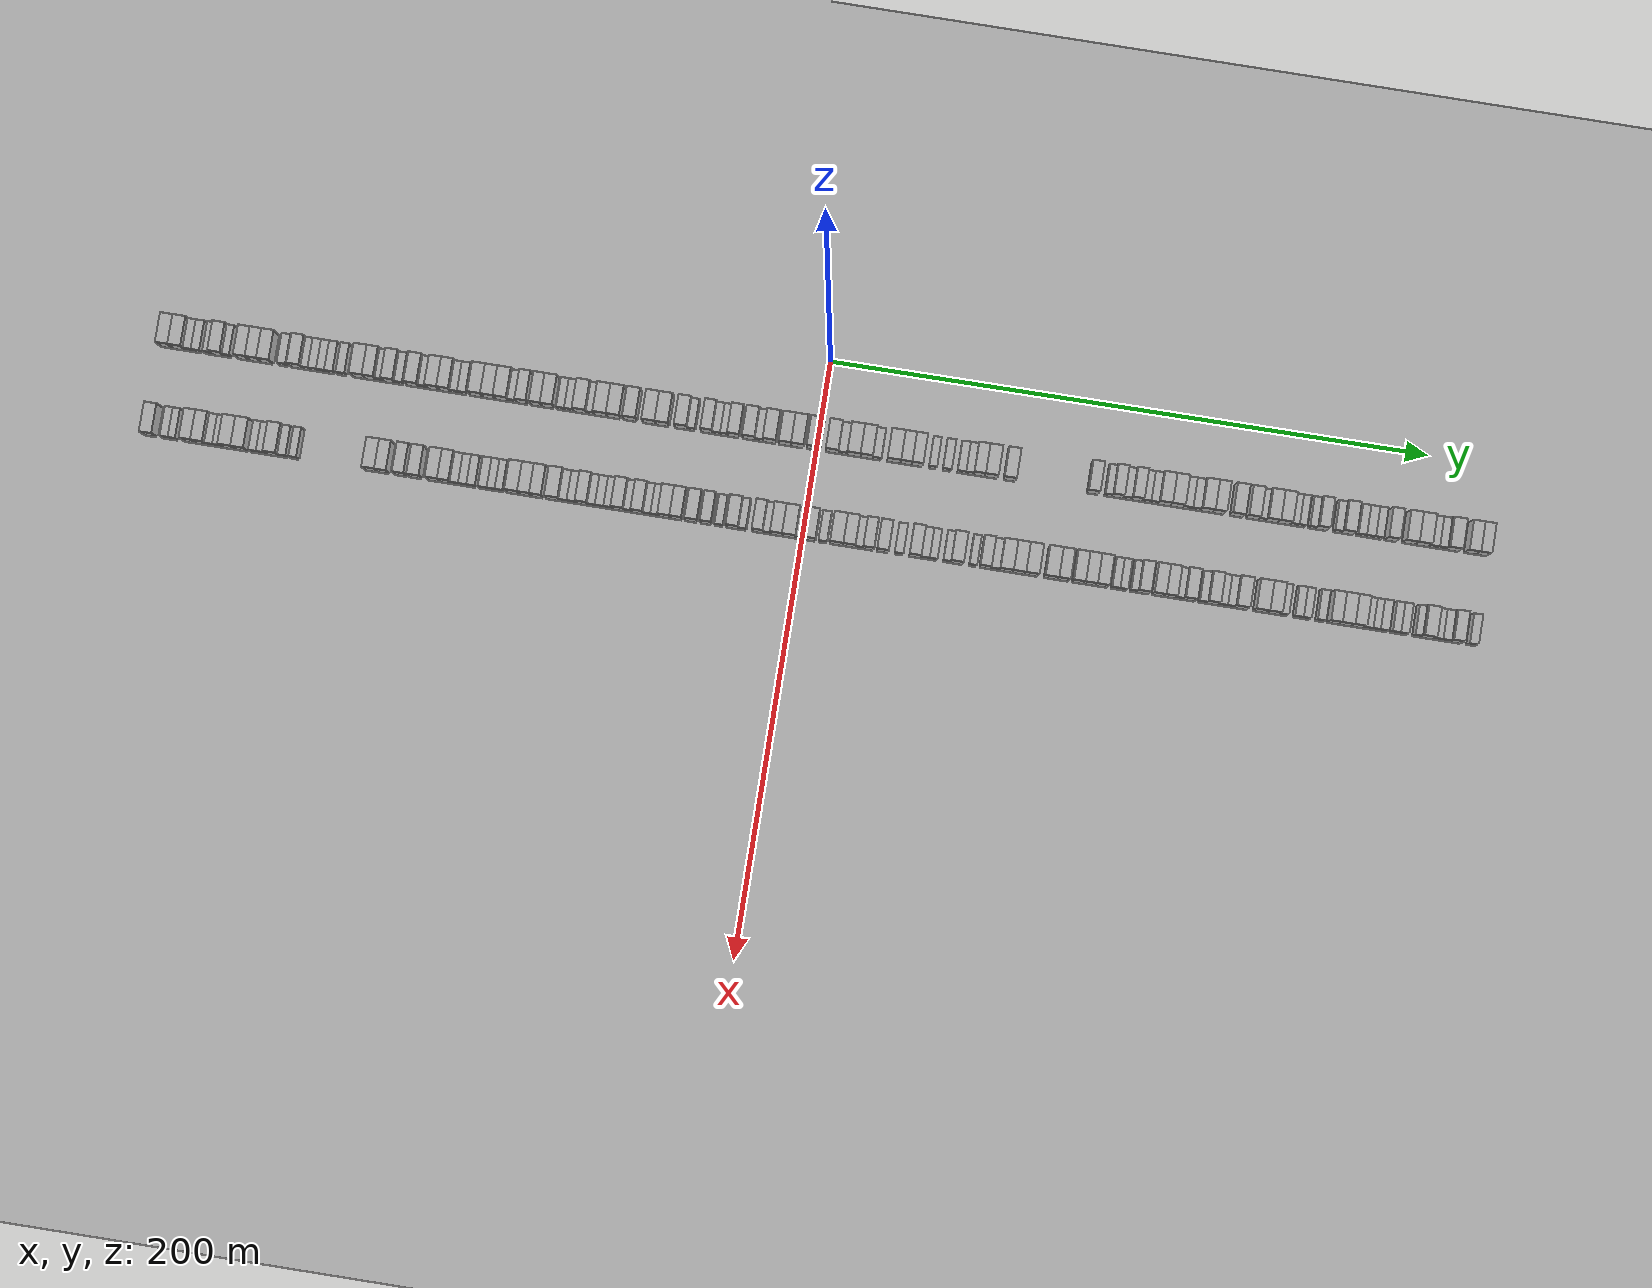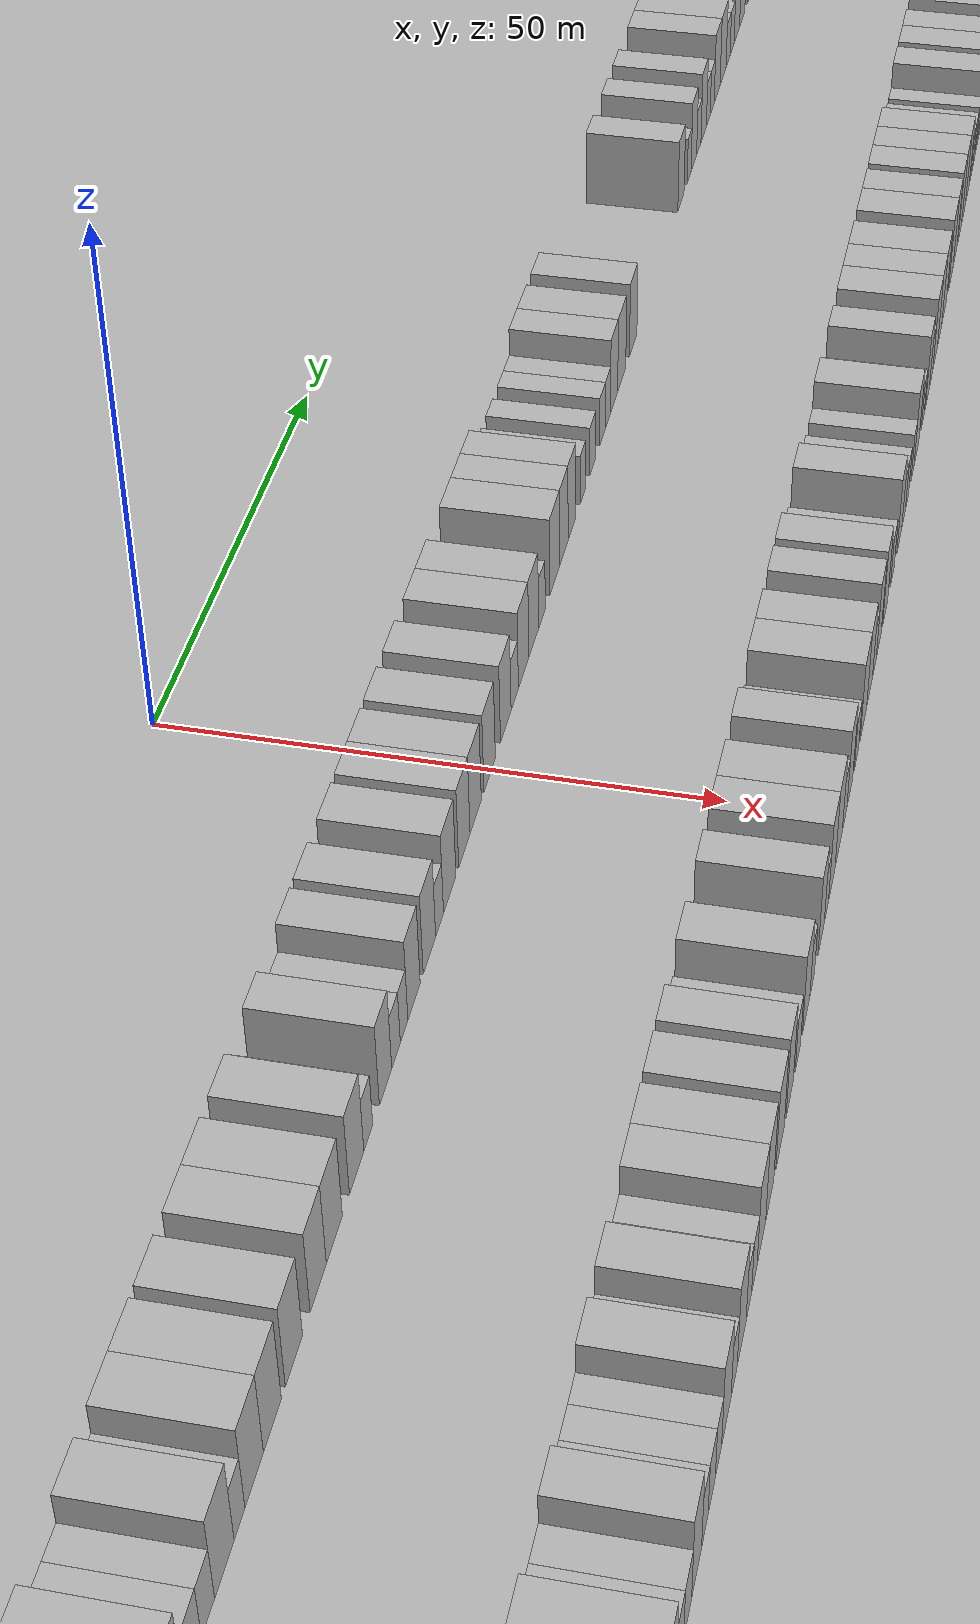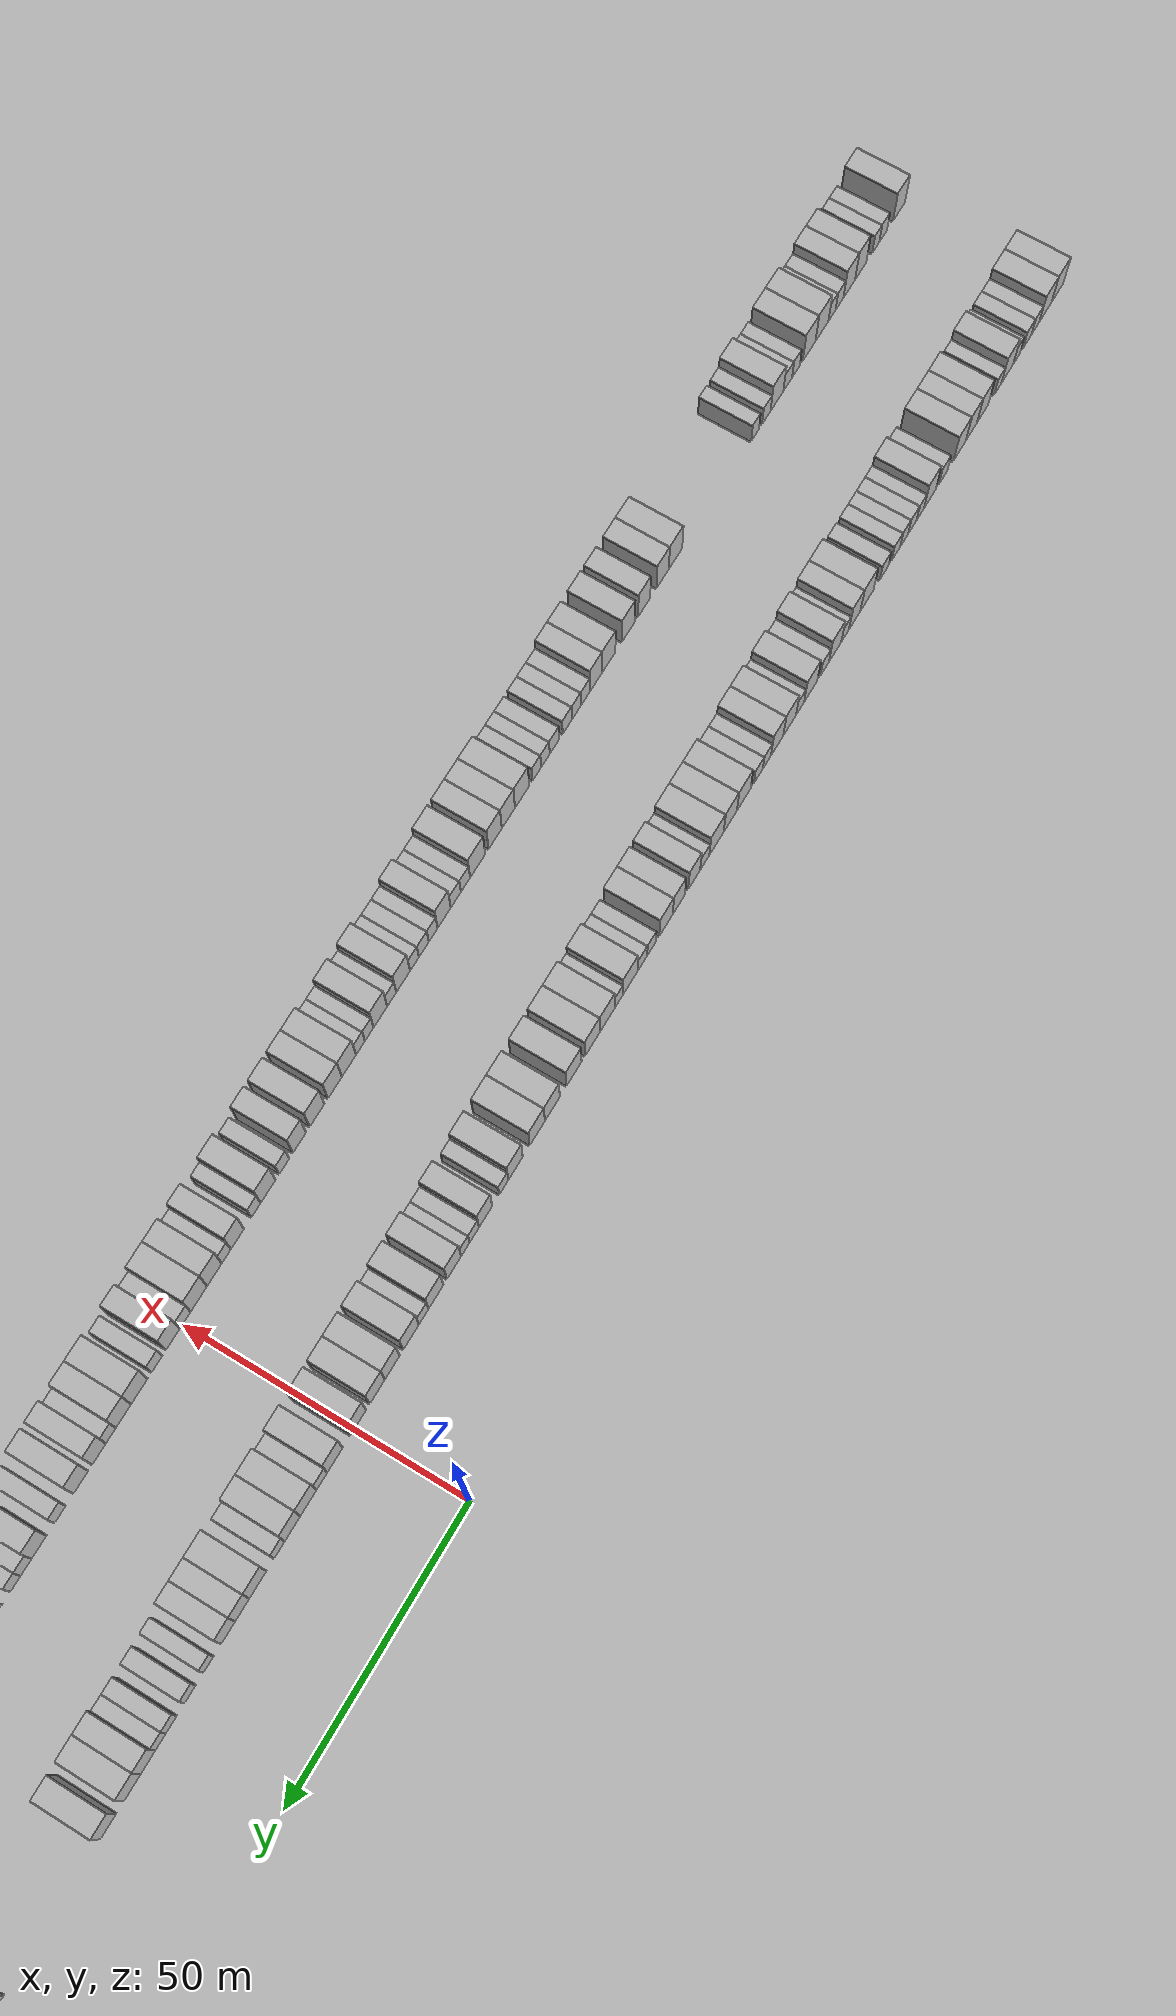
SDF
<?xml version="1.0" encoding="utf-8"?>

<sdf version="1.6">

   <world name="default">

      <gui fullscreen="0">

         <camera name="user_camera">

            <pose>-15 0 4.57585 0 0 0</pose>

            <view_controller>orbit</view_controller>

         </camera>

      </gui>

      <scene>

         <sky>

           <clouds>

             <speed>12</speed>

           </clouds>

         </sky>

         <ambient>0.4 0.4 0.4 1</ambient>

         <background>0.7 0.7 0.7 1</background>

         <shadows>1</shadows>

      </scene>

      <gravity>0 0 -9.8066</gravity>

      <magnetic_field>6e-06 2.3e-05 -4.2e-05</magnetic_field>

      <physics default="0" name="default_physics" type="ode">

         <ode>

            <solver>

               <type>quick</type>

               <iters>10</iters>

               <sor>1.0</sor>

               <use_dynamic_moi_rescaling>0</use_dynamic_moi_rescaling>

            </solver>

            <constraints>

               <cfm>0</cfm>

               <erp>0.2</erp>

               <contact_max_correcting_vel>100</contact_max_correcting_vel>

               <contact_surface_layer>0.001</contact_surface_layer>

            </constraints>

         </ode>

         <max_step_size>0.004</max_step_size>

         <real_time_factor>1</real_time_factor>

         <real_time_update_rate>250</real_time_update_rate>

      </physics>

      <light name="sun" type="directional">

         <cast_shadows>1</cast_shadows>

         <pose>0 0 10 0 0 0</pose>

         <diffuse>0.8 0.8 0.8 1</diffuse>

         <specular>0.2 0.2 0.2 1</specular>

         <attenuation>

            <range>1000</range>

            <constant>0.9</constant>

            <linear>0.01</linear>

            <quadratic>0.001</quadratic>

         </attenuation>

         <direction>-0.5 0.1 -0.9</direction>

      </light>

      <include>

         <name>ground_plane_1</name>

         <uri>model://HANNAS_ground_plane</uri>

         <pose>0 0 0  0 0 0</pose>

      </include>

      <include>

         <name>ground_plane_2</name>

         <uri>model://HANNAS_ground_plane</uri>

         <pose>100 0 0  0 0 0</pose>

      </include>

      <model name="building_1">

         <static>1</static>

         <pose frame="">25.0000 -217.9361 0 0.000000 0.000000 0.000000</pose>

         <link name="link">

            <pose frame="">0 0 4.50 0 0 0</pose>

            <collision name="collision">

               <geometry>

                  <box>

                     <size>10.0000 4.1279 9.0000</size>

                  </box>

               </geometry>

               <max_contacts>10</max_contacts>

               <surface>

                  <contact>

                     <ode/>

                  </contact>

                  <bounce/>

                  <friction>

                     <torsional>

                        <ode/>

                     </torsional>

                     <ode/>

                  </friction>

               </surface>

            </collision>

            <visual name="visual">

               <cast_shadows>0</cast_shadows>

               <geometry>

                  <box>

                     <size>10.0000 4.1279 9.0000</size>

                  </box>

               </geometry>

               <material>

                  <script>

                     <uri>model://HANNAS_wall/materials/scripts</uri>

                     <uri>model://HANNAS_wall/materials/textures</uri>

                     <name>vrc/HANNAS_wall</name>

                  </script>

               </material>

            </visual>

            <self_collide>0</self_collide>

            <enable_wind>0</enable_wind>

            <kinematic>0</kinematic>

         </link>

      </model>

      <model name="building_2">

         <static>1</static>

         <pose frame="">25.0000 -213.7134 0 0.000000 0.000000 0.000000</pose>

         <link name="link">

            <pose frame="">0 0 4.50 0 0 0</pose>

            <collision name="collision">

               <geometry>

                  <box>

                     <size>10.0000 4.3174 9.0000</size>

                  </box>

               </geometry>

               <max_contacts>10</max_contacts>

               <surface>

                  <contact>

                     <ode/>

                  </contact>

                  <bounce/>

                  <friction>

                     <torsional>

                        <ode/>

                     </torsional>

                     <ode/>

                  </friction>

               </surface>

            </collision>

            <visual name="visual">

               <cast_shadows>0</cast_shadows>

               <geometry>

                  <box>

                     <size>10.0000 4.3174 9.0000</size>

                  </box>

               </geometry>

               <material>

                  <script>

                     <uri>model://HANNAS_wall/materials/scripts</uri>

                     <uri>model://HANNAS_wall/materials/textures</uri>

                     <name>vrc/HANNAS_wall</name>

                  </script>

               </material>

            </visual>

            <self_collide>0</self_collide>

            <enable_wind>0</enable_wind>

            <kinematic>0</kinematic>

         </link>

      </model>

      <model name="building_3">

         <static>1</static>

         <pose frame="">25.0000 -210.1989 0 0.000000 0.000000 0.000000</pose>

         <link name="link">

            <pose frame="">0 0 3.00 0 0 0</pose>

            <collision name="collision">

               <geometry>

                  <box>

                     <size>10.0000 2.7117 6.0000</size>

                  </box>

               </geometry>

               <max_contacts>10</max_contacts>

               <surface>

                  <contact>

                     <ode/>

                  </contact>

                  <bounce/>

                  <friction>

                     <torsional>

                        <ode/>

                     </torsional>

                     <ode/>

                  </friction>

               </surface>

            </collision>

            <visual name="visual">

               <cast_shadows>0</cast_shadows>

               <geometry>

                  <box>

                     <size>10.0000 2.7117 6.0000</size>

                  </box>

               </geometry>

               <material>

                  <script>

                     <uri>model://HANNAS_wall/materials/scripts</uri>

                     <uri>model://HANNAS_wall/materials/textures</uri>

                     <name>vrc/HANNAS_wall</name>

                  </script>

               </material>

            </visual>

            <self_collide>0</self_collide>

            <enable_wind>0</enable_wind>

            <kinematic>0</kinematic>

         </link>

      </model>

      <model name="building_4">

         <static>1</static>

         <pose frame="">25.0000 -207.4145 0 0.000000 0.000000 0.000000</pose>

         <link name="link">

            <pose frame="">0 0 3.00 0 0 0</pose>

            <collision name="collision">

               <geometry>

                  <box>

                     <size>10.0000 2.8571 6.0000</size>

                  </box>

               </geometry>

               <max_contacts>10</max_contacts>

               <surface>

                  <contact>

                     <ode/>

                  </contact>

                  <bounce/>

                  <friction>

                     <torsional>

                        <ode/>

                     </torsional>

                     <ode/>

                  </friction>

               </surface>

            </collision>

            <visual name="visual">

               <cast_shadows>0</cast_shadows>

               <geometry>

                  <box>

                     <size>10.0000 2.8571 6.0000</size>

                  </box>

               </geometry>

               <material>

                  <script>

                     <uri>model://HANNAS_wall/materials/scripts</uri>

                     <uri>model://HANNAS_wall/materials/textures</uri>

                     <name>vrc/HANNAS_wall</name>

                  </script>

               </material>

            </visual>

            <self_collide>0</self_collide>

            <enable_wind>0</enable_wind>

            <kinematic>0</kinematic>

         </link>

      </model>

      <model name="building_5">

         <static>1</static>

         <pose frame="">25.0000 -203.7830 0 0.000000 0.000000 0.000000</pose>

         <link name="link">

            <pose frame="">0 0 3.00 0 0 0</pose>

            <collision name="collision">

               <geometry>

                  <box>

                     <size>10.0000 2.4057 6.0000</size>

                  </box>

               </geometry>

               <max_contacts>10</max_contacts>

               <surface>

                  <contact>

                     <ode/>

                  </contact>

                  <bounce/>

                  <friction>

                     <torsional>

                        <ode/>

                     </torsional>

                     <ode/>

                  </friction>

               </surface>

            </collision>

            <visual name="visual">

               <cast_shadows>0</cast_shadows>

               <geometry>

                  <box>

                     <size>10.0000 2.4057 6.0000</size>

                  </box>

               </geometry>

               <material>

                  <script>

                     <uri>model://HANNAS_wall/materials/scripts</uri>

                     <uri>model://HANNAS_wall/materials/textures</uri>

                     <name>vrc/HANNAS_wall</name>

                  </script>

               </material>

            </visual>

            <self_collide>0</self_collide>

            <enable_wind>0</enable_wind>

            <kinematic>0</kinematic>

         </link>

      </model>

      <model name="building_6">

         <static>1</static>

         <pose frame="">25.0000 -200.5248 0 0.000000 0.000000 0.000000</pose>

         <link name="link">

            <pose frame="">0 0 4.50 0 0 0</pose>

            <collision name="collision">

               <geometry>

                  <box>

                     <size>10.0000 4.1108 9.0000</size>

                  </box>

               </geometry>

               <max_contacts>10</max_contacts>

               <surface>

                  <contact>

                     <ode/>

                  </contact>

                  <bounce/>

                  <friction>

                     <torsional>

                        <ode/>

                     </torsional>

                     <ode/>

                  </friction>

               </surface>

            </collision>

            <visual name="visual">

               <cast_shadows>0</cast_shadows>

               <geometry>

                  <box>

                     <size>10.0000 4.1108 9.0000</size>

                  </box>

               </geometry>

               <material>

                  <script>

                     <uri>model://HANNAS_wall/materials/scripts</uri>

                     <uri>model://HANNAS_wall/materials/textures</uri>

                     <name>vrc/HANNAS_wall</name>

                  </script>

               </material>

            </visual>

            <self_collide>0</self_collide>

            <enable_wind>0</enable_wind>

            <kinematic>0</kinematic>

         </link>

      </model>

      <model name="building_7">

         <static>1</static>

         <pose frame="">25.0000 -197.2412 0 0.000000 0.000000 0.000000</pose>

         <link name="link">

            <pose frame="">0 0 3.00 0 0 0</pose>

            <collision name="collision">

               <geometry>

                  <box>

                     <size>10.0000 2.4563 6.0000</size>

                  </box>

               </geometry>

               <max_contacts>10</max_contacts>

               <surface>

                  <contact>

                     <ode/>

                  </contact>

                  <bounce/>

                  <friction>

                     <torsional>

                        <ode/>

                     </torsional>

                     <ode/>

                  </friction>

               </surface>

            </collision>

            <visual name="visual">

               <cast_shadows>0</cast_shadows>

               <geometry>

                  <box>

                     <size>10.0000 2.4563 6.0000</size>

                  </box>

               </geometry>

               <material>

                  <script>

                     <uri>model://HANNAS_wall/materials/scripts</uri>

                     <uri>model://HANNAS_wall/materials/textures</uri>

                     <name>vrc/HANNAS_wall</name>

                  </script>

               </material>

            </visual>

            <self_collide>0</self_collide>

            <enable_wind>0</enable_wind>

            <kinematic>0</kinematic>

         </link>

      </model>

      <model name="building_8">

         <static>1</static>

         <pose frame="">25.0000 -192.0605 0 0.000000 0.000000 0.000000</pose>

         <link name="link">

            <pose frame="">0 0 4.50 0 0 0</pose>

            <collision name="collision">

               <geometry>

                  <box>

                     <size>10.0000 3.9051 9.0000</size>

                  </box>

               </geometry>

               <max_contacts>10</max_contacts>

               <surface>

                  <contact>

                     <ode/>

                  </contact>

                  <bounce/>

                  <friction>

                     <torsional>

                        <ode/>

                     </torsional>

                     <ode/>

                  </friction>

               </surface>

            </collision>

            <visual name="visual">

               <cast_shadows>0</cast_shadows>

               <geometry>

                  <box>

                     <size>10.0000 3.9051 9.0000</size>

                  </box>

               </geometry>

               <material>

                  <script>

                     <uri>model://HANNAS_wall/materials/scripts</uri>

                     <uri>model://HANNAS_wall/materials/textures</uri>

                     <name>vrc/HANNAS_wall</name>

                  </script>

               </material>

            </visual>

            <self_collide>0</self_collide>

            <enable_wind>0</enable_wind>

            <kinematic>0</kinematic>

         </link>

      </model>

      <model name="building_9">

         <static>1</static>

         <pose frame="">25.0000 -188.2016 0 0.000000 0.000000 0.000000</pose>

         <link name="link">

            <pose frame="">0 0 4.50 0 0 0</pose>

            <collision name="collision">

               <geometry>

                  <box>

                     <size>10.0000 3.8128 9.0000</size>

                  </box>

               </geometry>

               <max_contacts>10</max_contacts>

               <surface>

                  <contact>

                     <ode/>

                  </contact>

                  <bounce/>

                  <friction>

                     <torsional>

                        <ode/>

                     </torsional>

                     <ode/>

                  </friction>

               </surface>

            </collision>

            <visual name="visual">

               <cast_shadows>0</cast_shadows>

               <geometry>

                  <box>

                     <size>10.0000 3.8128 9.0000</size>

                  </box>

               </geometry>

               <material>

                  <script>

                     <uri>model://HANNAS_wall/materials/scripts</uri>

                     <uri>model://HANNAS_wall/materials/textures</uri>

                     <name>vrc/HANNAS_wall</name>

                  </script>

               </material>

            </visual>

            <self_collide>0</self_collide>

            <enable_wind>0</enable_wind>

            <kinematic>0</kinematic>

         </link>

      </model>

      <model name="building_10">

         <static>1</static>

         <pose frame="">25.0000 -184.2133 0 0.000000 0.000000 0.000000</pose>

         <link name="link">

            <pose frame="">0 0 4.50 0 0 0</pose>

            <collision name="collision">

               <geometry>

                  <box>

                     <size>10.0000 4.1638 9.0000</size>

                  </box>

               </geometry>

               <max_contacts>10</max_contacts>

               <surface>

                  <contact>

                     <ode/>

                  </contact>

                  <bounce/>

                  <friction>

                     <torsional>

                        <ode/>

                     </torsional>

                     <ode/>

                  </friction>

               </surface>

            </collision>

            <visual name="visual">

               <cast_shadows>0</cast_shadows>

               <geometry>

                  <box>

                     <size>10.0000 4.1638 9.0000</size>

                  </box>

               </geometry>

               <material>

                  <script>

                     <uri>model://HANNAS_wall/materials/scripts</uri>

                     <uri>model://HANNAS_wall/materials/textures</uri>

                     <name>vrc/HANNAS_wall</name>

                  </script>

               </material>

            </visual>

            <self_collide>0</self_collide>

            <enable_wind>0</enable_wind>

            <kinematic>0</kinematic>

         </link>

      </model>

      <model name="building_11">

         <static>1</static>

         <pose frame="">25.0000 -178.6746 0 0.000000 0.000000 0.000000</pose>

         <link name="link">

            <pose frame="">0 0 3.00 0 0 0</pose>

            <collision name="collision">

               <geometry>

                  <box>

                     <size>10.0000 2.9137 6.0000</size>

                  </box>

               </geometry>

               <max_contacts>10</max_contacts>

               <surface>

                  <contact>

                     <ode/>

                  </contact>

                  <bounce/>

                  <friction>

                     <torsional>

                        <ode/>

                     </torsional>

                     <ode/>

                  </friction>

               </surface>

            </collision>

            <visual name="visual">

               <cast_shadows>0</cast_shadows>

               <geometry>

                  <box>

                     <size>10.0000 2.9137 6.0000</size>

                  </box>

               </geometry>

               <material>

                  <script>

                     <uri>model://HANNAS_wall/materials/scripts</uri>

                     <uri>model://HANNAS_wall/materials/textures</uri>

                     <name>vrc/HANNAS_wall</name>

                  </script>

               </material>

            </visual>

            <self_collide>0</self_collide>

            <enable_wind>0</enable_wind>

            <kinematic>0</kinematic>

         </link>

      </model>

      <model name="building_12">

         <static>1</static>

         <pose frame="">25.0000 -174.1912 0 0.000000 0.000000 0.000000</pose>

         <link name="link">

            <pose frame="">0 0 4.50 0 0 0</pose>

            <collision name="collision">

               <geometry>

                  <box>

                     <size>10.0000 4.0531 9.0000</size>

                  </box>

               </geometry>

               <max_contacts>10</max_contacts>

               <surface>

                  <contact>

                     <ode/>

                  </contact>

                  <bounce/>

                  <friction>

                     <torsional>

                        <ode/>

                     </torsional>

                     <ode/>

                  </friction>

               </surface>

            </collision>

            <visual name="visual">

               <cast_shadows>0</cast_shadows>

               <geometry>

                  <box>

                     <size>10.0000 4.0531 9.0000</size>

                  </box>

               </geometry>

               <material>

                  <script>

                     <uri>model://HANNAS_wall/materials/scripts</uri>

                     <uri>model://HANNAS_wall/materials/textures</uri>

                     <name>vrc/HANNAS_wall</name>

                  </script>

               </material>

            </visual>

            <self_collide>0</self_collide>

            <enable_wind>0</enable_wind>

            <kinematic>0</kinematic>

         </link>

      </model>

      <model name="building_13">

         <static>1</static>

         <pose frame="">25.0000 -170.9646 0 0.000000 0.000000 0.000000</pose>

         <link name="link">

            <pose frame="">0 0 3.00 0 0 0</pose>

            <collision name="collision">

               <geometry>

                  <box>

                     <size>10.0000 2.4002 6.0000</size>

                  </box>

               </geometry>

               <max_contacts>10</max_contacts>

               <surface>

                  <contact>

                     <ode/>

                  </contact>

                  <bounce/>

                  <friction>

                     <torsional>

                        <ode/>

                     </torsional>

                     <ode/>

                  </friction>

               </surface>

            </collision>

            <visual name="visual">

               <cast_shadows>0</cast_shadows>

               <geometry>

                  <box>

                     <size>10.0000 2.4002 6.0000</size>

                  </box>

               </geometry>

               <material>

                  <script>

                     <uri>model://HANNAS_wall/materials/scripts</uri>

                     <uri>model://HANNAS_wall/materials/textures</uri>

                     <name>vrc/HANNAS_wall</name>

                  </script>

               </material>

            </visual>

            <self_collide>0</self_collide>

            <enable_wind>0</enable_wind>

            <kinematic>0</kinematic>

         </link>

      </model>

      <model name="building_14">

         <static>1</static>

         <pose frame="">25.0000 -168.3456 0 0.000000 0.000000 0.000000</pose>

         <link name="link">

            <pose frame="">0 0 3.00 0 0 0</pose>

            <collision name="collision">

               <geometry>

                  <box>

                     <size>10.0000 2.8377 6.0000</size>

                  </box>

               </geometry>

               <max_contacts>10</max_contacts>

               <surface>

                  <contact>

                     <ode/>

                  </contact>

                  <bounce/>

                  <friction>

                     <torsional>

                        <ode/>

                     </torsional>

                     <ode/>

                  </friction>

               </surface>

            </collision>

            <visual name="visual">

               <cast_shadows>0</cast_shadows>

               <geometry>

                  <box>

                     <size>10.0000 2.8377 6.0000</size>

                  </box>

               </geometry>

               <material>

                  <script>

                     <uri>model://HANNAS_wall/materials/scripts</uri>

                     <uri>model://HANNAS_wall/materials/textures</uri>

                     <name>vrc/HANNAS_wall</name>

                  </script>

               </material>

            </visual>

            <self_collide>0</self_collide>

            <enable_wind>0</enable_wind>

            <kinematic>0</kinematic>

         </link>

      </model>

      <model name="building_15">

         <static>1</static>

         <pose frame="">25.0000 -165.5896 0 0.000000 0.000000 0.000000</pose>

         <link name="link">

            <pose frame="">0 0 3.00 0 0 0</pose>

            <collision name="collision">

               <geometry>

                  <box>

                     <size>10.0000 2.6744 6.0000</size>

                  </box>

               </geometry>

               <max_contacts>10</max_contacts>

               <surface>

                  <contact>

                     <ode/>

                  </contact>

                  <bounce/>

                  <friction>

                     <torsional>

                        <ode/>

                     </torsional>

                     <ode/>

                  </friction>

               </surface>

            </collision>

            <visual name="visual">

               <cast_shadows>0</cast_shadows>

               <geometry>

                  <box>

                     <size>10.0000 2.6744 6.0000</size>

                  </box>

               </geometry>

               <material>

                  <script>

                     <uri>model://HANNAS_wall/materials/scripts</uri>

                     <uri>model://HANNAS_wall/materials/textures</uri>

                     <name>vrc/HANNAS_wall</name>

                  </script>

               </material>

            </visual>

            <self_collide>0</self_collide>

            <enable_wind>0</enable_wind>

            <kinematic>0</kinematic>

         </link>

      </model>

      <model name="building_16">

         <static>1</static>

         <pose frame="">25.0000 -162.8514 0 0.000000 0.000000 0.000000</pose>

         <link name="link">

            <pose frame="">0 0 3.00 0 0 0</pose>

            <collision name="collision">

               <geometry>

                  <box>

                     <size>10.0000 2.8020 6.0000</size>

                  </box>

               </geometry>

               <max_contacts>10</max_contacts>

               <surface>

                  <contact>

                     <ode/>

                  </contact>

                  <bounce/>

                  <friction>

                     <torsional>

                        <ode/>

                     </torsional>

                     <ode/>

                  </friction>

               </surface>

            </collision>

            <visual name="visual">

               <cast_shadows>0</cast_shadows>

               <geometry>

                  <box>

                     <size>10.0000 2.8020 6.0000</size>

                  </box>

               </geometry>

               <material>

                  <script>

                     <uri>model://HANNAS_wall/materials/scripts</uri>

                     <uri>model://HANNAS_wall/materials/textures</uri>

                     <name>vrc/HANNAS_wall</name>

                  </script>

               </material>

            </visual>

            <self_collide>0</self_collide>

            <enable_wind>0</enable_wind>

            <kinematic>0</kinematic>

         </link>

      </model>

      <model name="building_17">

         <static>1</static>

         <pose frame="">25.0000 -158.9862 0 0.000000 0.000000 0.000000</pose>

         <link name="link">

            <pose frame="">0 0 3.00 0 0 0</pose>

            <collision name="collision">

               <geometry>

                  <box>

                     <size>10.0000 2.9284 6.0000</size>

                  </box>

               </geometry>

               <max_contacts>10</max_contacts>

               <surface>

                  <contact>

                     <ode/>

                  </contact>

                  <bounce/>

                  <friction>

                     <torsional>

                        <ode/>

                     </torsional>

                     <ode/>

                  </friction>

               </surface>

            </collision>

            <visual name="visual">

               <cast_shadows>0</cast_shadows>

               <geometry>

                  <box>

                     <size>10.0000 2.9284 6.0000</size>

                  </box>

               </geometry>

               <material>

                  <script>

                     <uri>model://HANNAS_wall/materials/scripts</uri>

                     <uri>model://HANNAS_wall/materials/textures</uri>

                     <name>vrc/HANNAS_wall</name>

                  </script>

               </material>

            </visual>

            <self_collide>0</self_collide>

            <enable_wind>0</enable_wind>

            <kinematic>0</kinematic>

         </link>

      </model>

      <model name="building_18">

         <static>1</static>

         <pose frame="">25.0000 -153.3466 0 0.000000 0.000000 0.000000</pose>

         <link name="link">

            <pose frame="">0 0 4.50 0 0 0</pose>

            <collision name="collision">

               <geometry>

                  <box>

                     <size>10.0000 4.3508 9.0000</size>

                  </box>

               </geometry>

               <max_contacts>10</max_contacts>

               <surface>

                  <contact>

                     <ode/>

                  </contact>

                  <bounce/>

                  <friction>

                     <torsional>

                        <ode/>

                     </torsional>

                     <ode/>

                  </friction>

               </surface>

            </collision>

            <visual name="visual">

               <cast_shadows>0</cast_shadows>

               <geometry>

                  <box>

                     <size>10.0000 4.3508 9.0000</size>

                  </box>

               </geometry>

               <material>

                  <script>

                     <uri>model://HANNAS_wall/materials/scripts</uri>

                     <uri>model://HANNAS_wall/materials/textures</uri>

                     <name>vrc/HANNAS_wall</name>

                  </script>

               </material>

            </visual>

            <self_collide>0</self_collide>

            <enable_wind>0</enable_wind>

            <kinematic>0</kinematic>

         </link>

      </model>

      <model name="building_19">

         <static>1</static>

         <pose frame="">25.0000 -149.2983 0 0.000000 0.000000 0.000000</pose>

         <link name="link">

            <pose frame="">0 0 4.50 0 0 0</pose>

            <collision name="collision">

               <geometry>

                  <box>

                     <size>10.0000 3.7458 9.0000</size>

                  </box>

               </geometry>

               <max_contacts>10</max_contacts>

               <surface>

                  <contact>

                     <ode/>

                  </contact>

                  <bounce/>

                  <friction>

                     <torsional>

                        <ode/>

                     </torsional>

                     <ode/>

                  </friction>

               </surface>

            </collision>

            <visual name="visual">

               <cast_shadows>0</cast_shadows>

               <geometry>

                  <box>

                     <size>10.0000 3.7458 9.0000</size>

                  </box>

               </geometry>

               <material>

                  <script>

                     <uri>model://HANNAS_wall/materials/scripts</uri>

                     <uri>model://HANNAS_wall/materials/textures</uri>

                     <name>vrc/HANNAS_wall</name>

                  </script>

               </material>

            </visual>

            <self_collide>0</self_collide>

            <enable_wind>0</enable_wind>

            <kinematic>0</kinematic>

         </link>

      </model>

      <model name="building_20">

         <static>1</static>

         <pose frame="">25.0000 -146.2084 0 0.000000 0.000000 0.000000</pose>

         <link name="link">

            <pose frame="">0 0 3.00 0 0 0</pose>

            <collision name="collision">

               <geometry>

                  <box>

                     <size>10.0000 2.4340 6.0000</size>

                  </box>

               </geometry>

               <max_contacts>10</max_contacts>

               <surface>

                  <contact>

                     <ode/>

                  </contact>

                  <bounce/>

                  <friction>

                     <torsional>

                        <ode/>

                     </torsional>

                     <ode/>

                  </friction>

               </surface>

            </collision>

            <visual name="visual">

               <cast_shadows>0</cast_shadows>

               <geometry>

                  <box>

                     <size>10.0000 2.4340 6.0000</size>

                  </box>

               </geometry>

               <material>

                  <script>

                     <uri>model://HANNAS_wall/materials/scripts</uri>

                     <uri>model://HANNAS_wall/materials/textures</uri>

                     <name>vrc/HANNAS_wall</name>

                  </script>

               </material>

            </visual>

            <self_collide>0</self_collide>

            <enable_wind>0</enable_wind>

            <kinematic>0</kinematic>

         </link>

      </model>

      <model name="building_21">

         <static>1</static>

         <pose frame="">25.0000 -142.9837 0 0.000000 0.000000 0.000000</pose>

         <link name="link">

            <pose frame="">0 0 4.50 0 0 0</pose>

            <collision name="collision">

               <geometry>

                  <box>

                     <size>10.0000 4.0155 9.0000</size>

                  </box>

               </geometry>

               <max_contacts>10</max_contacts>

               <surface>

                  <contact>

                     <ode/>

                  </contact>

                  <bounce/>

                  <friction>

                     <torsional>

                        <ode/>

                     </torsional>

                     <ode/>

                  </friction>

               </surface>

            </collision>

            <visual name="visual">

               <cast_shadows>0</cast_shadows>

               <geometry>

                  <box>

                     <size>10.0000 4.0155 9.0000</size>

                  </box>

               </geometry>

               <material>

                  <script>

                     <uri>model://HANNAS_wall/materials/scripts</uri>

                     <uri>model://HANNAS_wall/materials/textures</uri>

                     <name>vrc/HANNAS_wall</name>

                  </script>

               </material>

            </visual>

            <self_collide>0</self_collide>

            <enable_wind>0</enable_wind>

            <kinematic>0</kinematic>

         </link>

      </model>

      <model name="building_22">

         <static>1</static>

         <pose frame="">25.0000 -139.6213 0 0.000000 0.000000 0.000000</pose>

         <link name="link">

            <pose frame="">0 0 3.00 0 0 0</pose>

            <collision name="collision">

               <geometry>

                  <box>

                     <size>10.0000 2.7093 6.0000</size>

                  </box>

               </geometry>

               <max_contacts>10</max_contacts>

               <surface>

                  <contact>

                     <ode/>

                  </contact>

                  <bounce/>

                  <friction>

                     <torsional>

                        <ode/>

                     </torsional>

                     <ode/>

                  </friction>

               </surface>

            </collision>

            <visual name="visual">

               <cast_shadows>0</cast_shadows>

               <geometry>

                  <box>

                     <size>10.0000 2.7093 6.0000</size>

                  </box>

               </geometry>

               <material>

                  <script>

                     <uri>model://HANNAS_wall/materials/scripts</uri>

                     <uri>model://HANNAS_wall/materials/textures</uri>

                     <name>vrc/HANNAS_wall</name>

                  </script>

               </material>

            </visual>

            <self_collide>0</self_collide>

            <enable_wind>0</enable_wind>

            <kinematic>0</kinematic>

         </link>

      </model>

      <model name="building_23">

         <static>1</static>

         <pose frame="">25.0000 -135.1451 0 0.000000 0.000000 0.000000</pose>

         <link name="link">

            <pose frame="">0 0 4.50 0 0 0</pose>

            <collision name="collision">

               <geometry>

                  <box>

                     <size>10.0000 4.2429 9.0000</size>

                  </box>

               </geometry>

               <max_contacts>10</max_contacts>

               <surface>

                  <contact>

                     <ode/>

                  </contact>

                  <bounce/>

                  <friction>

                     <torsional>

                        <ode/>

                     </torsional>

                     <ode/>

                  </friction>

               </surface>

            </collision>

            <visual name="visual">

               <cast_shadows>0</cast_shadows>

               <geometry>

                  <box>

                     <size>10.0000 4.2429 9.0000</size>

                  </box>

               </geometry>

               <material>

                  <script>

                     <uri>model://HANNAS_wall/materials/scripts</uri>

                     <uri>model://HANNAS_wall/materials/textures</uri>

                     <name>vrc/HANNAS_wall</name>

                  </script>

               </material>

            </visual>

            <self_collide>0</self_collide>

            <enable_wind>0</enable_wind>

            <kinematic>0</kinematic>

         </link>

      </model>

      <model name="building_24">

         <static>1</static>

         <pose frame="">25.0000 -131.7192 0 0.000000 0.000000 0.000000</pose>

         <link name="link">

            <pose frame="">0 0 3.00 0 0 0</pose>

            <collision name="collision">

               <geometry>

                  <box>

                     <size>10.0000 2.6089 6.0000</size>

                  </box>

               </geometry>

               <max_contacts>10</max_contacts>

               <surface>

                  <contact>

                     <ode/>

                  </contact>

                  <bounce/>

                  <friction>

                     <torsional>

                        <ode/>

                     </torsional>

                     <ode/>

                  </friction>

               </surface>

            </collision>

            <visual name="visual">

               <cast_shadows>0</cast_shadows>

               <geometry>

                  <box>

                     <size>10.0000 2.6089 6.0000</size>

                  </box>

               </geometry>

               <material>

                  <script>

                     <uri>model://HANNAS_wall/materials/scripts</uri>

                     <uri>model://HANNAS_wall/materials/textures</uri>

                     <name>vrc/HANNAS_wall</name>

                  </script>

               </material>

            </visual>

            <self_collide>0</self_collide>

            <enable_wind>0</enable_wind>

            <kinematic>0</kinematic>

         </link>

      </model>

      <model name="building_25">

         <static>1</static>

         <pose frame="">25.0000 -128.3897 0 0.000000 0.000000 0.000000</pose>

         <link name="link">

            <pose frame="">0 0 4.50 0 0 0</pose>

            <collision name="collision">

               <geometry>

                  <box>

                     <size>10.0000 4.0501 9.0000</size>

                  </box>

               </geometry>

               <max_contacts>10</max_contacts>

               <surface>

                  <contact>

                     <ode/>

                  </contact>

                  <bounce/>

                  <friction>

                     <torsional>

                        <ode/>

                     </torsional>

                     <ode/>

                  </friction>

               </surface>

            </collision>

            <visual name="visual">

               <cast_shadows>0</cast_shadows>

               <geometry>

                  <box>

                     <size>10.0000 4.0501 9.0000</size>

                  </box>

               </geometry>

               <material>

                  <script>

                     <uri>model://HANNAS_wall/materials/scripts</uri>

                     <uri>model://HANNAS_wall/materials/textures</uri>

                     <name>vrc/HANNAS_wall</name>

                  </script>

               </material>

            </visual>

            <self_collide>0</self_collide>

            <enable_wind>0</enable_wind>

            <kinematic>0</kinematic>

         </link>

      </model>

      <model name="building_26">

         <static>1</static>

         <pose frame="">25.0000 -124.4075 0 0.000000 0.000000 0.000000</pose>

         <link name="link">

            <pose frame="">0 0 4.50 0 0 0</pose>

            <collision name="collision">

               <geometry>

                  <box>

                     <size>10.0000 3.9143 9.0000</size>

                  </box>

               </geometry>

               <max_contacts>10</max_contacts>

               <surface>

                  <contact>

                     <ode/>

                  </contact>

                  <bounce/>

                  <friction>

                     <torsional>

                        <ode/>

                     </torsional>

                     <ode/>

                  </friction>

               </surface>

            </collision>

            <visual name="visual">

               <cast_shadows>0</cast_shadows>

               <geometry>

                  <box>

                     <size>10.0000 3.9143 9.0000</size>

                  </box>

               </geometry>

               <material>

                  <script>

                     <uri>model://HANNAS_wall/materials/scripts</uri>

                     <uri>model://HANNAS_wall/materials/textures</uri>

                     <name>vrc/HANNAS_wall</name>

                  </script>

               </material>

            </visual>

            <self_collide>0</self_collide>

            <enable_wind>0</enable_wind>

            <kinematic>0</kinematic>

         </link>

      </model>

      <model name="building_27">

         <static>1</static>

         <pose frame="">25.0000 -121.1815 0 0.000000 0.000000 0.000000</pose>

         <link name="link">

            <pose frame="">0 0 3.00 0 0 0</pose>

            <collision name="collision">

               <geometry>

                  <box>

                     <size>10.0000 2.5376 6.0000</size>

                  </box>

               </geometry>

               <max_contacts>10</max_contacts>

               <surface>

                  <contact>

                     <ode/>

                  </contact>

                  <bounce/>

                  <friction>

                     <torsional>

                        <ode/>

                     </torsional>

                     <ode/>

                  </friction>

               </surface>

            </collision>

            <visual name="visual">

               <cast_shadows>0</cast_shadows>

               <geometry>

                  <box>

                     <size>10.0000 2.5376 6.0000</size>

                  </box>

               </geometry>

               <material>

                  <script>

                     <uri>model://HANNAS_wall/materials/scripts</uri>

                     <uri>model://HANNAS_wall/materials/textures</uri>

                     <name>vrc/HANNAS_wall</name>

                  </script>

               </material>

            </visual>

            <self_collide>0</self_collide>

            <enable_wind>0</enable_wind>

            <kinematic>0</kinematic>

         </link>

      </model>

      <model name="building_28">

         <static>1</static>

         <pose frame="">25.0000 -118.4979 0 0.000000 0.000000 0.000000</pose>

         <link name="link">

            <pose frame="">0 0 3.00 0 0 0</pose>

            <collision name="collision">

               <geometry>

                  <box>

                     <size>10.0000 2.8295 6.0000</size>

                  </box>

               </geometry>

               <max_contacts>10</max_contacts>

               <surface>

                  <contact>

                     <ode/>

                  </contact>

                  <bounce/>

                  <friction>

                     <torsional>

                        <ode/>

                     </torsional>

                     <ode/>

                  </friction>

               </surface>

            </collision>

            <visual name="visual">

               <cast_shadows>0</cast_shadows>

               <geometry>

                  <box>

                     <size>10.0000 2.8295 6.0000</size>

                  </box>

               </geometry>

               <material>

                  <script>

                     <uri>model://HANNAS_wall/materials/scripts</uri>

                     <uri>model://HANNAS_wall/materials/textures</uri>

                     <name>vrc/HANNAS_wall</name>

                  </script>

               </material>

            </visual>

            <self_collide>0</self_collide>

            <enable_wind>0</enable_wind>

            <kinematic>0</kinematic>

         </link>

      </model>

      <model name="building_29">

         <static>1</static>

         <pose frame="">25.0000 -113.9356 0 0.000000 0.000000 0.000000</pose>

         <link name="link">

            <pose frame="">0 0 4.50 0 0 0</pose>

            <collision name="collision">

               <geometry>

                  <box>

                     <size>10.0000 4.2951 9.0000</size>

                  </box>

               </geometry>

               <max_contacts>10</max_contacts>

               <surface>

                  <contact>

                     <ode/>

                  </contact>

                  <bounce/>

                  <friction>

                     <torsional>

                        <ode/>

                     </torsional>

                     <ode/>

                  </friction>

               </surface>

            </collision>

            <visual name="visual">

               <cast_shadows>0</cast_shadows>

               <geometry>

                  <box>

                     <size>10.0000 4.2951 9.0000</size>

                  </box>

               </geometry>

               <material>

                  <script>

                     <uri>model://HANNAS_wall/materials/scripts</uri>

                     <uri>model://HANNAS_wall/materials/textures</uri>

                     <name>vrc/HANNAS_wall</name>

                  </script>

               </material>

            </visual>

            <self_collide>0</self_collide>

            <enable_wind>0</enable_wind>

            <kinematic>0</kinematic>

         </link>

      </model>

      <model name="building_30">

         <static>1</static>

         <pose frame="">25.0000 -109.7201 0 0.000000 0.000000 0.000000</pose>

         <link name="link">

            <pose frame="">0 0 4.50 0 0 0</pose>

            <collision name="collision">

               <geometry>

                  <box>

                     <size>10.0000 4.1360 9.0000</size>

                  </box>

               </geometry>

               <max_contacts>10</max_contacts>

               <surface>

                  <contact>

                     <ode/>

                  </contact>

                  <bounce/>

                  <friction>

                     <torsional>

                        <ode/>

                     </torsional>

                     <ode/>

                  </friction>

               </surface>

            </collision>

            <visual name="visual">

               <cast_shadows>0</cast_shadows>

               <geometry>

                  <box>

                     <size>10.0000 4.1360 9.0000</size>

                  </box>

               </geometry>

               <material>

                  <script>

                     <uri>model://HANNAS_wall/materials/scripts</uri>

                     <uri>model://HANNAS_wall/materials/textures</uri>

                     <name>vrc/HANNAS_wall</name>

                  </script>

               </material>

            </visual>

            <self_collide>0</self_collide>

            <enable_wind>0</enable_wind>

            <kinematic>0</kinematic>

         </link>

      </model>

      <model name="building_31">

         <static>1</static>

         <pose frame="">25.0000 -105.4239 0 0.000000 0.000000 0.000000</pose>

         <link name="link">

            <pose frame="">0 0 4.50 0 0 0</pose>

            <collision name="collision">

               <geometry>

                  <box>

                     <size>10.0000 4.4564 9.0000</size>

                  </box>

               </geometry>

               <max_contacts>10</max_contacts>

               <surface>

                  <contact>

                     <ode/>

                  </contact>

                  <bounce/>

                  <friction>

                     <torsional>

                        <ode/>

                     </torsional>

                     <ode/>

                  </friction>

               </surface>

            </collision>

            <visual name="visual">

               <cast_shadows>0</cast_shadows>

               <geometry>

                  <box>

                     <size>10.0000 4.4564 9.0000</size>

                  </box>

               </geometry>

               <material>

                  <script>

                     <uri>model://HANNAS_wall/materials/scripts</uri>

                     <uri>model://HANNAS_wall/materials/textures</uri>

                     <name>vrc/HANNAS_wall</name>

                  </script>

               </material>

            </visual>

            <self_collide>0</self_collide>

            <enable_wind>0</enable_wind>

            <kinematic>0</kinematic>

         </link>

      </model>

      <model name="building_32">

         <static>1</static>

         <pose frame="">25.0000 -101.7912 0 0.000000 0.000000 0.000000</pose>

         <link name="link">

            <pose frame="">0 0 3.00 0 0 0</pose>

            <collision name="collision">

               <geometry>

                  <box>

                     <size>10.0000 2.8089 6.0000</size>

                  </box>

               </geometry>

               <max_contacts>10</max_contacts>

               <surface>

                  <contact>

                     <ode/>

                  </contact>

                  <bounce/>

                  <friction>

                     <torsional>

                        <ode/>

                     </torsional>

                     <ode/>

                  </friction>

               </surface>

            </collision>

            <visual name="visual">

               <cast_shadows>0</cast_shadows>

               <geometry>

                  <box>

                     <size>10.0000 2.8089 6.0000</size>

                  </box>

               </geometry>

               <material>

                  <script>

                     <uri>model://HANNAS_wall/materials/scripts</uri>

                     <uri>model://HANNAS_wall/materials/textures</uri>

                     <name>vrc/HANNAS_wall</name>

                  </script>

               </material>

            </visual>

            <self_collide>0</self_collide>

            <enable_wind>0</enable_wind>

            <kinematic>0</kinematic>

         </link>

      </model>

      <model name="building_33">

         <static>1</static>

         <pose frame="">25.0000 -98.5411 0 0.000000 0.000000 0.000000</pose>

         <link name="link">

            <pose frame="">0 0 4.50 0 0 0</pose>

            <collision name="collision">

               <geometry>

                  <box>

                     <size>10.0000 3.6913 9.0000</size>

                  </box>

               </geometry>

               <max_contacts>10</max_contacts>

               <surface>

                  <contact>

                     <ode/>

                  </contact>

                  <bounce/>

                  <friction>

                     <torsional>

                        <ode/>

                     </torsional>

                     <ode/>

                  </friction>

               </surface>

            </collision>

            <visual name="visual">

               <cast_shadows>0</cast_shadows>

               <geometry>

                  <box>

                     <size>10.0000 3.6913 9.0000</size>

                  </box>

               </geometry>

               <material>

                  <script>

                     <uri>model://HANNAS_wall/materials/scripts</uri>

                     <uri>model://HANNAS_wall/materials/textures</uri>

                     <name>vrc/HANNAS_wall</name>

                  </script>

               </material>

            </visual>

            <self_collide>0</self_collide>

            <enable_wind>0</enable_wind>

            <kinematic>0</kinematic>

         </link>

      </model>

      <model name="building_34">

         <static>1</static>

         <pose frame="">25.0000 -93.8337 0 0.000000 0.000000 0.000000</pose>

         <link name="link">

            <pose frame="">0 0 4.50 0 0 0</pose>

            <collision name="collision">

               <geometry>

                  <box>

                     <size>10.0000 3.7235 9.0000</size>

                  </box>

               </geometry>

               <max_contacts>10</max_contacts>

               <surface>

                  <contact>

                     <ode/>

                  </contact>

                  <bounce/>

                  <friction>

                     <torsional>

                        <ode/>

                     </torsional>

                     <ode/>

                  </friction>

               </surface>

            </collision>

            <visual name="visual">

               <cast_shadows>0</cast_shadows>

               <geometry>

                  <box>

                     <size>10.0000 3.7235 9.0000</size>

                  </box>

               </geometry>

               <material>

                  <script>

                     <uri>model://HANNAS_wall/materials/scripts</uri>

                     <uri>model://HANNAS_wall/materials/textures</uri>

                     <name>vrc/HANNAS_wall</name>

                  </script>

               </material>

            </visual>

            <self_collide>0</self_collide>

            <enable_wind>0</enable_wind>

            <kinematic>0</kinematic>

         </link>

      </model>

      <model name="building_35">

         <static>1</static>

         <pose frame="">25.0000 -89.9262 0 0.000000 0.000000 0.000000</pose>

         <link name="link">

            <pose frame="">0 0 4.50 0 0 0</pose>

            <collision name="collision">

               <geometry>

                  <box>

                     <size>10.0000 4.0915 9.0000</size>

                  </box>

               </geometry>

               <max_contacts>10</max_contacts>

               <surface>

                  <contact>

                     <ode/>

                  </contact>

                  <bounce/>

                  <friction>

                     <torsional>

                        <ode/>

                     </torsional>

                     <ode/>

                  </friction>

               </surface>

            </collision>

            <visual name="visual">

               <cast_shadows>0</cast_shadows>

               <geometry>

                  <box>

                     <size>10.0000 4.0915 9.0000</size>

                  </box>

               </geometry>

               <material>

                  <script>

                     <uri>model://HANNAS_wall/materials/scripts</uri>

                     <uri>model://HANNAS_wall/materials/textures</uri>

                     <name>vrc/HANNAS_wall</name>

                  </script>

               </material>

            </visual>

            <self_collide>0</self_collide>

            <enable_wind>0</enable_wind>

            <kinematic>0</kinematic>

         </link>

      </model>

      <model name="building_36">

         <static>1</static>

         <pose frame="">25.0000 -85.5533 0 0.000000 0.000000 0.000000</pose>

         <link name="link">

            <pose frame="">0 0 3.00 0 0 0</pose>

            <collision name="collision">

               <geometry>

                  <box>

                     <size>10.0000 2.6542 6.0000</size>

                  </box>

               </geometry>

               <max_contacts>10</max_contacts>

               <surface>

                  <contact>

                     <ode/>

                  </contact>

                  <bounce/>

                  <friction>

                     <torsional>

                        <ode/>

                     </torsional>

                     <ode/>

                  </friction>

               </surface>

            </collision>

            <visual name="visual">

               <cast_shadows>0</cast_shadows>

               <geometry>

                  <box>

                     <size>10.0000 2.6542 6.0000</size>

                  </box>

               </geometry>

               <material>

                  <script>

                     <uri>model://HANNAS_wall/materials/scripts</uri>

                     <uri>model://HANNAS_wall/materials/textures</uri>

                     <name>vrc/HANNAS_wall</name>

                  </script>

               </material>

            </visual>

            <self_collide>0</self_collide>

            <enable_wind>0</enable_wind>

            <kinematic>0</kinematic>

         </link>

      </model>

      <model name="building_37">

         <static>1</static>

         <pose frame="">25.0000 -82.7916 0 0.000000 0.000000 0.000000</pose>

         <link name="link">

            <pose frame="">0 0 3.00 0 0 0</pose>

            <collision name="collision">

               <geometry>

                  <box>

                     <size>10.0000 2.8693 6.0000</size>

                  </box>

               </geometry>

               <max_contacts>10</max_contacts>

               <surface>

                  <contact>

                     <ode/>

                  </contact>

                  <bounce/>

                  <friction>

                     <torsional>

                        <ode/>

                     </torsional>

                     <ode/>

                  </friction>

               </surface>

            </collision>

            <visual name="visual">

               <cast_shadows>0</cast_shadows>

               <geometry>

                  <box>

                     <size>10.0000 2.8693 6.0000</size>

                  </box>

               </geometry>

               <material>

                  <script>

                     <uri>model://HANNAS_wall/materials/scripts</uri>

                     <uri>model://HANNAS_wall/materials/textures</uri>

                     <name>vrc/HANNAS_wall</name>

                  </script>

               </material>

            </visual>

            <self_collide>0</self_collide>

            <enable_wind>0</enable_wind>

            <kinematic>0</kinematic>

         </link>

      </model>

      <model name="building_38">

         <static>1</static>

         <pose frame="">25.0000 -79.1529 0 0.000000 0.000000 0.000000</pose>

         <link name="link">

            <pose frame="">0 0 4.50 0 0 0</pose>

            <collision name="collision">

               <geometry>

                  <box>

                     <size>10.0000 4.4080 9.0000</size>

                  </box>

               </geometry>

               <max_contacts>10</max_contacts>

               <surface>

                  <contact>

                     <ode/>

                  </contact>

                  <bounce/>

                  <friction>

                     <torsional>

                        <ode/>

                     </torsional>

                     <ode/>

                  </friction>

               </surface>

            </collision>

            <visual name="visual">

               <cast_shadows>0</cast_shadows>

               <geometry>

                  <box>

                     <size>10.0000 4.4080 9.0000</size>

                  </box>

               </geometry>

               <material>

                  <script>

                     <uri>model://HANNAS_wall/materials/scripts</uri>

                     <uri>model://HANNAS_wall/materials/textures</uri>

                     <name>vrc/HANNAS_wall</name>

                  </script>

               </material>

            </visual>

            <self_collide>0</self_collide>

            <enable_wind>0</enable_wind>

            <kinematic>0</kinematic>

         </link>

      </model>

      <model name="building_39">

         <static>1</static>

         <pose frame="">25.0000 -75.7002 0 0.000000 0.000000 0.000000</pose>

         <link name="link">

            <pose frame="">0 0 3.00 0 0 0</pose>

            <collision name="collision">

               <geometry>

                  <box>

                     <size>10.0000 2.4975 6.0000</size>

                  </box>

               </geometry>

               <max_contacts>10</max_contacts>

               <surface>

                  <contact>

                     <ode/>

                  </contact>

                  <bounce/>

                  <friction>

                     <torsional>

                        <ode/>

                     </torsional>

                     <ode/>

                  </friction>

               </surface>

            </collision>

            <visual name="visual">

               <cast_shadows>0</cast_shadows>

               <geometry>

                  <box>

                     <size>10.0000 2.4975 6.0000</size>

                  </box>

               </geometry>

               <material>

                  <script>

                     <uri>model://HANNAS_wall/materials/scripts</uri>

                     <uri>model://HANNAS_wall/materials/textures</uri>

                     <name>vrc/HANNAS_wall</name>

                  </script>

               </material>

            </visual>

            <self_collide>0</self_collide>

            <enable_wind>0</enable_wind>

            <kinematic>0</kinematic>

         </link>

      </model>

      <model name="building_40">

         <static>1</static>

         <pose frame="">25.0000 -72.2485 0 0.000000 0.000000 0.000000</pose>

         <link name="link">

            <pose frame="">0 0 4.50 0 0 0</pose>

            <collision name="collision">

               <geometry>

                  <box>

                     <size>10.0000 4.4059 9.0000</size>

                  </box>

               </geometry>

               <max_contacts>10</max_contacts>

               <surface>

                  <contact>

                     <ode/>

                  </contact>

                  <bounce/>

                  <friction>

                     <torsional>

                        <ode/>

                     </torsional>

                     <ode/>

                  </friction>

               </surface>

            </collision>

            <visual name="visual">

               <cast_shadows>0</cast_shadows>

               <geometry>

                  <box>

                     <size>10.0000 4.4059 9.0000</size>

                  </box>

               </geometry>

               <material>

                  <script>

                     <uri>model://HANNAS_wall/materials/scripts</uri>

                     <uri>model://HANNAS_wall/materials/textures</uri>

                     <name>vrc/HANNAS_wall</name>

                  </script>

               </material>

            </visual>

            <self_collide>0</self_collide>

            <enable_wind>0</enable_wind>

            <kinematic>0</kinematic>

         </link>

      </model>

      <model name="building_41">

         <static>1</static>

         <pose frame="">25.0000 -67.8349 0 0.000000 0.000000 0.000000</pose>

         <link name="link">

            <pose frame="">0 0 4.50 0 0 0</pose>

            <collision name="collision">

               <geometry>

                  <box>

                     <size>10.0000 4.4214 9.0000</size>

                  </box>

               </geometry>

               <max_contacts>10</max_contacts>

               <surface>

                  <contact>

                     <ode/>

                  </contact>

                  <bounce/>

                  <friction>

                     <torsional>

                        <ode/>

                     </torsional>

                     <ode/>

                  </friction>

               </surface>

            </collision>

            <visual name="visual">

               <cast_shadows>0</cast_shadows>

               <geometry>

                  <box>

                     <size>10.0000 4.4214 9.0000</size>

                  </box>

               </geometry>

               <material>

                  <script>

                     <uri>model://HANNAS_wall/materials/scripts</uri>

                     <uri>model://HANNAS_wall/materials/textures</uri>

                     <name>vrc/HANNAS_wall</name>

                  </script>

               </material>

            </visual>

            <self_collide>0</self_collide>

            <enable_wind>0</enable_wind>

            <kinematic>0</kinematic>

         </link>

      </model>

      <model name="building_42">

         <static>1</static>

         <pose frame="">25.0000 -62.4204 0 0.000000 0.000000 0.000000</pose>

         <link name="link">

            <pose frame="">0 0 4.50 0 0 0</pose>

            <collision name="collision">

               <geometry>

                  <box>

                     <size>10.0000 4.4075 9.0000</size>

                  </box>

               </geometry>

               <max_contacts>10</max_contacts>

               <surface>

                  <contact>

                     <ode/>

                  </contact>

                  <bounce/>

                  <friction>

                     <torsional>

                        <ode/>

                     </torsional>

                     <ode/>

                  </friction>

               </surface>

            </collision>

            <visual name="visual">

               <cast_shadows>0</cast_shadows>

               <geometry>

                  <box>

                     <size>10.0000 4.4075 9.0000</size>

                  </box>

               </geometry>

               <material>

                  <script>

                     <uri>model://HANNAS_wall/materials/scripts</uri>

                     <uri>model://HANNAS_wall/materials/textures</uri>

                     <name>vrc/HANNAS_wall</name>

                  </script>

               </material>

            </visual>

            <self_collide>0</self_collide>

            <enable_wind>0</enable_wind>

            <kinematic>0</kinematic>

         </link>

      </model>

      <model name="building_43">

         <static>1</static>

         <pose frame="">25.0000 -56.0462 0 0.000000 0.000000 0.000000</pose>

         <link name="link">

            <pose frame="">0 0 4.50 0 0 0</pose>

            <collision name="collision">

               <geometry>

                  <box>

                     <size>10.0000 4.3410 9.0000</size>

                  </box>

               </geometry>

               <max_contacts>10</max_contacts>

               <surface>

                  <contact>

                     <ode/>

                  </contact>

                  <bounce/>

                  <friction>

                     <torsional>

                        <ode/>

                     </torsional>

                     <ode/>

                  </friction>

               </surface>

            </collision>

            <visual name="visual">

               <cast_shadows>0</cast_shadows>

               <geometry>

                  <box>

                     <size>10.0000 4.3410 9.0000</size>

                  </box>

               </geometry>

               <material>

                  <script>

                     <uri>model://HANNAS_wall/materials/scripts</uri>

                     <uri>model://HANNAS_wall/materials/textures</uri>

                     <name>vrc/HANNAS_wall</name>

                  </script>

               </material>

            </visual>

            <self_collide>0</self_collide>

            <enable_wind>0</enable_wind>

            <kinematic>0</kinematic>

         </link>

      </model>

      <model name="building_44">

         <static>1</static>

         <pose frame="">25.0000 -51.6642 0 0.000000 0.000000 0.000000</pose>

         <link name="link">

            <pose frame="">0 0 4.50 0 0 0</pose>

            <collision name="collision">

               <geometry>

                  <box>

                     <size>10.0000 4.4228 9.0000</size>

                  </box>

               </geometry>

               <max_contacts>10</max_contacts>

               <surface>

                  <contact>

                     <ode/>

                  </contact>

                  <bounce/>

                  <friction>

                     <torsional>

                        <ode/>

                     </torsional>

                     <ode/>

                  </friction>

               </surface>

            </collision>

            <visual name="visual">

               <cast_shadows>0</cast_shadows>

               <geometry>

                  <box>

                     <size>10.0000 4.4228 9.0000</size>

                  </box>

               </geometry>

               <material>

                  <script>

                     <uri>model://HANNAS_wall/materials/scripts</uri>

                     <uri>model://HANNAS_wall/materials/textures</uri>

                     <name>vrc/HANNAS_wall</name>

                  </script>

               </material>

            </visual>

            <self_collide>0</self_collide>

            <enable_wind>0</enable_wind>

            <kinematic>0</kinematic>

         </link>

      </model>

      <model name="building_45">

         <static>1</static>

         <pose frame="">25.0000 -45.3757 0 0.000000 0.000000 0.000000</pose>

         <link name="link">

            <pose frame="">0 0 4.50 0 0 0</pose>

            <collision name="collision">

               <geometry>

                  <box>

                     <size>10.0000 4.1543 9.0000</size>

                  </box>

               </geometry>

               <max_contacts>10</max_contacts>

               <surface>

                  <contact>

                     <ode/>

                  </contact>

                  <bounce/>

                  <friction>

                     <torsional>

                        <ode/>

                     </torsional>

                     <ode/>

                  </friction>

               </surface>

            </collision>

            <visual name="visual">

               <cast_shadows>0</cast_shadows>

               <geometry>

                  <box>

                     <size>10.0000 4.1543 9.0000</size>

                  </box>

               </geometry>

               <material>

                  <script>

                     <uri>model://HANNAS_wall/materials/scripts</uri>

                     <uri>model://HANNAS_wall/materials/textures</uri>

                     <name>vrc/HANNAS_wall</name>

                  </script>

               </material>

            </visual>

            <self_collide>0</self_collide>

            <enable_wind>0</enable_wind>

            <kinematic>0</kinematic>

         </link>

      </model>

      <model name="building_46">

         <static>1</static>

         <pose frame="">25.0000 -41.9876 0 0.000000 0.000000 0.000000</pose>

         <link name="link">

            <pose frame="">0 0 3.00 0 0 0</pose>

            <collision name="collision">

               <geometry>

                  <box>

                     <size>10.0000 2.6219 6.0000</size>

                  </box>

               </geometry>

               <max_contacts>10</max_contacts>

               <surface>

                  <contact>

                     <ode/>

                  </contact>

                  <bounce/>

                  <friction>

                     <torsional>

                        <ode/>

                     </torsional>

                     <ode/>

                  </friction>

               </surface>

            </collision>

            <visual name="visual">

               <cast_shadows>0</cast_shadows>

               <geometry>

                  <box>

                     <size>10.0000 2.6219 6.0000</size>

                  </box>

               </geometry>

               <material>

                  <script>

                     <uri>model://HANNAS_wall/materials/scripts</uri>

                     <uri>model://HANNAS_wall/materials/textures</uri>

                     <name>vrc/HANNAS_wall</name>

                  </script>

               </material>

            </visual>

            <self_collide>0</self_collide>

            <enable_wind>0</enable_wind>

            <kinematic>0</kinematic>

         </link>

      </model>

      <model name="building_47">

         <static>1</static>

         <pose frame="">25.0000 -36.7906 0 0.000000 0.000000 0.000000</pose>

         <link name="link">

            <pose frame="">0 0 4.50 0 0 0</pose>

            <collision name="collision">

               <geometry>

                  <box>

                     <size>10.0000 3.7721 9.0000</size>

                  </box>

               </geometry>

               <max_contacts>10</max_contacts>

               <surface>

                  <contact>

                     <ode/>

                  </contact>

                  <bounce/>

                  <friction>

                     <torsional>

                        <ode/>

                     </torsional>

                     <ode/>

                  </friction>

               </surface>

            </collision>

            <visual name="visual">

               <cast_shadows>0</cast_shadows>

               <geometry>

                  <box>

                     <size>10.0000 3.7721 9.0000</size>

                  </box>

               </geometry>

               <material>

                  <script>

                     <uri>model://HANNAS_wall/materials/scripts</uri>

                     <uri>model://HANNAS_wall/materials/textures</uri>

                     <name>vrc/HANNAS_wall</name>

                  </script>

               </material>

            </visual>

            <self_collide>0</self_collide>

            <enable_wind>0</enable_wind>

            <kinematic>0</kinematic>

         </link>

      </model>

      <model name="building_48">

         <static>1</static>

         <pose frame="">25.0000 -33.5613 0 0.000000 0.000000 0.000000</pose>

         <link name="link">

            <pose frame="">0 0 3.00 0 0 0</pose>

            <collision name="collision">

               <geometry>

                  <box>

                     <size>10.0000 2.6865 6.0000</size>

                  </box>

               </geometry>

               <max_contacts>10</max_contacts>

               <surface>

                  <contact>

                     <ode/>

                  </contact>

                  <bounce/>

                  <friction>

                     <torsional>

                        <ode/>

                     </torsional>

                     <ode/>

                  </friction>

               </surface>

            </collision>

            <visual name="visual">

               <cast_shadows>0</cast_shadows>

               <geometry>

                  <box>

                     <size>10.0000 2.6865 6.0000</size>

                  </box>

               </geometry>

               <material>

                  <script>

                     <uri>model://HANNAS_wall/materials/scripts</uri>

                     <uri>model://HANNAS_wall/materials/textures</uri>

                     <name>vrc/HANNAS_wall</name>

                  </script>

               </material>

            </visual>

            <self_collide>0</self_collide>

            <enable_wind>0</enable_wind>

            <kinematic>0</kinematic>

         </link>

      </model>

      <model name="building_49">

         <static>1</static>

         <pose frame="">25.0000 -31.0136 0 0.000000 0.000000 0.000000</pose>

         <link name="link">

            <pose frame="">0 0 3.00 0 0 0</pose>

            <collision name="collision">

               <geometry>

                  <box>

                     <size>10.0000 2.4090 6.0000</size>

                  </box>

               </geometry>

               <max_contacts>10</max_contacts>

               <surface>

                  <contact>

                     <ode/>

                  </contact>

                  <bounce/>

                  <friction>

                     <torsional>

                        <ode/>

                     </torsional>

                     <ode/>

                  </friction>

               </surface>

            </collision>

            <visual name="visual">

               <cast_shadows>0</cast_shadows>

               <geometry>

                  <box>

                     <size>10.0000 2.4090 6.0000</size>

                  </box>

               </geometry>

               <material>

                  <script>

                     <uri>model://HANNAS_wall/materials/scripts</uri>

                     <uri>model://HANNAS_wall/materials/textures</uri>

                     <name>vrc/HANNAS_wall</name>

                  </script>

               </material>

            </visual>

            <self_collide>0</self_collide>

            <enable_wind>0</enable_wind>

            <kinematic>0</kinematic>

         </link>

      </model>

      <model name="building_50">

         <static>1</static>

         <pose frame="">25.0000 -27.8173 0 0.000000 0.000000 0.000000</pose>

         <link name="link">

            <pose frame="">0 0 4.50 0 0 0</pose>

            <collision name="collision">

               <geometry>

                  <box>

                     <size>10.0000 3.9836 9.0000</size>

                  </box>

               </geometry>

               <max_contacts>10</max_contacts>

               <surface>

                  <contact>

                     <ode/>

                  </contact>

                  <bounce/>

                  <friction>

                     <torsional>

                        <ode/>

                     </torsional>

                     <ode/>

                  </friction>

               </surface>

            </collision>

            <visual name="visual">

               <cast_shadows>0</cast_shadows>

               <geometry>

                  <box>

                     <size>10.0000 3.9836 9.0000</size>

                  </box>

               </geometry>

               <material>

                  <script>

                     <uri>model://HANNAS_wall/materials/scripts</uri>

                     <uri>model://HANNAS_wall/materials/textures</uri>

                     <name>vrc/HANNAS_wall</name>

                  </script>

               </material>

            </visual>

            <self_collide>0</self_collide>

            <enable_wind>0</enable_wind>

            <kinematic>0</kinematic>

         </link>

      </model>

      <model name="building_51">

         <static>1</static>

         <pose frame="">25.0000 -22.7435 0 0.000000 0.000000 0.000000</pose>

         <link name="link">

            <pose frame="">0 0 4.50 0 0 0</pose>

            <collision name="collision">

               <geometry>

                  <box>

                     <size>10.0000 4.1639 9.0000</size>

                  </box>

               </geometry>

               <max_contacts>10</max_contacts>

               <surface>

                  <contact>

                     <ode/>

                  </contact>

                  <bounce/>

                  <friction>

                     <torsional>

                        <ode/>

                     </torsional>

                     <ode/>

                  </friction>

               </surface>

            </collision>

            <visual name="visual">

               <cast_shadows>0</cast_shadows>

               <geometry>

                  <box>

                     <size>10.0000 4.1639 9.0000</size>

                  </box>

               </geometry>

               <material>

                  <script>

                     <uri>model://HANNAS_wall/materials/scripts</uri>

                     <uri>model://HANNAS_wall/materials/textures</uri>

                     <name>vrc/HANNAS_wall</name>

                  </script>

               </material>

            </visual>

            <self_collide>0</self_collide>

            <enable_wind>0</enable_wind>

            <kinematic>0</kinematic>

         </link>

      </model>

      <model name="building_52">

         <static>1</static>

         <pose frame="">25.0000 -19.3129 0 0.000000 0.000000 0.000000</pose>

         <link name="link">

            <pose frame="">0 0 3.00 0 0 0</pose>

            <collision name="collision">

               <geometry>

                  <box>

                     <size>10.0000 2.6973 6.0000</size>

                  </box>

               </geometry>

               <max_contacts>10</max_contacts>

               <surface>

                  <contact>

                     <ode/>

                  </contact>

                  <bounce/>

                  <friction>

                     <torsional>

                        <ode/>

                     </torsional>

                     <ode/>

                  </friction>

               </surface>

            </collision>

            <visual name="visual">

               <cast_shadows>0</cast_shadows>

               <geometry>

                  <box>

                     <size>10.0000 2.6973 6.0000</size>

                  </box>

               </geometry>

               <material>

                  <script>

                     <uri>model://HANNAS_wall/materials/scripts</uri>

                     <uri>model://HANNAS_wall/materials/textures</uri>

                     <name>vrc/HANNAS_wall</name>

                  </script>

               </material>

            </visual>

            <self_collide>0</self_collide>

            <enable_wind>0</enable_wind>

            <kinematic>0</kinematic>

         </link>

      </model>

      <model name="building_53">

         <static>1</static>

         <pose frame="">25.0000 -15.7934 0 0.000000 0.000000 0.000000</pose>

         <link name="link">

            <pose frame="">0 0 4.50 0 0 0</pose>

            <collision name="collision">

               <geometry>

                  <box>

                     <size>10.0000 4.3418 9.0000</size>

                  </box>

               </geometry>

               <max_contacts>10</max_contacts>

               <surface>

                  <contact>

                     <ode/>

                  </contact>

                  <bounce/>

                  <friction>

                     <torsional>

                        <ode/>

                     </torsional>

                     <ode/>

                  </friction>

               </surface>

            </collision>

            <visual name="visual">

               <cast_shadows>0</cast_shadows>

               <geometry>

                  <box>

                     <size>10.0000 4.3418 9.0000</size>

                  </box>

               </geometry>

               <material>

                  <script>

                     <uri>model://HANNAS_wall/materials/scripts</uri>

                     <uri>model://HANNAS_wall/materials/textures</uri>

                     <name>vrc/HANNAS_wall</name>

                  </script>

               </material>

            </visual>

            <self_collide>0</self_collide>

            <enable_wind>0</enable_wind>

            <kinematic>0</kinematic>

         </link>

      </model>

      <model name="building_54">

         <static>1</static>

         <pose frame="">25.0000 -10.5797 0 0.000000 0.000000 0.000000</pose>

         <link name="link">

            <pose frame="">0 0 4.50 0 0 0</pose>

            <collision name="collision">

               <geometry>

                  <box>

                     <size>10.0000 4.0856 9.0000</size>

                  </box>

               </geometry>

               <max_contacts>10</max_contacts>

               <surface>

                  <contact>

                     <ode/>

                  </contact>

                  <bounce/>

                  <friction>

                     <torsional>

                        <ode/>

                     </torsional>

                     <ode/>

                  </friction>

               </surface>

            </collision>

            <visual name="visual">

               <cast_shadows>0</cast_shadows>

               <geometry>

                  <box>

                     <size>10.0000 4.0856 9.0000</size>

                  </box>

               </geometry>

               <material>

                  <script>

                     <uri>model://HANNAS_wall/materials/scripts</uri>

                     <uri>model://HANNAS_wall/materials/textures</uri>

                     <name>vrc/HANNAS_wall</name>

                  </script>

               </material>

            </visual>

            <self_collide>0</self_collide>

            <enable_wind>0</enable_wind>

            <kinematic>0</kinematic>

         </link>

      </model>

      <model name="building_55">

         <static>1</static>

         <pose frame="">25.0000 -6.4519 0 0.000000 0.000000 0.000000</pose>

         <link name="link">

            <pose frame="">0 0 4.50 0 0 0</pose>

            <collision name="collision">

               <geometry>

                  <box>

                     <size>10.0000 4.1700 9.0000</size>

                  </box>

               </geometry>

               <max_contacts>10</max_contacts>

               <surface>

                  <contact>

                     <ode/>

                  </contact>

                  <bounce/>

                  <friction>

                     <torsional>

                        <ode/>

                     </torsional>

                     <ode/>

                  </friction>

               </surface>

            </collision>

            <visual name="visual">

               <cast_shadows>0</cast_shadows>

               <geometry>

                  <box>

                     <size>10.0000 4.1700 9.0000</size>

                  </box>

               </geometry>

               <material>

                  <script>

                     <uri>model://HANNAS_wall/materials/scripts</uri>

                     <uri>model://HANNAS_wall/materials/textures</uri>

                     <name>vrc/HANNAS_wall</name>

                  </script>

               </material>

            </visual>

            <self_collide>0</self_collide>

            <enable_wind>0</enable_wind>

            <kinematic>0</kinematic>

         </link>

      </model>

      <model name="building_56">

         <static>1</static>

         <pose frame="">25.0000 -1.1857 0 0.000000 0.000000 0.000000</pose>

         <link name="link">

            <pose frame="">0 0 4.50 0 0 0</pose>

            <collision name="collision">

               <geometry>

                  <box>

                     <size>10.0000 4.3624 9.0000</size>

                  </box>

               </geometry>

               <max_contacts>10</max_contacts>

               <surface>

                  <contact>

                     <ode/>

                  </contact>

                  <bounce/>

                  <friction>

                     <torsional>

                        <ode/>

                     </torsional>

                     <ode/>

                  </friction>

               </surface>

            </collision>

            <visual name="visual">

               <cast_shadows>0</cast_shadows>

               <geometry>

                  <box>

                     <size>10.0000 4.3624 9.0000</size>

                  </box>

               </geometry>

               <material>

                  <script>

                     <uri>model://HANNAS_wall/materials/scripts</uri>

                     <uri>model://HANNAS_wall/materials/textures</uri>

                     <name>vrc/HANNAS_wall</name>

                  </script>

               </material>

            </visual>

            <self_collide>0</self_collide>

            <enable_wind>0</enable_wind>

            <kinematic>0</kinematic>

         </link>

      </model>

      <model name="building_57">

         <static>1</static>

         <pose frame="">25.0000 5.0952 0 0.000000 0.000000 0.000000</pose>

         <link name="link">

            <pose frame="">0 0 4.50 0 0 0</pose>

            <collision name="collision">

               <geometry>

                  <box>

                     <size>10.0000 4.1995 9.0000</size>

                  </box>

               </geometry>

               <max_contacts>10</max_contacts>

               <surface>

                  <contact>

                     <ode/>

                  </contact>

                  <bounce/>

                  <friction>

                     <torsional>

                        <ode/>

                     </torsional>

                     <ode/>

                  </friction>

               </surface>

            </collision>

            <visual name="visual">

               <cast_shadows>0</cast_shadows>

               <geometry>

                  <box>

                     <size>10.0000 4.1995 9.0000</size>

                  </box>

               </geometry>

               <material>

                  <script>

                     <uri>model://HANNAS_wall/materials/scripts</uri>

                     <uri>model://HANNAS_wall/materials/textures</uri>

                     <name>vrc/HANNAS_wall</name>

                  </script>

               </material>

            </visual>

            <self_collide>0</self_collide>

            <enable_wind>0</enable_wind>

            <kinematic>0</kinematic>

         </link>

      </model>

      <model name="building_58">

         <static>1</static>

         <pose frame="">25.0000 8.6766 0 0.000000 0.000000 0.000000</pose>

         <link name="link">

            <pose frame="">0 0 3.00 0 0 0</pose>

            <collision name="collision">

               <geometry>

                  <box>

                     <size>10.0000 2.9633 6.0000</size>

                  </box>

               </geometry>

               <max_contacts>10</max_contacts>

               <surface>

                  <contact>

                     <ode/>

                  </contact>

                  <bounce/>

                  <friction>

                     <torsional>

                        <ode/>

                     </torsional>

                     <ode/>

                  </friction>

               </surface>

            </collision>

            <visual name="visual">

               <cast_shadows>0</cast_shadows>

               <geometry>

                  <box>

                     <size>10.0000 2.9633 6.0000</size>

                  </box>

               </geometry>

               <material>

                  <script>

                     <uri>model://HANNAS_wall/materials/scripts</uri>

                     <uri>model://HANNAS_wall/materials/textures</uri>

                     <name>vrc/HANNAS_wall</name>

                  </script>

               </material>

            </visual>

            <self_collide>0</self_collide>

            <enable_wind>0</enable_wind>

            <kinematic>0</kinematic>

         </link>

      </model>

      <model name="building_59">

         <static>1</static>

         <pose frame="">25.0000 12.3360 0 0.000000 0.000000 0.000000</pose>

         <link name="link">

            <pose frame="">0 0 4.50 0 0 0</pose>

            <collision name="collision">

               <geometry>

                  <box>

                     <size>10.0000 4.3555 9.0000</size>

                  </box>

               </geometry>

               <max_contacts>10</max_contacts>

               <surface>

                  <contact>

                     <ode/>

                  </contact>

                  <bounce/>

                  <friction>

                     <torsional>

                        <ode/>

                     </torsional>

                     <ode/>

                  </friction>

               </surface>

            </collision>

            <visual name="visual">

               <cast_shadows>0</cast_shadows>

               <geometry>

                  <box>

                     <size>10.0000 4.3555 9.0000</size>

                  </box>

               </geometry>

               <material>

                  <script>

                     <uri>model://HANNAS_wall/materials/scripts</uri>

                     <uri>model://HANNAS_wall/materials/textures</uri>

                     <name>vrc/HANNAS_wall</name>

                  </script>

               </material>

            </visual>

            <self_collide>0</self_collide>

            <enable_wind>0</enable_wind>

            <kinematic>0</kinematic>

         </link>

      </model>

      <model name="building_60">

         <static>1</static>

         <pose frame="">25.0000 16.5765 0 0.000000 0.000000 0.000000</pose>

         <link name="link">

            <pose frame="">0 0 4.50 0 0 0</pose>

            <collision name="collision">

               <geometry>

                  <box>

                     <size>10.0000 4.1255 9.0000</size>

                  </box>

               </geometry>

               <max_contacts>10</max_contacts>

               <surface>

                  <contact>

                     <ode/>

                  </contact>

                  <bounce/>

                  <friction>

                     <torsional>

                        <ode/>

                     </torsional>

                     <ode/>

                  </friction>

               </surface>

            </collision>

            <visual name="visual">

               <cast_shadows>0</cast_shadows>

               <geometry>

                  <box>

                     <size>10.0000 4.1255 9.0000</size>

                  </box>

               </geometry>

               <material>

                  <script>

                     <uri>model://HANNAS_wall/materials/scripts</uri>

                     <uri>model://HANNAS_wall/materials/textures</uri>

                     <name>vrc/HANNAS_wall</name>

                  </script>

               </material>

            </visual>

            <self_collide>0</self_collide>

            <enable_wind>0</enable_wind>

            <kinematic>0</kinematic>

         </link>

      </model>

      <model name="building_61">

         <static>1</static>

         <pose frame="">25.0000 20.0691 0 0.000000 0.000000 0.000000</pose>

         <link name="link">

            <pose frame="">0 0 3.00 0 0 0</pose>

            <collision name="collision">

               <geometry>

                  <box>

                     <size>10.0000 2.8598 6.0000</size>

                  </box>

               </geometry>

               <max_contacts>10</max_contacts>

               <surface>

                  <contact>

                     <ode/>

                  </contact>

                  <bounce/>

                  <friction>

                     <torsional>

                        <ode/>

                     </torsional>

                     <ode/>

                  </friction>

               </surface>

            </collision>

            <visual name="visual">

               <cast_shadows>0</cast_shadows>

               <geometry>

                  <box>

                     <size>10.0000 2.8598 6.0000</size>

                  </box>

               </geometry>

               <material>

                  <script>

                     <uri>model://HANNAS_wall/materials/scripts</uri>

                     <uri>model://HANNAS_wall/materials/textures</uri>

                     <name>vrc/HANNAS_wall</name>

                  </script>

               </material>

            </visual>

            <self_collide>0</self_collide>

            <enable_wind>0</enable_wind>

            <kinematic>0</kinematic>

         </link>

      </model>

      <model name="building_62">

         <static>1</static>

         <pose frame="">25.0000 25.7467 0 0.000000 0.000000 0.000000</pose>

         <link name="link">

            <pose frame="">0 0 4.50 0 0 0</pose>

            <collision name="collision">

               <geometry>

                  <box>

                     <size>10.0000 4.4954 9.0000</size>

                  </box>

               </geometry>

               <max_contacts>10</max_contacts>

               <surface>

                  <contact>

                     <ode/>

                  </contact>

                  <bounce/>

                  <friction>

                     <torsional>

                        <ode/>

                     </torsional>

                     <ode/>

                  </friction>

               </surface>

            </collision>

            <visual name="visual">

               <cast_shadows>0</cast_shadows>

               <geometry>

                  <box>

                     <size>10.0000 4.4954 9.0000</size>

                  </box>

               </geometry>

               <material>

                  <script>

                     <uri>model://HANNAS_wall/materials/scripts</uri>

                     <uri>model://HANNAS_wall/materials/textures</uri>

                     <name>vrc/HANNAS_wall</name>

                  </script>

               </material>

            </visual>

            <self_collide>0</self_collide>

            <enable_wind>0</enable_wind>

            <kinematic>0</kinematic>

         </link>

      </model>

      <model name="building_63">

         <static>1</static>

         <pose frame="">25.0000 29.8601 0 0.000000 0.000000 0.000000</pose>

         <link name="link">

            <pose frame="">0 0 4.50 0 0 0</pose>

            <collision name="collision">

               <geometry>

                  <box>

                     <size>10.0000 3.7314 9.0000</size>

                  </box>

               </geometry>

               <max_contacts>10</max_contacts>

               <surface>

                  <contact>

                     <ode/>

                  </contact>

                  <bounce/>

                  <friction>

                     <torsional>

                        <ode/>

                     </torsional>

                     <ode/>

                  </friction>

               </surface>

            </collision>

            <visual name="visual">

               <cast_shadows>0</cast_shadows>

               <geometry>

                  <box>

                     <size>10.0000 3.7314 9.0000</size>

                  </box>

               </geometry>

               <material>

                  <script>

                     <uri>model://HANNAS_wall/materials/scripts</uri>

                     <uri>model://HANNAS_wall/materials/textures</uri>

                     <name>vrc/HANNAS_wall</name>

                  </script>

               </material>

            </visual>

            <self_collide>0</self_collide>

            <enable_wind>0</enable_wind>

            <kinematic>0</kinematic>

         </link>

      </model>

      <model name="building_64">

         <static>1</static>

         <pose frame="">25.0000 33.5474 0 0.000000 0.000000 0.000000</pose>

         <link name="link">

            <pose frame="">0 0 4.50 0 0 0</pose>

            <collision name="collision">

               <geometry>

                  <box>

                     <size>10.0000 3.6432 9.0000</size>

                  </box>

               </geometry>

               <max_contacts>10</max_contacts>

               <surface>

                  <contact>

                     <ode/>

                  </contact>

                  <bounce/>

                  <friction>

                     <torsional>

                        <ode/>

                     </torsional>

                     <ode/>

                  </friction>

               </surface>

            </collision>

            <visual name="visual">

               <cast_shadows>0</cast_shadows>

               <geometry>

                  <box>

                     <size>10.0000 3.6432 9.0000</size>

                  </box>

               </geometry>

               <material>

                  <script>

                     <uri>model://HANNAS_wall/materials/scripts</uri>

                     <uri>model://HANNAS_wall/materials/textures</uri>

                     <name>vrc/HANNAS_wall</name>

                  </script>

               </material>

            </visual>

            <self_collide>0</self_collide>

            <enable_wind>0</enable_wind>

            <kinematic>0</kinematic>

         </link>

      </model>

      <model name="building_65">

         <static>1</static>

         <pose frame="">25.0000 38.6850 0 0.000000 0.000000 0.000000</pose>

         <link name="link">

            <pose frame="">0 0 3.00 0 0 0</pose>

            <collision name="collision">

               <geometry>

                  <box>

                     <size>10.0000 2.6320 6.0000</size>

                  </box>

               </geometry>

               <max_contacts>10</max_contacts>

               <surface>

                  <contact>

                     <ode/>

                  </contact>

                  <bounce/>

                  <friction>

                     <torsional>

                        <ode/>

                     </torsional>

                     <ode/>

                  </friction>

               </surface>

            </collision>

            <visual name="visual">

               <cast_shadows>0</cast_shadows>

               <geometry>

                  <box>

                     <size>10.0000 2.6320 6.0000</size>

                  </box>

               </geometry>

               <material>

                  <script>

                     <uri>model://HANNAS_wall/materials/scripts</uri>

                     <uri>model://HANNAS_wall/materials/textures</uri>

                     <name>vrc/HANNAS_wall</name>

                  </script>

               </material>

            </visual>

            <self_collide>0</self_collide>

            <enable_wind>0</enable_wind>

            <kinematic>0</kinematic>

         </link>

      </model>

      <model name="building_66">

         <static>1</static>

         <pose frame="">25.0000 43.4471 0 0.000000 0.000000 0.000000</pose>

         <link name="link">

            <pose frame="">0 0 3.00 0 0 0</pose>

            <collision name="collision">

               <geometry>

                  <box>

                     <size>10.0000 2.8922 6.0000</size>

                  </box>

               </geometry>

               <max_contacts>10</max_contacts>

               <surface>

                  <contact>

                     <ode/>

                  </contact>

                  <bounce/>

                  <friction>

                     <torsional>

                        <ode/>

                     </torsional>

                     <ode/>

                  </friction>

               </surface>

            </collision>

            <visual name="visual">

               <cast_shadows>0</cast_shadows>

               <geometry>

                  <box>

                     <size>10.0000 2.8922 6.0000</size>

                  </box>

               </geometry>

               <material>

                  <script>

                     <uri>model://HANNAS_wall/materials/scripts</uri>

                     <uri>model://HANNAS_wall/materials/textures</uri>

                     <name>vrc/HANNAS_wall</name>

                  </script>

               </material>

            </visual>

            <self_collide>0</self_collide>

            <enable_wind>0</enable_wind>

            <kinematic>0</kinematic>

         </link>

      </model>

      <model name="building_67">

         <static>1</static>

         <pose frame="">25.0000 48.2819 0 0.000000 0.000000 0.000000</pose>

         <link name="link">

            <pose frame="">0 0 3.00 0 0 0</pose>

            <collision name="collision">

               <geometry>

                  <box>

                     <size>10.0000 2.7774 6.0000</size>

                  </box>

               </geometry>

               <max_contacts>10</max_contacts>

               <surface>

                  <contact>

                     <ode/>

                  </contact>

                  <bounce/>

                  <friction>

                     <torsional>

                        <ode/>

                     </torsional>

                     <ode/>

                  </friction>

               </surface>

            </collision>

            <visual name="visual">

               <cast_shadows>0</cast_shadows>

               <geometry>

                  <box>

                     <size>10.0000 2.7774 6.0000</size>

                  </box>

               </geometry>

               <material>

                  <script>

                     <uri>model://HANNAS_wall/materials/scripts</uri>

                     <uri>model://HANNAS_wall/materials/textures</uri>

                     <name>vrc/HANNAS_wall</name>

                  </script>

               </material>

            </visual>

            <self_collide>0</self_collide>

            <enable_wind>0</enable_wind>

            <kinematic>0</kinematic>

         </link>

      </model>

      <model name="building_68">

         <static>1</static>

         <pose frame="">25.0000 51.0041 0 0.000000 0.000000 0.000000</pose>

         <link name="link">

            <pose frame="">0 0 3.00 0 0 0</pose>

            <collision name="collision">

               <geometry>

                  <box>

                     <size>10.0000 2.6670 6.0000</size>

                  </box>

               </geometry>

               <max_contacts>10</max_contacts>

               <surface>

                  <contact>

                     <ode/>

                  </contact>

                  <bounce/>

                  <friction>

                     <torsional>

                        <ode/>

                     </torsional>

                     <ode/>

                  </friction>

               </surface>

            </collision>

            <visual name="visual">

               <cast_shadows>0</cast_shadows>

               <geometry>

                  <box>

                     <size>10.0000 2.6670 6.0000</size>

                  </box>

               </geometry>

               <material>

                  <script>

                     <uri>model://HANNAS_wall/materials/scripts</uri>

                     <uri>model://HANNAS_wall/materials/textures</uri>

                     <name>vrc/HANNAS_wall</name>

                  </script>

               </material>

            </visual>

            <self_collide>0</self_collide>

            <enable_wind>0</enable_wind>

            <kinematic>0</kinematic>

         </link>

      </model>

      <model name="building_69">

         <static>1</static>

         <pose frame="">25.0000 54.1952 0 0.000000 0.000000 0.000000</pose>

         <link name="link">

            <pose frame="">0 0 4.50 0 0 0</pose>

            <collision name="collision">

               <geometry>

                  <box>

                     <size>10.0000 3.7153 9.0000</size>

                  </box>

               </geometry>

               <max_contacts>10</max_contacts>

               <surface>

                  <contact>

                     <ode/>

                  </contact>

                  <bounce/>

                  <friction>

                     <torsional>

                        <ode/>

                     </torsional>

                     <ode/>

                  </friction>

               </surface>

            </collision>

            <visual name="visual">

               <cast_shadows>0</cast_shadows>

               <geometry>

                  <box>

                     <size>10.0000 3.7153 9.0000</size>

                  </box>

               </geometry>

               <material>

                  <script>

                     <uri>model://HANNAS_wall/materials/scripts</uri>

                     <uri>model://HANNAS_wall/materials/textures</uri>

                     <name>vrc/HANNAS_wall</name>

                  </script>

               </material>

            </visual>

            <self_collide>0</self_collide>

            <enable_wind>0</enable_wind>

            <kinematic>0</kinematic>

         </link>

      </model>

      <model name="building_70">

         <static>1</static>

         <pose frame="">25.0000 58.1823 0 0.000000 0.000000 0.000000</pose>

         <link name="link">

            <pose frame="">0 0 4.50 0 0 0</pose>

            <collision name="collision">

               <geometry>

                  <box>

                     <size>10.0000 4.2589 9.0000</size>

                  </box>

               </geometry>

               <max_contacts>10</max_contacts>

               <surface>

                  <contact>

                     <ode/>

                  </contact>

                  <bounce/>

                  <friction>

                     <torsional>

                        <ode/>

                     </torsional>

                     <ode/>

                  </friction>

               </surface>

            </collision>

            <visual name="visual">

               <cast_shadows>0</cast_shadows>

               <geometry>

                  <box>

                     <size>10.0000 4.2589 9.0000</size>

                  </box>

               </geometry>

               <material>

                  <script>

                     <uri>model://HANNAS_wall/materials/scripts</uri>

                     <uri>model://HANNAS_wall/materials/textures</uri>

                     <name>vrc/HANNAS_wall</name>

                  </script>

               </material>

            </visual>

            <self_collide>0</self_collide>

            <enable_wind>0</enable_wind>

            <kinematic>0</kinematic>

         </link>

      </model>

      <model name="building_71">

         <static>1</static>

         <pose frame="">25.0000 64.3200 0 0.000000 0.000000 0.000000</pose>

         <link name="link">

            <pose frame="">0 0 4.50 0 0 0</pose>

            <collision name="collision">

               <geometry>

                  <box>

                     <size>10.0000 4.0165 9.0000</size>

                  </box>

               </geometry>

               <max_contacts>10</max_contacts>

               <surface>

                  <contact>

                     <ode/>

                  </contact>

                  <bounce/>

                  <friction>

                     <torsional>

                        <ode/>

                     </torsional>

                     <ode/>

                  </friction>

               </surface>

            </collision>

            <visual name="visual">

               <cast_shadows>0</cast_shadows>

               <geometry>

                  <box>

                     <size>10.0000 4.0165 9.0000</size>

                  </box>

               </geometry>

               <material>

                  <script>

                     <uri>model://HANNAS_wall/materials/scripts</uri>

                     <uri>model://HANNAS_wall/materials/textures</uri>

                     <name>vrc/HANNAS_wall</name>

                  </script>

               </material>

            </visual>

            <self_collide>0</self_collide>

            <enable_wind>0</enable_wind>

            <kinematic>0</kinematic>

         </link>

      </model>

      <model name="building_72">

         <static>1</static>

         <pose frame="">25.0000 92.0905 0 0.000000 0.000000 0.000000</pose>

         <link name="link">

            <pose frame="">0 0 4.50 0 0 0</pose>

            <collision name="collision">

               <geometry>

                  <box>

                     <size>10.0000 3.8415 9.0000</size>

                  </box>

               </geometry>

               <max_contacts>10</max_contacts>

               <surface>

                  <contact>

                     <ode/>

                  </contact>

                  <bounce/>

                  <friction>

                     <torsional>

                        <ode/>

                     </torsional>

                     <ode/>

                  </friction>

               </surface>

            </collision>

            <visual name="visual">

               <cast_shadows>0</cast_shadows>

               <geometry>

                  <box>

                     <size>10.0000 3.8415 9.0000</size>

                  </box>

               </geometry>

               <material>

                  <script>

                     <uri>model://HANNAS_wall/materials/scripts</uri>

                     <uri>model://HANNAS_wall/materials/textures</uri>

                     <name>vrc/HANNAS_wall</name>

                  </script>

               </material>

            </visual>

            <self_collide>0</self_collide>

            <enable_wind>0</enable_wind>

            <kinematic>0</kinematic>

         </link>

      </model>

      <model name="building_73">

         <static>1</static>

         <pose frame="">25.0000 97.2475 0 0.000000 0.000000 0.000000</pose>

         <link name="link">

            <pose frame="">0 0 3.00 0 0 0</pose>

            <collision name="collision">

               <geometry>

                  <box>

                     <size>10.0000 2.4726 6.0000</size>

                  </box>

               </geometry>

               <max_contacts>10</max_contacts>

               <surface>

                  <contact>

                     <ode/>

                  </contact>

                  <bounce/>

                  <friction>

                     <torsional>

                        <ode/>

                     </torsional>

                     <ode/>

                  </friction>

               </surface>

            </collision>

            <visual name="visual">

               <cast_shadows>0</cast_shadows>

               <geometry>

                  <box>

                     <size>10.0000 2.4726 6.0000</size>

                  </box>

               </geometry>

               <material>

                  <script>

                     <uri>model://HANNAS_wall/materials/scripts</uri>

                     <uri>model://HANNAS_wall/materials/textures</uri>

                     <name>vrc/HANNAS_wall</name>

                  </script>

               </material>

            </visual>

            <self_collide>0</self_collide>

            <enable_wind>0</enable_wind>

            <kinematic>0</kinematic>

         </link>

      </model>

      <model name="building_74">

         <static>1</static>

         <pose frame="">25.0000 100.2885 0 0.000000 0.000000 0.000000</pose>

         <link name="link">

            <pose frame="">0 0 4.50 0 0 0</pose>

            <collision name="collision">

               <geometry>

                  <box>

                     <size>10.0000 3.6093 9.0000</size>

                  </box>

               </geometry>

               <max_contacts>10</max_contacts>

               <surface>

                  <contact>

                     <ode/>

                  </contact>

                  <bounce/>

                  <friction>

                     <torsional>

                        <ode/>

                     </torsional>

                     <ode/>

                  </friction>

               </surface>

            </collision>

            <visual name="visual">

               <cast_shadows>0</cast_shadows>

               <geometry>

                  <box>

                     <size>10.0000 3.6093 9.0000</size>

                  </box>

               </geometry>

               <material>

                  <script>

                     <uri>model://HANNAS_wall/materials/scripts</uri>

                     <uri>model://HANNAS_wall/materials/textures</uri>

                     <name>vrc/HANNAS_wall</name>

                  </script>

               </material>

            </visual>

            <self_collide>0</self_collide>

            <enable_wind>0</enable_wind>

            <kinematic>0</kinematic>

         </link>

      </model>

      <model name="building_75">

         <static>1</static>

         <pose frame="">25.0000 103.5223 0 0.000000 0.000000 0.000000</pose>

         <link name="link">

            <pose frame="">0 0 3.00 0 0 0</pose>

            <collision name="collision">

               <geometry>

                  <box>

                     <size>10.0000 2.8584 6.0000</size>

                  </box>

               </geometry>

               <max_contacts>10</max_contacts>

               <surface>

                  <contact>

                     <ode/>

                  </contact>

                  <bounce/>

                  <friction>

                     <torsional>

                        <ode/>

                     </torsional>

                     <ode/>

                  </friction>

               </surface>

            </collision>

            <visual name="visual">

               <cast_shadows>0</cast_shadows>

               <geometry>

                  <box>

                     <size>10.0000 2.8584 6.0000</size>

                  </box>

               </geometry>

               <material>

                  <script>

                     <uri>model://HANNAS_wall/materials/scripts</uri>

                     <uri>model://HANNAS_wall/materials/textures</uri>

                     <name>vrc/HANNAS_wall</name>

                  </script>

               </material>

            </visual>

            <self_collide>0</self_collide>

            <enable_wind>0</enable_wind>

            <kinematic>0</kinematic>

         </link>

      </model>

      <model name="building_76">

         <static>1</static>

         <pose frame="">25.0000 106.7729 0 0.000000 0.000000 0.000000</pose>

         <link name="link">

            <pose frame="">0 0 4.50 0 0 0</pose>

            <collision name="collision">

               <geometry>

                  <box>

                     <size>10.0000 3.6430 9.0000</size>

                  </box>

               </geometry>

               <max_contacts>10</max_contacts>

               <surface>

                  <contact>

                     <ode/>

                  </contact>

                  <bounce/>

                  <friction>

                     <torsional>

                        <ode/>

                     </torsional>

                     <ode/>

                  </friction>

               </surface>

            </collision>

            <visual name="visual">

               <cast_shadows>0</cast_shadows>

               <geometry>

                  <box>

                     <size>10.0000 3.6430 9.0000</size>

                  </box>

               </geometry>

               <material>

                  <script>

                     <uri>model://HANNAS_wall/materials/scripts</uri>

                     <uri>model://HANNAS_wall/materials/textures</uri>

                     <name>vrc/HANNAS_wall</name>

                  </script>

               </material>

            </visual>

            <self_collide>0</self_collide>

            <enable_wind>0</enable_wind>

            <kinematic>0</kinematic>

         </link>

      </model>

      <model name="building_77">

         <static>1</static>

         <pose frame="">25.0000 109.8580 0 0.000000 0.000000 0.000000</pose>

         <link name="link">

            <pose frame="">0 0 3.00 0 0 0</pose>

            <collision name="collision">

               <geometry>

                  <box>

                     <size>10.0000 2.5271 6.0000</size>

                  </box>

               </geometry>

               <max_contacts>10</max_contacts>

               <surface>

                  <contact>

                     <ode/>

                  </contact>

                  <bounce/>

                  <friction>

                     <torsional>

                        <ode/>

                     </torsional>

                     <ode/>

                  </friction>

               </surface>

            </collision>

            <visual name="visual">

               <cast_shadows>0</cast_shadows>

               <geometry>

                  <box>

                     <size>10.0000 2.5271 6.0000</size>

                  </box>

               </geometry>

               <material>

                  <script>

                     <uri>model://HANNAS_wall/materials/scripts</uri>

                     <uri>model://HANNAS_wall/materials/textures</uri>

                     <name>vrc/HANNAS_wall</name>

                  </script>

               </material>

            </visual>

            <self_collide>0</self_collide>

            <enable_wind>0</enable_wind>

            <kinematic>0</kinematic>

         </link>

      </model>

      <model name="building_78">

         <static>1</static>

         <pose frame="">25.0000 112.4826 0 0.000000 0.000000 0.000000</pose>

         <link name="link">

            <pose frame="">0 0 3.00 0 0 0</pose>

            <collision name="collision">

               <geometry>

                  <box>

                     <size>10.0000 2.7220 6.0000</size>

                  </box>

               </geometry>

               <max_contacts>10</max_contacts>

               <surface>

                  <contact>

                     <ode/>

                  </contact>

                  <bounce/>

                  <friction>

                     <torsional>

                        <ode/>

                     </torsional>

                     <ode/>

                  </friction>

               </surface>

            </collision>

            <visual name="visual">

               <cast_shadows>0</cast_shadows>

               <geometry>

                  <box>

                     <size>10.0000 2.7220 6.0000</size>

                  </box>

               </geometry>

               <material>

                  <script>

                     <uri>model://HANNAS_wall/materials/scripts</uri>

                     <uri>model://HANNAS_wall/materials/textures</uri>

                     <name>vrc/HANNAS_wall</name>

                  </script>

               </material>

            </visual>

            <self_collide>0</self_collide>

            <enable_wind>0</enable_wind>

            <kinematic>0</kinematic>

         </link>

      </model>

      <model name="building_79">

         <static>1</static>

         <pose frame="">25.0000 115.8834 0 0.000000 0.000000 0.000000</pose>

         <link name="link">

            <pose frame="">0 0 4.50 0 0 0</pose>

            <collision name="collision">

               <geometry>

                  <box>

                     <size>10.0000 4.0797 9.0000</size>

                  </box>

               </geometry>

               <max_contacts>10</max_contacts>

               <surface>

                  <contact>

                     <ode/>

                  </contact>

                  <bounce/>

                  <friction>

                     <torsional>

                        <ode/>

                     </torsional>

                     <ode/>

                  </friction>

               </surface>

            </collision>

            <visual name="visual">

               <cast_shadows>0</cast_shadows>

               <geometry>

                  <box>

                     <size>10.0000 4.0797 9.0000</size>

                  </box>

               </geometry>

               <material>

                  <script>

                     <uri>model://HANNAS_wall/materials/scripts</uri>

                     <uri>model://HANNAS_wall/materials/textures</uri>

                     <name>vrc/HANNAS_wall</name>

                  </script>

               </material>

            </visual>

            <self_collide>0</self_collide>

            <enable_wind>0</enable_wind>

            <kinematic>0</kinematic>

         </link>

      </model>

      <model name="building_80">

         <static>1</static>

         <pose frame="">25.0000 120.0440 0 0.000000 0.000000 0.000000</pose>

         <link name="link">

            <pose frame="">0 0 4.50 0 0 0</pose>

            <collision name="collision">

               <geometry>

                  <box>

                     <size>10.0000 4.2415 9.0000</size>

                  </box>

               </geometry>

               <max_contacts>10</max_contacts>

               <surface>

                  <contact>

                     <ode/>

                  </contact>

                  <bounce/>

                  <friction>

                     <torsional>

                        <ode/>

                     </torsional>

                     <ode/>

                  </friction>

               </surface>

            </collision>

            <visual name="visual">

               <cast_shadows>0</cast_shadows>

               <geometry>

                  <box>

                     <size>10.0000 4.2415 9.0000</size>

                  </box>

               </geometry>

               <material>

                  <script>

                     <uri>model://HANNAS_wall/materials/scripts</uri>

                     <uri>model://HANNAS_wall/materials/textures</uri>

                     <name>vrc/HANNAS_wall</name>

                  </script>

               </material>

            </visual>

            <self_collide>0</self_collide>

            <enable_wind>0</enable_wind>

            <kinematic>0</kinematic>

         </link>

      </model>

      <model name="building_81">

         <static>1</static>

         <pose frame="">25.0000 123.5947 0 0.000000 0.000000 0.000000</pose>

         <link name="link">

            <pose frame="">0 0 3.00 0 0 0</pose>

            <collision name="collision">

               <geometry>

                  <box>

                     <size>10.0000 2.8599 6.0000</size>

                  </box>

               </geometry>

               <max_contacts>10</max_contacts>

               <surface>

                  <contact>

                     <ode/>

                  </contact>

                  <bounce/>

                  <friction>

                     <torsional>

                        <ode/>

                     </torsional>

                     <ode/>

                  </friction>

               </surface>

            </collision>

            <visual name="visual">

               <cast_shadows>0</cast_shadows>

               <geometry>

                  <box>

                     <size>10.0000 2.8599 6.0000</size>

                  </box>

               </geometry>

               <material>

                  <script>

                     <uri>model://HANNAS_wall/materials/scripts</uri>

                     <uri>model://HANNAS_wall/materials/textures</uri>

                     <name>vrc/HANNAS_wall</name>

                  </script>

               </material>

            </visual>

            <self_collide>0</self_collide>

            <enable_wind>0</enable_wind>

            <kinematic>0</kinematic>

         </link>

      </model>

      <model name="building_82">

         <static>1</static>

         <pose frame="">25.0000 126.4744 0 0.000000 0.000000 0.000000</pose>

         <link name="link">

            <pose frame="">0 0 3.00 0 0 0</pose>

            <collision name="collision">

               <geometry>

                  <box>

                     <size>10.0000 2.8995 6.0000</size>

                  </box>

               </geometry>

               <max_contacts>10</max_contacts>

               <surface>

                  <contact>

                     <ode/>

                  </contact>

                  <bounce/>

                  <friction>

                     <torsional>

                        <ode/>

                     </torsional>

                     <ode/>

                  </friction>

               </surface>

            </collision>

            <visual name="visual">

               <cast_shadows>0</cast_shadows>

               <geometry>

                  <box>

                     <size>10.0000 2.8995 6.0000</size>

                  </box>

               </geometry>

               <material>

                  <script>

                     <uri>model://HANNAS_wall/materials/scripts</uri>

                     <uri>model://HANNAS_wall/materials/textures</uri>

                     <name>vrc/HANNAS_wall</name>

                  </script>

               </material>

            </visual>

            <self_collide>0</self_collide>

            <enable_wind>0</enable_wind>

            <kinematic>0</kinematic>

         </link>

      </model>

      <model name="building_83">

         <static>1</static>

         <pose frame="">25.0000 129.9780 0 0.000000 0.000000 0.000000</pose>

         <link name="link">

            <pose frame="">0 0 4.50 0 0 0</pose>

            <collision name="collision">

               <geometry>

                  <box>

                     <size>10.0000 4.1078 9.0000</size>

                  </box>

               </geometry>

               <max_contacts>10</max_contacts>

               <surface>

                  <contact>

                     <ode/>

                  </contact>

                  <bounce/>

                  <friction>

                     <torsional>

                        <ode/>

                     </torsional>

                     <ode/>

                  </friction>

               </surface>

            </collision>

            <visual name="visual">

               <cast_shadows>0</cast_shadows>

               <geometry>

                  <box>

                     <size>10.0000 4.1078 9.0000</size>

                  </box>

               </geometry>

               <material>

                  <script>

                     <uri>model://HANNAS_wall/materials/scripts</uri>

                     <uri>model://HANNAS_wall/materials/textures</uri>

                     <name>vrc/HANNAS_wall</name>

                  </script>

               </material>

            </visual>

            <self_collide>0</self_collide>

            <enable_wind>0</enable_wind>

            <kinematic>0</kinematic>

         </link>

      </model>

      <model name="building_84">

         <static>1</static>

         <pose frame="">25.0000 133.9613 0 0.000000 0.000000 0.000000</pose>

         <link name="link">

            <pose frame="">0 0 4.50 0 0 0</pose>

            <collision name="collision">

               <geometry>

                  <box>

                     <size>10.0000 3.8587 9.0000</size>

                  </box>

               </geometry>

               <max_contacts>10</max_contacts>

               <surface>

                  <contact>

                     <ode/>

                  </contact>

                  <bounce/>

                  <friction>

                     <torsional>

                        <ode/>

                     </torsional>

                     <ode/>

                  </friction>

               </surface>

            </collision>

            <visual name="visual">

               <cast_shadows>0</cast_shadows>

               <geometry>

                  <box>

                     <size>10.0000 3.8587 9.0000</size>

                  </box>

               </geometry>

               <material>

                  <script>

                     <uri>model://HANNAS_wall/materials/scripts</uri>

                     <uri>model://HANNAS_wall/materials/textures</uri>

                     <name>vrc/HANNAS_wall</name>

                  </script>

               </material>

            </visual>

            <self_collide>0</self_collide>

            <enable_wind>0</enable_wind>

            <kinematic>0</kinematic>

         </link>

      </model>

      <model name="building_85">

         <static>1</static>

         <pose frame="">25.0000 140.0159 0 0.000000 0.000000 0.000000</pose>

         <link name="link">

            <pose frame="">0 0 4.50 0 0 0</pose>

            <collision name="collision">

               <geometry>

                  <box>

                     <size>10.0000 4.2505 9.0000</size>

                  </box>

               </geometry>

               <max_contacts>10</max_contacts>

               <surface>

                  <contact>

                     <ode/>

                  </contact>

                  <bounce/>

                  <friction>

                     <torsional>

                        <ode/>

                     </torsional>

                     <ode/>

                  </friction>

               </surface>

            </collision>

            <visual name="visual">

               <cast_shadows>0</cast_shadows>

               <geometry>

                  <box>

                     <size>10.0000 4.2505 9.0000</size>

                  </box>

               </geometry>

               <material>

                  <script>

                     <uri>model://HANNAS_wall/materials/scripts</uri>

                     <uri>model://HANNAS_wall/materials/textures</uri>

                     <name>vrc/HANNAS_wall</name>

                  </script>

               </material>

            </visual>

            <self_collide>0</self_collide>

            <enable_wind>0</enable_wind>

            <kinematic>0</kinematic>

         </link>

      </model>

      <model name="building_86">

         <static>1</static>

         <pose frame="">25.0000 145.1519 0 0.000000 0.000000 0.000000</pose>

         <link name="link">

            <pose frame="">0 0 4.50 0 0 0</pose>

            <collision name="collision">

               <geometry>

                  <box>

                     <size>10.0000 4.0214 9.0000</size>

                  </box>

               </geometry>

               <max_contacts>10</max_contacts>

               <surface>

                  <contact>

                     <ode/>

                  </contact>

                  <bounce/>

                  <friction>

                     <torsional>

                        <ode/>

                     </torsional>

                     <ode/>

                  </friction>

               </surface>

            </collision>

            <visual name="visual">

               <cast_shadows>0</cast_shadows>

               <geometry>

                  <box>

                     <size>10.0000 4.0214 9.0000</size>

                  </box>

               </geometry>

               <material>

                  <script>

                     <uri>model://HANNAS_wall/materials/scripts</uri>

                     <uri>model://HANNAS_wall/materials/textures</uri>

                     <name>vrc/HANNAS_wall</name>

                  </script>

               </material>

            </visual>

            <self_collide>0</self_collide>

            <enable_wind>0</enable_wind>

            <kinematic>0</kinematic>

         </link>

      </model>

      <model name="building_87">

         <static>1</static>

         <pose frame="">25.0000 148.3967 0 0.000000 0.000000 0.000000</pose>

         <link name="link">

            <pose frame="">0 0 3.00 0 0 0</pose>

            <collision name="collision">

               <geometry>

                  <box>

                     <size>10.0000 2.4683 6.0000</size>

                  </box>

               </geometry>

               <max_contacts>10</max_contacts>

               <surface>

                  <contact>

                     <ode/>

                  </contact>

                  <bounce/>

                  <friction>

                     <torsional>

                        <ode/>

                     </torsional>

                     <ode/>

                  </friction>

               </surface>

            </collision>

            <visual name="visual">

               <cast_shadows>0</cast_shadows>

               <geometry>

                  <box>

                     <size>10.0000 2.4683 6.0000</size>

                  </box>

               </geometry>

               <material>

                  <script>

                     <uri>model://HANNAS_wall/materials/scripts</uri>

                     <uri>model://HANNAS_wall/materials/textures</uri>

                     <name>vrc/HANNAS_wall</name>

                  </script>

               </material>

            </visual>

            <self_collide>0</self_collide>

            <enable_wind>0</enable_wind>

            <kinematic>0</kinematic>

         </link>

      </model>

      <model name="building_88">

         <static>1</static>

         <pose frame="">25.0000 151.6659 0 0.000000 0.000000 0.000000</pose>

         <link name="link">

            <pose frame="">0 0 4.50 0 0 0</pose>

            <collision name="collision">

               <geometry>

                  <box>

                     <size>10.0000 4.0700 9.0000</size>

                  </box>

               </geometry>

               <max_contacts>10</max_contacts>

               <surface>

                  <contact>

                     <ode/>

                  </contact>

                  <bounce/>

                  <friction>

                     <torsional>

                        <ode/>

                     </torsional>

                     <ode/>

                  </friction>

               </surface>

            </collision>

            <visual name="visual">

               <cast_shadows>0</cast_shadows>

               <geometry>

                  <box>

                     <size>10.0000 4.0700 9.0000</size>

                  </box>

               </geometry>

               <material>

                  <script>

                     <uri>model://HANNAS_wall/materials/scripts</uri>

                     <uri>model://HANNAS_wall/materials/textures</uri>

                     <name>vrc/HANNAS_wall</name>

                  </script>

               </material>

            </visual>

            <self_collide>0</self_collide>

            <enable_wind>0</enable_wind>

            <kinematic>0</kinematic>

         </link>

      </model>

      <model name="building_89">

         <static>1</static>

         <pose frame="">25.0000 155.7220 0 0.000000 0.000000 0.000000</pose>

         <link name="link">

            <pose frame="">0 0 4.50 0 0 0</pose>

            <collision name="collision">

               <geometry>

                  <box>

                     <size>10.0000 4.0421 9.0000</size>

                  </box>

               </geometry>

               <max_contacts>10</max_contacts>

               <surface>

                  <contact>

                     <ode/>

                  </contact>

                  <bounce/>

                  <friction>

                     <torsional>

                        <ode/>

                     </torsional>

                     <ode/>

                  </friction>

               </surface>

            </collision>

            <visual name="visual">

               <cast_shadows>0</cast_shadows>

               <geometry>

                  <box>

                     <size>10.0000 4.0421 9.0000</size>

                  </box>

               </geometry>

               <material>

                  <script>

                     <uri>model://HANNAS_wall/materials/scripts</uri>

                     <uri>model://HANNAS_wall/materials/textures</uri>

                     <name>vrc/HANNAS_wall</name>

                  </script>

               </material>

            </visual>

            <self_collide>0</self_collide>

            <enable_wind>0</enable_wind>

            <kinematic>0</kinematic>

         </link>

      </model>

      <model name="building_90">

         <static>1</static>

         <pose frame="">25.0000 159.0225 0 0.000000 0.000000 0.000000</pose>

         <link name="link">

            <pose frame="">0 0 3.00 0 0 0</pose>

            <collision name="collision">

               <geometry>

                  <box>

                     <size>10.0000 2.5588 6.0000</size>

                  </box>

               </geometry>

               <max_contacts>10</max_contacts>

               <surface>

                  <contact>

                     <ode/>

                  </contact>

                  <bounce/>

                  <friction>

                     <torsional>

                        <ode/>

                     </torsional>

                     <ode/>

                  </friction>

               </surface>

            </collision>

            <visual name="visual">

               <cast_shadows>0</cast_shadows>

               <geometry>

                  <box>

                     <size>10.0000 2.5588 6.0000</size>

                  </box>

               </geometry>

               <material>

                  <script>

                     <uri>model://HANNAS_wall/materials/scripts</uri>

                     <uri>model://HANNAS_wall/materials/textures</uri>

                     <name>vrc/HANNAS_wall</name>

                  </script>

               </material>

            </visual>

            <self_collide>0</self_collide>

            <enable_wind>0</enable_wind>

            <kinematic>0</kinematic>

         </link>

      </model>

      <model name="building_91">

         <static>1</static>

         <pose frame="">25.0000 161.5485 0 0.000000 0.000000 0.000000</pose>

         <link name="link">

            <pose frame="">0 0 3.00 0 0 0</pose>

            <collision name="collision">

               <geometry>

                  <box>

                     <size>10.0000 2.4933 6.0000</size>

                  </box>

               </geometry>

               <max_contacts>10</max_contacts>

               <surface>

                  <contact>

                     <ode/>

                  </contact>

                  <bounce/>

                  <friction>

                     <torsional>

                        <ode/>

                     </torsional>

                     <ode/>

                  </friction>

               </surface>

            </collision>

            <visual name="visual">

               <cast_shadows>0</cast_shadows>

               <geometry>

                  <box>

                     <size>10.0000 2.4933 6.0000</size>

                  </box>

               </geometry>

               <material>

                  <script>

                     <uri>model://HANNAS_wall/materials/scripts</uri>

                     <uri>model://HANNAS_wall/materials/textures</uri>

                     <name>vrc/HANNAS_wall</name>

                  </script>

               </material>

            </visual>

            <self_collide>0</self_collide>

            <enable_wind>0</enable_wind>

            <kinematic>0</kinematic>

         </link>

      </model>

      <model name="building_92">

         <static>1</static>

         <pose frame="">25.0000 165.0945 0 0.000000 0.000000 0.000000</pose>

         <link name="link">

            <pose frame="">0 0 3.00 0 0 0</pose>

            <collision name="collision">

               <geometry>

                  <box>

                     <size>10.0000 2.5987 6.0000</size>

                  </box>

               </geometry>

               <max_contacts>10</max_contacts>

               <surface>

                  <contact>

                     <ode/>

                  </contact>

                  <bounce/>

                  <friction>

                     <torsional>

                        <ode/>

                     </torsional>

                     <ode/>

                  </friction>

               </surface>

            </collision>

            <visual name="visual">

               <cast_shadows>0</cast_shadows>

               <geometry>

                  <box>

                     <size>10.0000 2.5987 6.0000</size>

                  </box>

               </geometry>

               <material>

                  <script>

                     <uri>model://HANNAS_wall/materials/scripts</uri>

                     <uri>model://HANNAS_wall/materials/textures</uri>

                     <name>vrc/HANNAS_wall</name>

                  </script>

               </material>

            </visual>

            <self_collide>0</self_collide>

            <enable_wind>0</enable_wind>

            <kinematic>0</kinematic>

         </link>

      </model>

      <model name="building_93">

         <static>1</static>

         <pose frame="">25.0000 168.2489 0 0.000000 0.000000 0.000000</pose>

         <link name="link">

            <pose frame="">0 0 4.50 0 0 0</pose>

            <collision name="collision">

               <geometry>

                  <box>

                     <size>10.0000 3.7102 9.0000</size>

                  </box>

               </geometry>

               <max_contacts>10</max_contacts>

               <surface>

                  <contact>

                     <ode/>

                  </contact>

                  <bounce/>

                  <friction>

                     <torsional>

                        <ode/>

                     </torsional>

                     <ode/>

                  </friction>

               </surface>

            </collision>

            <visual name="visual">

               <cast_shadows>0</cast_shadows>

               <geometry>

                  <box>

                     <size>10.0000 3.7102 9.0000</size>

                  </box>

               </geometry>

               <material>

                  <script>

                     <uri>model://HANNAS_wall/materials/scripts</uri>

                     <uri>model://HANNAS_wall/materials/textures</uri>

                     <name>vrc/HANNAS_wall</name>

                  </script>

               </material>

            </visual>

            <self_collide>0</self_collide>

            <enable_wind>0</enable_wind>

            <kinematic>0</kinematic>

         </link>

      </model>

      <model name="building_94">

         <static>1</static>

         <pose frame="">25.0000 173.4689 0 0.000000 0.000000 0.000000</pose>

         <link name="link">

            <pose frame="">0 0 3.00 0 0 0</pose>

            <collision name="collision">

               <geometry>

                  <box>

                     <size>10.0000 2.7299 6.0000</size>

                  </box>

               </geometry>

               <max_contacts>10</max_contacts>

               <surface>

                  <contact>

                     <ode/>

                  </contact>

                  <bounce/>

                  <friction>

                     <torsional>

                        <ode/>

                     </torsional>

                     <ode/>

                  </friction>

               </surface>

            </collision>

            <visual name="visual">

               <cast_shadows>0</cast_shadows>

               <geometry>

                  <box>

                     <size>10.0000 2.7299 6.0000</size>

                  </box>

               </geometry>

               <material>

                  <script>

                     <uri>model://HANNAS_wall/materials/scripts</uri>

                     <uri>model://HANNAS_wall/materials/textures</uri>

                     <name>vrc/HANNAS_wall</name>

                  </script>

               </material>

            </visual>

            <self_collide>0</self_collide>

            <enable_wind>0</enable_wind>

            <kinematic>0</kinematic>

         </link>

      </model>

      <model name="building_95">

         <static>1</static>

         <pose frame="">25.0000 176.8411 0 0.000000 0.000000 0.000000</pose>

         <link name="link">

            <pose frame="">0 0 4.50 0 0 0</pose>

            <collision name="collision">

               <geometry>

                  <box>

                     <size>10.0000 4.0145 9.0000</size>

                  </box>

               </geometry>

               <max_contacts>10</max_contacts>

               <surface>

                  <contact>

                     <ode/>

                  </contact>

                  <bounce/>

                  <friction>

                     <torsional>

                        <ode/>

                     </torsional>

                     <ode/>

                  </friction>

               </surface>

            </collision>

            <visual name="visual">

               <cast_shadows>0</cast_shadows>

               <geometry>

                  <box>

                     <size>10.0000 4.0145 9.0000</size>

                  </box>

               </geometry>

               <material>

                  <script>

                     <uri>model://HANNAS_wall/materials/scripts</uri>

                     <uri>model://HANNAS_wall/materials/textures</uri>

                     <name>vrc/HANNAS_wall</name>

                  </script>

               </material>

            </visual>

            <self_collide>0</self_collide>

            <enable_wind>0</enable_wind>

            <kinematic>0</kinematic>

         </link>

      </model>

      <model name="building_96">

         <static>1</static>

         <pose frame="">25.0000 181.2125 0 0.000000 0.000000 0.000000</pose>

         <link name="link">

            <pose frame="">0 0 3.00 0 0 0</pose>

            <collision name="collision">

               <geometry>

                  <box>

                     <size>10.0000 2.7283 6.0000</size>

                  </box>

               </geometry>

               <max_contacts>10</max_contacts>

               <surface>

                  <contact>

                     <ode/>

                  </contact>

                  <bounce/>

                  <friction>

                     <torsional>

                        <ode/>

                     </torsional>

                     <ode/>

                  </friction>

               </surface>

            </collision>

            <visual name="visual">

               <cast_shadows>0</cast_shadows>

               <geometry>

                  <box>

                     <size>10.0000 2.7283 6.0000</size>

                  </box>

               </geometry>

               <material>

                  <script>

                     <uri>model://HANNAS_wall/materials/scripts</uri>

                     <uri>model://HANNAS_wall/materials/textures</uri>

                     <name>vrc/HANNAS_wall</name>

                  </script>

               </material>

            </visual>

            <self_collide>0</self_collide>

            <enable_wind>0</enable_wind>

            <kinematic>0</kinematic>

         </link>

      </model>

      <model name="building_97">

         <static>1</static>

         <pose frame="">25.0000 184.0674 0 0.000000 0.000000 0.000000</pose>

         <link name="link">

            <pose frame="">0 0 3.00 0 0 0</pose>

            <collision name="collision">

               <geometry>

                  <box>

                     <size>10.0000 2.9813 6.0000</size>

                  </box>

               </geometry>

               <max_contacts>10</max_contacts>

               <surface>

                  <contact>

                     <ode/>

                  </contact>

                  <bounce/>

                  <friction>

                     <torsional>

                        <ode/>

                     </torsional>

                     <ode/>

                  </friction>

               </surface>

            </collision>

            <visual name="visual">

               <cast_shadows>0</cast_shadows>

               <geometry>

                  <box>

                     <size>10.0000 2.9813 6.0000</size>

                  </box>

               </geometry>

               <material>

                  <script>

                     <uri>model://HANNAS_wall/materials/scripts</uri>

                     <uri>model://HANNAS_wall/materials/textures</uri>

                     <name>vrc/HANNAS_wall</name>

                  </script>

               </material>

            </visual>

            <self_collide>0</self_collide>

            <enable_wind>0</enable_wind>

            <kinematic>0</kinematic>

         </link>

      </model>

      <model name="building_98">

         <static>1</static>

         <pose frame="">25.0000 186.9393 0 0.000000 0.000000 0.000000</pose>

         <link name="link">

            <pose frame="">0 0 3.00 0 0 0</pose>

            <collision name="collision">

               <geometry>

                  <box>

                     <size>10.0000 2.7625 6.0000</size>

                  </box>

               </geometry>

               <max_contacts>10</max_contacts>

               <surface>

                  <contact>

                     <ode/>

                  </contact>

                  <bounce/>

                  <friction>

                     <torsional>

                        <ode/>

                     </torsional>

                     <ode/>

                  </friction>

               </surface>

            </collision>

            <visual name="visual">

               <cast_shadows>0</cast_shadows>

               <geometry>

                  <box>

                     <size>10.0000 2.7625 6.0000</size>

                  </box>

               </geometry>

               <material>

                  <script>

                     <uri>model://HANNAS_wall/materials/scripts</uri>

                     <uri>model://HANNAS_wall/materials/textures</uri>

                     <name>vrc/HANNAS_wall</name>

                  </script>

               </material>

            </visual>

            <self_collide>0</self_collide>

            <enable_wind>0</enable_wind>

            <kinematic>0</kinematic>

         </link>

      </model>

      <model name="building_99">

         <static>1</static>

         <pose frame="">25.0000 191.2654 0 0.000000 0.000000 0.000000</pose>

         <link name="link">

            <pose frame="">0 0 4.50 0 0 0</pose>

            <collision name="collision">

               <geometry>

                  <box>

                     <size>10.0000 3.8896 9.0000</size>

                  </box>

               </geometry>

               <max_contacts>10</max_contacts>

               <surface>

                  <contact>

                     <ode/>

                  </contact>

                  <bounce/>

                  <friction>

                     <torsional>

                        <ode/>

                     </torsional>

                     <ode/>

                  </friction>

               </surface>

            </collision>

            <visual name="visual">

               <cast_shadows>0</cast_shadows>

               <geometry>

                  <box>

                     <size>10.0000 3.8896 9.0000</size>

                  </box>

               </geometry>

               <material>

                  <script>

                     <uri>model://HANNAS_wall/materials/scripts</uri>

                     <uri>model://HANNAS_wall/materials/textures</uri>

                     <name>vrc/HANNAS_wall</name>

                  </script>

               </material>

            </visual>

            <self_collide>0</self_collide>

            <enable_wind>0</enable_wind>

            <kinematic>0</kinematic>

         </link>

      </model>

      <model name="building_100">

         <static>1</static>

         <pose frame="">25.0000 197.2828 0 0.000000 0.000000 0.000000</pose>

         <link name="link">

            <pose frame="">0 0 4.50 0 0 0</pose>

            <collision name="collision">

               <geometry>

                  <box>

                     <size>10.0000 4.1453 9.0000</size>

                  </box>

               </geometry>

               <max_contacts>10</max_contacts>

               <surface>

                  <contact>

                     <ode/>

                  </contact>

                  <bounce/>

                  <friction>

                     <torsional>

                        <ode/>

                     </torsional>

                     <ode/>

                  </friction>

               </surface>

            </collision>

            <visual name="visual">

               <cast_shadows>0</cast_shadows>

               <geometry>

                  <box>

                     <size>10.0000 4.1453 9.0000</size>

                  </box>

               </geometry>

               <material>

                  <script>

                     <uri>model://HANNAS_wall/materials/scripts</uri>

                     <uri>model://HANNAS_wall/materials/textures</uri>

                     <name>vrc/HANNAS_wall</name>

                  </script>

               </material>

            </visual>

            <self_collide>0</self_collide>

            <enable_wind>0</enable_wind>

            <kinematic>0</kinematic>

         </link>

      </model>

      <model name="building_101">

         <static>1</static>

         <pose frame="">25.0000 201.5679 0 0.000000 0.000000 0.000000</pose>

         <link name="link">

            <pose frame="">0 0 4.50 0 0 0</pose>

            <collision name="collision">

               <geometry>

                  <box>

                     <size>10.0000 4.4249 9.0000</size>

                  </box>

               </geometry>

               <max_contacts>10</max_contacts>

               <surface>

                  <contact>

                     <ode/>

                  </contact>

                  <bounce/>

                  <friction>

                     <torsional>

                        <ode/>

                     </torsional>

                     <ode/>

                  </friction>

               </surface>

            </collision>

            <visual name="visual">

               <cast_shadows>0</cast_shadows>

               <geometry>

                  <box>

                     <size>10.0000 4.4249 9.0000</size>

                  </box>

               </geometry>

               <material>

                  <script>

                     <uri>model://HANNAS_wall/materials/scripts</uri>

                     <uri>model://HANNAS_wall/materials/textures</uri>

                     <name>vrc/HANNAS_wall</name>

                  </script>

               </material>

            </visual>

            <self_collide>0</self_collide>

            <enable_wind>0</enable_wind>

            <kinematic>0</kinematic>

         </link>

      </model>

      <model name="building_102">

         <static>1</static>

         <pose frame="">25.0000 205.2544 0 0.000000 0.000000 0.000000</pose>

         <link name="link">

            <pose frame="">0 0 3.00 0 0 0</pose>

            <collision name="collision">

               <geometry>

                  <box>

                     <size>10.0000 2.9481 6.0000</size>

                  </box>

               </geometry>

               <max_contacts>10</max_contacts>

               <surface>

                  <contact>

                     <ode/>

                  </contact>

                  <bounce/>

                  <friction>

                     <torsional>

                        <ode/>

                     </torsional>

                     <ode/>

                  </friction>

               </surface>

            </collision>

            <visual name="visual">

               <cast_shadows>0</cast_shadows>

               <geometry>

                  <box>

                     <size>10.0000 2.9481 6.0000</size>

                  </box>

               </geometry>

               <material>

                  <script>

                     <uri>model://HANNAS_wall/materials/scripts</uri>

                     <uri>model://HANNAS_wall/materials/textures</uri>

                     <name>vrc/HANNAS_wall</name>

                  </script>

               </material>

            </visual>

            <self_collide>0</self_collide>

            <enable_wind>0</enable_wind>

            <kinematic>0</kinematic>

         </link>

      </model>

      <model name="building_103">

         <static>1</static>

         <pose frame="">25.0000 208.1051 0 0.000000 0.000000 0.000000</pose>

         <link name="link">

            <pose frame="">0 0 3.00 0 0 0</pose>

            <collision name="collision">

               <geometry>

                  <box>

                     <size>10.0000 2.7534 6.0000</size>

                  </box>

               </geometry>

               <max_contacts>10</max_contacts>

               <surface>

                  <contact>

                     <ode/>

                  </contact>

                  <bounce/>

                  <friction>

                     <torsional>

                        <ode/>

                     </torsional>

                     <ode/>

                  </friction>

               </surface>

            </collision>

            <visual name="visual">

               <cast_shadows>0</cast_shadows>

               <geometry>

                  <box>

                     <size>10.0000 2.7534 6.0000</size>

                  </box>

               </geometry>

               <material>

                  <script>

                     <uri>model://HANNAS_wall/materials/scripts</uri>

                     <uri>model://HANNAS_wall/materials/textures</uri>

                     <name>vrc/HANNAS_wall</name>

                  </script>

               </material>

            </visual>

            <self_collide>0</self_collide>

            <enable_wind>0</enable_wind>

            <kinematic>0</kinematic>

         </link>

      </model>

      <model name="building_104">

         <static>1</static>

         <pose frame="">25.0000 211.6756 0 0.000000 0.000000 0.000000</pose>

         <link name="link">

            <pose frame="">0 0 4.50 0 0 0</pose>

            <collision name="collision">

               <geometry>

                  <box>

                     <size>10.0000 4.3877 9.0000</size>

                  </box>

               </geometry>

               <max_contacts>10</max_contacts>

               <surface>

                  <contact>

                     <ode/>

                  </contact>

                  <bounce/>

                  <friction>

                     <torsional>

                        <ode/>

                     </torsional>

                     <ode/>

                  </friction>

               </surface>

            </collision>

            <visual name="visual">

               <cast_shadows>0</cast_shadows>

               <geometry>

                  <box>

                     <size>10.0000 4.3877 9.0000</size>

                  </box>

               </geometry>

               <material>

                  <script>

                     <uri>model://HANNAS_wall/materials/scripts</uri>

                     <uri>model://HANNAS_wall/materials/textures</uri>

                     <name>vrc/HANNAS_wall</name>

                  </script>

               </material>

            </visual>

            <self_collide>0</self_collide>

            <enable_wind>0</enable_wind>

            <kinematic>0</kinematic>

         </link>

      </model>

      <model name="building_105">

         <static>1</static>

         <pose frame="">25.0000 217.7647 0 0.000000 0.000000 0.000000</pose>

         <link name="link">

            <pose frame="">0 0 4.50 0 0 0</pose>

            <collision name="collision">

               <geometry>

                  <box>

                     <size>10.0000 3.7905 9.0000</size>

                  </box>

               </geometry>

               <max_contacts>10</max_contacts>

               <surface>

                  <contact>

                     <ode/>

                  </contact>

                  <bounce/>

                  <friction>

                     <torsional>

                        <ode/>

                     </torsional>

                     <ode/>

                  </friction>

               </surface>

            </collision>

            <visual name="visual">

               <cast_shadows>0</cast_shadows>

               <geometry>

                  <box>

                     <size>10.0000 3.7905 9.0000</size>

                  </box>

               </geometry>

               <material>

                  <script>

                     <uri>model://HANNAS_wall/materials/scripts</uri>

                     <uri>model://HANNAS_wall/materials/textures</uri>

                     <name>vrc/HANNAS_wall</name>

                  </script>

               </material>

            </visual>

            <self_collide>0</self_collide>

            <enable_wind>0</enable_wind>

            <kinematic>0</kinematic>

         </link>

      </model>

      <model name="building_106">

         <static>1</static>

         <pose frame="">25.0000 221.4762 0 0.000000 0.000000 0.000000</pose>

         <link name="link">

            <pose frame="">0 0 4.50 0 0 0</pose>

            <collision name="collision">

               <geometry>

                  <box>

                     <size>10.0000 3.6324 9.0000</size>

                  </box>

               </geometry>

               <max_contacts>10</max_contacts>

               <surface>

                  <contact>

                     <ode/>

                  </contact>

                  <bounce/>

                  <friction>

                     <torsional>

                        <ode/>

                     </torsional>

                     <ode/>

                  </friction>

               </surface>

            </collision>

            <visual name="visual">

               <cast_shadows>0</cast_shadows>

               <geometry>

                  <box>

                     <size>10.0000 3.6324 9.0000</size>

                  </box>

               </geometry>

               <material>

                  <script>

                     <uri>model://HANNAS_wall/materials/scripts</uri>

                     <uri>model://HANNAS_wall/materials/textures</uri>

                     <name>vrc/HANNAS_wall</name>

                  </script>

               </material>

            </visual>

            <self_collide>0</self_collide>

            <enable_wind>0</enable_wind>

            <kinematic>0</kinematic>

         </link>

      </model>

      <model name="building_107">

         <static>1</static>

         <pose frame="">55.0000 -217.9245 0 0.000000 0.000000 0.000000</pose>

         <link name="link">

            <pose frame="">0 0 4.50 0 0 0</pose>

            <collision name="collision">

               <geometry>

                  <box>

                     <size>10.0000 4.1509 9.0000</size>

                  </box>

               </geometry>

               <max_contacts>10</max_contacts>

               <surface>

                  <contact>

                     <ode/>

                  </contact>

                  <bounce/>

                  <friction>

                     <torsional>

                        <ode/>

                     </torsional>

                     <ode/>

                  </friction>

               </surface>

            </collision>

            <visual name="visual">

               <cast_shadows>0</cast_shadows>

               <geometry>

                  <box>

                     <size>10.0000 4.1509 9.0000</size>

                  </box>

               </geometry>

               <material>

                  <script>

                     <uri>model://HANNAS_wall/materials/scripts</uri>

                     <uri>model://HANNAS_wall/materials/textures</uri>

                     <name>vrc/HANNAS_wall</name>

                  </script>

               </material>

            </visual>

            <self_collide>0</self_collide>

            <enable_wind>0</enable_wind>

            <kinematic>0</kinematic>

         </link>

      </model>

      <model name="building_108">

         <static>1</static>

         <pose frame="">55.0000 -212.5198 0 0.000000 0.000000 0.000000</pose>

         <link name="link">

            <pose frame="">0 0 3.00 0 0 0</pose>

            <collision name="collision">

               <geometry>

                  <box>

                     <size>10.0000 2.6585 6.0000</size>

                  </box>

               </geometry>

               <max_contacts>10</max_contacts>

               <surface>

                  <contact>

                     <ode/>

                  </contact>

                  <bounce/>

                  <friction>

                     <torsional>

                        <ode/>

                     </torsional>

                     <ode/>

                  </friction>

               </surface>

            </collision>

            <visual name="visual">

               <cast_shadows>0</cast_shadows>

               <geometry>

                  <box>

                     <size>10.0000 2.6585 6.0000</size>

                  </box>

               </geometry>

               <material>

                  <script>

                     <uri>model://HANNAS_wall/materials/scripts</uri>

                     <uri>model://HANNAS_wall/materials/textures</uri>

                     <name>vrc/HANNAS_wall</name>

                  </script>

               </material>

            </visual>

            <self_collide>0</self_collide>

            <enable_wind>0</enable_wind>

            <kinematic>0</kinematic>

         </link>

      </model>

      <model name="building_109">

         <static>1</static>

         <pose frame="">55.0000 -209.9750 0 0.000000 0.000000 0.000000</pose>

         <link name="link">

            <pose frame="">0 0 3.00 0 0 0</pose>

            <collision name="collision">

               <geometry>

                  <box>

                     <size>10.0000 2.4311 6.0000</size>

                  </box>

               </geometry>

               <max_contacts>10</max_contacts>

               <surface>

                  <contact>

                     <ode/>

                  </contact>

                  <bounce/>

                  <friction>

                     <torsional>

                        <ode/>

                     </torsional>

                     <ode/>

                  </friction>

               </surface>

            </collision>

            <visual name="visual">

               <cast_shadows>0</cast_shadows>

               <geometry>

                  <box>

                     <size>10.0000 2.4311 6.0000</size>

                  </box>

               </geometry>

               <material>

                  <script>

                     <uri>model://HANNAS_wall/materials/scripts</uri>

                     <uri>model://HANNAS_wall/materials/textures</uri>

                     <name>vrc/HANNAS_wall</name>

                  </script>

               </material>

            </visual>

            <self_collide>0</self_collide>

            <enable_wind>0</enable_wind>

            <kinematic>0</kinematic>

         </link>

      </model>

      <model name="building_110">

         <static>1</static>

         <pose frame="">55.0000 -204.8515 0 0.000000 0.000000 0.000000</pose>

         <link name="link">

            <pose frame="">0 0 4.50 0 0 0</pose>

            <collision name="collision">

               <geometry>

                  <box>

                     <size>10.0000 3.8159 9.0000</size>

                  </box>

               </geometry>

               <max_contacts>10</max_contacts>

               <surface>

                  <contact>

                     <ode/>

                  </contact>

                  <bounce/>

                  <friction>

                     <torsional>

                        <ode/>

                     </torsional>

                     <ode/>

                  </friction>

               </surface>

            </collision>

            <visual name="visual">

               <cast_shadows>0</cast_shadows>

               <geometry>

                  <box>

                     <size>10.0000 3.8159 9.0000</size>

                  </box>

               </geometry>

               <material>

                  <script>

                     <uri>model://HANNAS_wall/materials/scripts</uri>

                     <uri>model://HANNAS_wall/materials/textures</uri>

                     <name>vrc/HANNAS_wall</name>

                  </script>

               </material>

            </visual>

            <self_collide>0</self_collide>

            <enable_wind>0</enable_wind>

            <kinematic>0</kinematic>

         </link>

      </model>

      <model name="building_111">

         <static>1</static>

         <pose frame="">55.0000 -200.9838 0 0.000000 0.000000 0.000000</pose>

         <link name="link">

            <pose frame="">0 0 4.50 0 0 0</pose>

            <collision name="collision">

               <geometry>

                  <box>

                     <size>10.0000 3.9195 9.0000</size>

                  </box>

               </geometry>

               <max_contacts>10</max_contacts>

               <surface>

                  <contact>

                     <ode/>

                  </contact>

                  <bounce/>

                  <friction>

                     <torsional>

                        <ode/>

                     </torsional>

                     <ode/>

                  </friction>

               </surface>

            </collision>

            <visual name="visual">

               <cast_shadows>0</cast_shadows>

               <geometry>

                  <box>

                     <size>10.0000 3.9195 9.0000</size>

                  </box>

               </geometry>

               <material>

                  <script>

                     <uri>model://HANNAS_wall/materials/scripts</uri>

                     <uri>model://HANNAS_wall/materials/textures</uri>

                     <name>vrc/HANNAS_wall</name>

                  </script>

               </material>

            </visual>

            <self_collide>0</self_collide>

            <enable_wind>0</enable_wind>

            <kinematic>0</kinematic>

         </link>

      </model>

      <model name="building_112">

         <static>1</static>

         <pose frame="">55.0000 -197.6910 0 0.000000 0.000000 0.000000</pose>

         <link name="link">

            <pose frame="">0 0 3.00 0 0 0</pose>

            <collision name="collision">

               <geometry>

                  <box>

                     <size>10.0000 2.6661 6.0000</size>

                  </box>

               </geometry>

               <max_contacts>10</max_contacts>

               <surface>

                  <contact>

                     <ode/>

                  </contact>

                  <bounce/>

                  <friction>

                     <torsional>

                        <ode/>

                     </torsional>

                     <ode/>

                  </friction>

               </surface>

            </collision>

            <visual name="visual">

               <cast_shadows>0</cast_shadows>

               <geometry>

                  <box>

                     <size>10.0000 2.6661 6.0000</size>

                  </box>

               </geometry>

               <material>

                  <script>

                     <uri>model://HANNAS_wall/materials/scripts</uri>

                     <uri>model://HANNAS_wall/materials/textures</uri>

                     <name>vrc/HANNAS_wall</name>

                  </script>

               </material>

            </visual>

            <self_collide>0</self_collide>

            <enable_wind>0</enable_wind>

            <kinematic>0</kinematic>

         </link>

      </model>

      <model name="building_113">

         <static>1</static>

         <pose frame="">55.0000 -195.1484 0 0.000000 0.000000 0.000000</pose>

         <link name="link">

            <pose frame="">0 0 3.00 0 0 0</pose>

            <collision name="collision">

               <geometry>

                  <box>

                     <size>10.0000 2.4190 6.0000</size>

                  </box>

               </geometry>

               <max_contacts>10</max_contacts>

               <surface>

                  <contact>

                     <ode/>

                  </contact>

                  <bounce/>

                  <friction>

                     <torsional>

                        <ode/>

                     </torsional>

                     <ode/>

                  </friction>

               </surface>

            </collision>

            <visual name="visual">

               <cast_shadows>0</cast_shadows>

               <geometry>

                  <box>

                     <size>10.0000 2.4190 6.0000</size>

                  </box>

               </geometry>

               <material>

                  <script>

                     <uri>model://HANNAS_wall/materials/scripts</uri>

                     <uri>model://HANNAS_wall/materials/textures</uri>

                     <name>vrc/HANNAS_wall</name>

                  </script>

               </material>

            </visual>

            <self_collide>0</self_collide>

            <enable_wind>0</enable_wind>

            <kinematic>0</kinematic>

         </link>

      </model>

      <model name="building_114">

         <static>1</static>

         <pose frame="">55.0000 -191.7737 0 0.000000 0.000000 0.000000</pose>

         <link name="link">

            <pose frame="">0 0 4.50 0 0 0</pose>

            <collision name="collision">

               <geometry>

                  <box>

                     <size>10.0000 4.3305 9.0000</size>

                  </box>

               </geometry>

               <max_contacts>10</max_contacts>

               <surface>

                  <contact>

                     <ode/>

                  </contact>

                  <bounce/>

                  <friction>

                     <torsional>

                        <ode/>

                     </torsional>

                     <ode/>

                  </friction>

               </surface>

            </collision>

            <visual name="visual">

               <cast_shadows>0</cast_shadows>

               <geometry>

                  <box>

                     <size>10.0000 4.3305 9.0000</size>

                  </box>

               </geometry>

               <material>

                  <script>

                     <uri>model://HANNAS_wall/materials/scripts</uri>

                     <uri>model://HANNAS_wall/materials/textures</uri>

                     <name>vrc/HANNAS_wall</name>

                  </script>

               </material>

            </visual>

            <self_collide>0</self_collide>

            <enable_wind>0</enable_wind>

            <kinematic>0</kinematic>

         </link>

      </model>

      <model name="building_115">

         <static>1</static>

         <pose frame="">55.0000 -187.4859 0 0.000000 0.000000 0.000000</pose>

         <link name="link">

            <pose frame="">0 0 4.50 0 0 0</pose>

            <collision name="collision">

               <geometry>

                  <box>

                     <size>10.0000 4.2450 9.0000</size>

                  </box>

               </geometry>

               <max_contacts>10</max_contacts>

               <surface>

                  <contact>

                     <ode/>

                  </contact>

                  <bounce/>

                  <friction>

                     <torsional>

                        <ode/>

                     </torsional>

                     <ode/>

                  </friction>

               </surface>

            </collision>

            <visual name="visual">

               <cast_shadows>0</cast_shadows>

               <geometry>

                  <box>

                     <size>10.0000 4.2450 9.0000</size>

                  </box>

               </geometry>

               <material>

                  <script>

                     <uri>model://HANNAS_wall/materials/scripts</uri>

                     <uri>model://HANNAS_wall/materials/textures</uri>

                     <name>vrc/HANNAS_wall</name>

                  </script>

               </material>

            </visual>

            <self_collide>0</self_collide>

            <enable_wind>0</enable_wind>

            <kinematic>0</kinematic>

         </link>

      </model>

      <model name="building_116">

         <static>1</static>

         <pose frame="">55.0000 -183.0815 0 0.000000 0.000000 0.000000</pose>

         <link name="link">

            <pose frame="">0 0 3.00 0 0 0</pose>

            <collision name="collision">

               <geometry>

                  <box>

                     <size>10.0000 2.5638 6.0000</size>

                  </box>

               </geometry>

               <max_contacts>10</max_contacts>

               <surface>

                  <contact>

                     <ode/>

                  </contact>

                  <bounce/>

                  <friction>

                     <torsional>

                        <ode/>

                     </torsional>

                     <ode/>

                  </friction>

               </surface>

            </collision>

            <visual name="visual">

               <cast_shadows>0</cast_shadows>

               <geometry>

                  <box>

                     <size>10.0000 2.5638 6.0000</size>

                  </box>

               </geometry>

               <material>

                  <script>

                     <uri>model://HANNAS_wall/materials/scripts</uri>

                     <uri>model://HANNAS_wall/materials/textures</uri>

                     <name>vrc/HANNAS_wall</name>

                  </script>

               </material>

            </visual>

            <self_collide>0</self_collide>

            <enable_wind>0</enable_wind>

            <kinematic>0</kinematic>

         </link>

      </model>

      <model name="building_117">

         <static>1</static>

         <pose frame="">55.0000 -180.3723 0 0.000000 0.000000 0.000000</pose>

         <link name="link">

            <pose frame="">0 0 3.00 0 0 0</pose>

            <collision name="collision">

               <geometry>

                  <box>

                     <size>10.0000 2.8548 6.0000</size>

                  </box>

               </geometry>

               <max_contacts>10</max_contacts>

               <surface>

                  <contact>

                     <ode/>

                  </contact>

                  <bounce/>

                  <friction>

                     <torsional>

                        <ode/>

                     </torsional>

                     <ode/>

                  </friction>

               </surface>

            </collision>

            <visual name="visual">

               <cast_shadows>0</cast_shadows>

               <geometry>

                  <box>

                     <size>10.0000 2.8548 6.0000</size>

                  </box>

               </geometry>

               <material>

                  <script>

                     <uri>model://HANNAS_wall/materials/scripts</uri>

                     <uri>model://HANNAS_wall/materials/textures</uri>

                     <name>vrc/HANNAS_wall</name>

                  </script>

               </material>

            </visual>

            <self_collide>0</self_collide>

            <enable_wind>0</enable_wind>

            <kinematic>0</kinematic>

         </link>

      </model>

      <model name="building_118">

         <static>1</static>

         <pose frame="">55.0000 -176.8264 0 0.000000 0.000000 0.000000</pose>

         <link name="link">

            <pose frame="">0 0 4.50 0 0 0</pose>

            <collision name="collision">

               <geometry>

                  <box>

                     <size>10.0000 4.2369 9.0000</size>

                  </box>

               </geometry>

               <max_contacts>10</max_contacts>

               <surface>

                  <contact>

                     <ode/>

                  </contact>

                  <bounce/>

                  <friction>

                     <torsional>

                        <ode/>

                     </torsional>

                     <ode/>

                  </friction>

               </surface>

            </collision>

            <visual name="visual">

               <cast_shadows>0</cast_shadows>

               <geometry>

                  <box>

                     <size>10.0000 4.2369 9.0000</size>

                  </box>

               </geometry>

               <material>

                  <script>

                     <uri>model://HANNAS_wall/materials/scripts</uri>

                     <uri>model://HANNAS_wall/materials/textures</uri>

                     <name>vrc/HANNAS_wall</name>

                  </script>

               </material>

            </visual>

            <self_collide>0</self_collide>

            <enable_wind>0</enable_wind>

            <kinematic>0</kinematic>

         </link>

      </model>

      <model name="building_119">

         <static>1</static>

         <pose frame="">55.0000 -173.3145 0 0.000000 0.000000 0.000000</pose>

         <link name="link">

            <pose frame="">0 0 3.00 0 0 0</pose>

            <collision name="collision">

               <geometry>

                  <box>

                     <size>10.0000 2.7870 6.0000</size>

                  </box>

               </geometry>

               <max_contacts>10</max_contacts>

               <surface>

                  <contact>

                     <ode/>

                  </contact>

                  <bounce/>

                  <friction>

                     <torsional>

                        <ode/>

                     </torsional>

                     <ode/>

                  </friction>

               </surface>

            </collision>

            <visual name="visual">

               <cast_shadows>0</cast_shadows>

               <geometry>

                  <box>

                     <size>10.0000 2.7870 6.0000</size>

                  </box>

               </geometry>

               <material>

                  <script>

                     <uri>model://HANNAS_wall/materials/scripts</uri>

                     <uri>model://HANNAS_wall/materials/textures</uri>

                     <name>vrc/HANNAS_wall</name>

                  </script>

               </material>

            </visual>

            <self_collide>0</self_collide>

            <enable_wind>0</enable_wind>

            <kinematic>0</kinematic>

         </link>

      </model>

      <model name="building_120">

         <static>1</static>

         <pose frame="">55.0000 -169.6356 0 0.000000 0.000000 0.000000</pose>

         <link name="link">

            <pose frame="">0 0 3.00 0 0 0</pose>

            <collision name="collision">

               <geometry>

                  <box>

                     <size>10.0000 2.5708 6.0000</size>

                  </box>

               </geometry>

               <max_contacts>10</max_contacts>

               <surface>

                  <contact>

                     <ode/>

                  </contact>

                  <bounce/>

                  <friction>

                     <torsional>

                        <ode/>

                     </torsional>

                     <ode/>

                  </friction>

               </surface>

            </collision>

            <visual name="visual">

               <cast_shadows>0</cast_shadows>

               <geometry>

                  <box>

                     <size>10.0000 2.5708 6.0000</size>

                  </box>

               </geometry>

               <material>

                  <script>

                     <uri>model://HANNAS_wall/materials/scripts</uri>

                     <uri>model://HANNAS_wall/materials/textures</uri>

                     <name>vrc/HANNAS_wall</name>

                  </script>

               </material>

            </visual>

            <self_collide>0</self_collide>

            <enable_wind>0</enable_wind>

            <kinematic>0</kinematic>

         </link>

      </model>

      <model name="building_121">

         <static>1</static>

         <pose frame="">55.0000 -143.9772 0 0.000000 0.000000 0.000000</pose>

         <link name="link">

            <pose frame="">0 0 4.50 0 0 0</pose>

            <collision name="collision">

               <geometry>

                  <box>

                     <size>10.0000 4.2487 9.0000</size>

                  </box>

               </geometry>

               <max_contacts>10</max_contacts>

               <surface>

                  <contact>

                     <ode/>

                  </contact>

                  <bounce/>

                  <friction>

                     <torsional>

                        <ode/>

                     </torsional>

                     <ode/>

                  </friction>

               </surface>

            </collision>

            <visual name="visual">

               <cast_shadows>0</cast_shadows>

               <geometry>

                  <box>

                     <size>10.0000 4.2487 9.0000</size>

                  </box>

               </geometry>

               <material>

                  <script>

                     <uri>model://HANNAS_wall/materials/scripts</uri>

                     <uri>model://HANNAS_wall/materials/textures</uri>

                     <name>vrc/HANNAS_wall</name>

                  </script>

               </material>

            </visual>

            <self_collide>0</self_collide>

            <enable_wind>0</enable_wind>

            <kinematic>0</kinematic>

         </link>

      </model>

      <model name="building_122">

         <static>1</static>

         <pose frame="">55.0000 -139.9049 0 0.000000 0.000000 0.000000</pose>

         <link name="link">

            <pose frame="">0 0 4.50 0 0 0</pose>

            <collision name="collision">

               <geometry>

                  <box>

                     <size>10.0000 3.8959 9.0000</size>

                  </box>

               </geometry>

               <max_contacts>10</max_contacts>

               <surface>

                  <contact>

                     <ode/>

                  </contact>

                  <bounce/>

                  <friction>

                     <torsional>

                        <ode/>

                     </torsional>

                     <ode/>

                  </friction>

               </surface>

            </collision>

            <visual name="visual">

               <cast_shadows>0</cast_shadows>

               <geometry>

                  <box>

                     <size>10.0000 3.8959 9.0000</size>

                  </box>

               </geometry>

               <material>

                  <script>

                     <uri>model://HANNAS_wall/materials/scripts</uri>

                     <uri>model://HANNAS_wall/materials/textures</uri>

                     <name>vrc/HANNAS_wall</name>

                  </script>

               </material>

            </visual>

            <self_collide>0</self_collide>

            <enable_wind>0</enable_wind>

            <kinematic>0</kinematic>

         </link>

      </model>

      <model name="building_123">

         <static>1</static>

         <pose frame="">55.0000 -134.0569 0 0.000000 0.000000 0.000000</pose>

         <link name="link">

            <pose frame="">0 0 4.50 0 0 0</pose>

            <collision name="collision">

               <geometry>

                  <box>

                     <size>10.0000 3.8002 9.0000</size>

                  </box>

               </geometry>

               <max_contacts>10</max_contacts>

               <surface>

                  <contact>

                     <ode/>

                  </contact>

                  <bounce/>

                  <friction>

                     <torsional>

                        <ode/>

                     </torsional>

                     <ode/>

                  </friction>

               </surface>

            </collision>

            <visual name="visual">

               <cast_shadows>0</cast_shadows>

               <geometry>

                  <box>

                     <size>10.0000 3.8002 9.0000</size>

                  </box>

               </geometry>

               <material>

                  <script>

                     <uri>model://HANNAS_wall/materials/scripts</uri>

                     <uri>model://HANNAS_wall/materials/textures</uri>

                     <name>vrc/HANNAS_wall</name>

                  </script>

               </material>

            </visual>

            <self_collide>0</self_collide>

            <enable_wind>0</enable_wind>

            <kinematic>0</kinematic>

         </link>

      </model>

      <model name="building_124">

         <static>1</static>

         <pose frame="">55.0000 -129.1270 0 0.000000 0.000000 0.000000</pose>

         <link name="link">

            <pose frame="">0 0 4.50 0 0 0</pose>

            <collision name="collision">

               <geometry>

                  <box>

                     <size>10.0000 4.0596 9.0000</size>

                  </box>

               </geometry>

               <max_contacts>10</max_contacts>

               <surface>

                  <contact>

                     <ode/>

                  </contact>

                  <bounce/>

                  <friction>

                     <torsional>

                        <ode/>

                     </torsional>

                     <ode/>

                  </friction>

               </surface>

            </collision>

            <visual name="visual">

               <cast_shadows>0</cast_shadows>

               <geometry>

                  <box>

                     <size>10.0000 4.0596 9.0000</size>

                  </box>

               </geometry>

               <material>

                  <script>

                     <uri>model://HANNAS_wall/materials/scripts</uri>

                     <uri>model://HANNAS_wall/materials/textures</uri>

                     <name>vrc/HANNAS_wall</name>

                  </script>

               </material>

            </visual>

            <self_collide>0</self_collide>

            <enable_wind>0</enable_wind>

            <kinematic>0</kinematic>

         </link>

      </model>

      <model name="building_125">

         <static>1</static>

         <pose frame="">55.0000 -123.0445 0 0.000000 0.000000 0.000000</pose>

         <link name="link">

            <pose frame="">0 0 4.50 0 0 0</pose>

            <collision name="collision">

               <geometry>

                  <box>

                     <size>10.0000 4.1054 9.0000</size>

                  </box>

               </geometry>

               <max_contacts>10</max_contacts>

               <surface>

                  <contact>

                     <ode/>

                  </contact>

                  <bounce/>

                  <friction>

                     <torsional>

                        <ode/>

                     </torsional>

                     <ode/>

                  </friction>

               </surface>

            </collision>

            <visual name="visual">

               <cast_shadows>0</cast_shadows>

               <geometry>

                  <box>

                     <size>10.0000 4.1054 9.0000</size>

                  </box>

               </geometry>

               <material>

                  <script>

                     <uri>model://HANNAS_wall/materials/scripts</uri>

                     <uri>model://HANNAS_wall/materials/textures</uri>

                     <name>vrc/HANNAS_wall</name>

                  </script>

               </material>

            </visual>

            <self_collide>0</self_collide>

            <enable_wind>0</enable_wind>

            <kinematic>0</kinematic>

         </link>

      </model>

      <model name="building_126">

         <static>1</static>

         <pose frame="">55.0000 -119.1241 0 0.000000 0.000000 0.000000</pose>

         <link name="link">

            <pose frame="">0 0 4.50 0 0 0</pose>

            <collision name="collision">

               <geometry>

                  <box>

                     <size>10.0000 3.7354 9.0000</size>

                  </box>

               </geometry>

               <max_contacts>10</max_contacts>

               <surface>

                  <contact>

                     <ode/>

                  </contact>

                  <bounce/>

                  <friction>

                     <torsional>

                        <ode/>

                     </torsional>

                     <ode/>

                  </friction>

               </surface>

            </collision>

            <visual name="visual">

               <cast_shadows>0</cast_shadows>

               <geometry>

                  <box>

                     <size>10.0000 3.7354 9.0000</size>

                  </box>

               </geometry>

               <material>

                  <script>

                     <uri>model://HANNAS_wall/materials/scripts</uri>

                     <uri>model://HANNAS_wall/materials/textures</uri>

                     <name>vrc/HANNAS_wall</name>

                  </script>

               </material>

            </visual>

            <self_collide>0</self_collide>

            <enable_wind>0</enable_wind>

            <kinematic>0</kinematic>

         </link>

      </model>

      <model name="building_127">

         <static>1</static>

         <pose frame="">55.0000 -115.8616 0 0.000000 0.000000 0.000000</pose>

         <link name="link">

            <pose frame="">0 0 3.00 0 0 0</pose>

            <collision name="collision">

               <geometry>

                  <box>

                     <size>10.0000 2.7895 6.0000</size>

                  </box>

               </geometry>

               <max_contacts>10</max_contacts>

               <surface>

                  <contact>

                     <ode/>

                  </contact>

                  <bounce/>

                  <friction>

                     <torsional>

                        <ode/>

                     </torsional>

                     <ode/>

                  </friction>

               </surface>

            </collision>

            <visual name="visual">

               <cast_shadows>0</cast_shadows>

               <geometry>

                  <box>

                     <size>10.0000 2.7895 6.0000</size>

                  </box>

               </geometry>

               <material>

                  <script>

                     <uri>model://HANNAS_wall/materials/scripts</uri>

                     <uri>model://HANNAS_wall/materials/textures</uri>

                     <name>vrc/HANNAS_wall</name>

                  </script>

               </material>

            </visual>

            <self_collide>0</self_collide>

            <enable_wind>0</enable_wind>

            <kinematic>0</kinematic>

         </link>

      </model>

      <model name="building_128">

         <static>1</static>

         <pose frame="">55.0000 -113.0891 0 0.000000 0.000000 0.000000</pose>

         <link name="link">

            <pose frame="">0 0 3.00 0 0 0</pose>

            <collision name="collision">

               <geometry>

                  <box>

                     <size>10.0000 2.7555 6.0000</size>

                  </box>

               </geometry>

               <max_contacts>10</max_contacts>

               <surface>

                  <contact>

                     <ode/>

                  </contact>

                  <bounce/>

                  <friction>

                     <torsional>

                        <ode/>

                     </torsional>

                     <ode/>

                  </friction>

               </surface>

            </collision>

            <visual name="visual">

               <cast_shadows>0</cast_shadows>

               <geometry>

                  <box>

                     <size>10.0000 2.7555 6.0000</size>

                  </box>

               </geometry>

               <material>

                  <script>

                     <uri>model://HANNAS_wall/materials/scripts</uri>

                     <uri>model://HANNAS_wall/materials/textures</uri>

                     <name>vrc/HANNAS_wall</name>

                  </script>

               </material>

            </visual>

            <self_collide>0</self_collide>

            <enable_wind>0</enable_wind>

            <kinematic>0</kinematic>

         </link>

      </model>

      <model name="building_129">

         <static>1</static>

         <pose frame="">55.0000 -110.2818 0 0.000000 0.000000 0.000000</pose>

         <link name="link">

            <pose frame="">0 0 3.00 0 0 0</pose>

            <collision name="collision">

               <geometry>

                  <box>

                     <size>10.0000 2.8591 6.0000</size>

                  </box>

               </geometry>

               <max_contacts>10</max_contacts>

               <surface>

                  <contact>

                     <ode/>

                  </contact>

                  <bounce/>

                  <friction>

                     <torsional>

                        <ode/>

                     </torsional>

                     <ode/>

                  </friction>

               </surface>

            </collision>

            <visual name="visual">

               <cast_shadows>0</cast_shadows>

               <geometry>

                  <box>

                     <size>10.0000 2.8591 6.0000</size>

                  </box>

               </geometry>

               <material>

                  <script>

                     <uri>model://HANNAS_wall/materials/scripts</uri>

                     <uri>model://HANNAS_wall/materials/textures</uri>

                     <name>vrc/HANNAS_wall</name>

                  </script>

               </material>

            </visual>

            <self_collide>0</self_collide>

            <enable_wind>0</enable_wind>

            <kinematic>0</kinematic>

         </link>

      </model>

      <model name="building_130">

         <static>1</static>

         <pose frame="">55.0000 -106.3839 0 0.000000 0.000000 0.000000</pose>

         <link name="link">

            <pose frame="">0 0 3.00 0 0 0</pose>

            <collision name="collision">

               <geometry>

                  <box>

                     <size>10.0000 2.9367 6.0000</size>

                  </box>

               </geometry>

               <max_contacts>10</max_contacts>

               <surface>

                  <contact>

                     <ode/>

                  </contact>

                  <bounce/>

                  <friction>

                     <torsional>

                        <ode/>

                     </torsional>

                     <ode/>

                  </friction>

               </surface>

            </collision>

            <visual name="visual">

               <cast_shadows>0</cast_shadows>

               <geometry>

                  <box>

                     <size>10.0000 2.9367 6.0000</size>

                  </box>

               </geometry>

               <material>

                  <script>

                     <uri>model://HANNAS_wall/materials/scripts</uri>

                     <uri>model://HANNAS_wall/materials/textures</uri>

                     <name>vrc/HANNAS_wall</name>

                  </script>

               </material>

            </visual>

            <self_collide>0</self_collide>

            <enable_wind>0</enable_wind>

            <kinematic>0</kinematic>

         </link>

      </model>

      <model name="building_131">

         <static>1</static>

         <pose frame="">55.0000 -103.5943 0 0.000000 0.000000 0.000000</pose>

         <link name="link">

            <pose frame="">0 0 3.00 0 0 0</pose>

            <collision name="collision">

               <geometry>

                  <box>

                     <size>10.0000 2.6425 6.0000</size>

                  </box>

               </geometry>

               <max_contacts>10</max_contacts>

               <surface>

                  <contact>

                     <ode/>

                  </contact>

                  <bounce/>

                  <friction>

                     <torsional>

                        <ode/>

                     </torsional>

                     <ode/>

                  </friction>

               </surface>

            </collision>

            <visual name="visual">

               <cast_shadows>0</cast_shadows>

               <geometry>

                  <box>

                     <size>10.0000 2.6425 6.0000</size>

                  </box>

               </geometry>

               <material>

                  <script>

                     <uri>model://HANNAS_wall/materials/scripts</uri>

                     <uri>model://HANNAS_wall/materials/textures</uri>

                     <name>vrc/HANNAS_wall</name>

                  </script>

               </material>

            </visual>

            <self_collide>0</self_collide>

            <enable_wind>0</enable_wind>

            <kinematic>0</kinematic>

         </link>

      </model>

      <model name="building_132">

         <static>1</static>

         <pose frame="">55.0000 -100.9961 0 0.000000 0.000000 0.000000</pose>

         <link name="link">

            <pose frame="">0 0 3.00 0 0 0</pose>

            <collision name="collision">

               <geometry>

                  <box>

                     <size>10.0000 2.5540 6.0000</size>

                  </box>

               </geometry>

               <max_contacts>10</max_contacts>

               <surface>

                  <contact>

                     <ode/>

                  </contact>

                  <bounce/>

                  <friction>

                     <torsional>

                        <ode/>

                     </torsional>

                     <ode/>

                  </friction>

               </surface>

            </collision>

            <visual name="visual">

               <cast_shadows>0</cast_shadows>

               <geometry>

                  <box>

                     <size>10.0000 2.5540 6.0000</size>

                  </box>

               </geometry>

               <material>

                  <script>

                     <uri>model://HANNAS_wall/materials/scripts</uri>

                     <uri>model://HANNAS_wall/materials/textures</uri>

                     <name>vrc/HANNAS_wall</name>

                  </script>

               </material>

            </visual>

            <self_collide>0</self_collide>

            <enable_wind>0</enable_wind>

            <kinematic>0</kinematic>

         </link>

      </model>

      <model name="building_133">

         <static>1</static>

         <pose frame="">55.0000 -96.5732 0 0.000000 0.000000 0.000000</pose>

         <link name="link">

            <pose frame="">0 0 4.50 0 0 0</pose>

            <collision name="collision">

               <geometry>

                  <box>

                     <size>10.0000 4.2917 9.0000</size>

                  </box>

               </geometry>

               <max_contacts>10</max_contacts>

               <surface>

                  <contact>

                     <ode/>

                  </contact>

                  <bounce/>

                  <friction>

                     <torsional>

                        <ode/>

                     </torsional>

                     <ode/>

                  </friction>

               </surface>

            </collision>

            <visual name="visual">

               <cast_shadows>0</cast_shadows>

               <geometry>

                  <box>

                     <size>10.0000 4.2917 9.0000</size>

                  </box>

               </geometry>

               <material>

                  <script>

                     <uri>model://HANNAS_wall/materials/scripts</uri>

                     <uri>model://HANNAS_wall/materials/textures</uri>

                     <name>vrc/HANNAS_wall</name>

                  </script>

               </material>

            </visual>

            <self_collide>0</self_collide>

            <enable_wind>0</enable_wind>

            <kinematic>0</kinematic>

         </link>

      </model>

      <model name="building_134">

         <static>1</static>

         <pose frame="">55.0000 -92.4551 0 0.000000 0.000000 0.000000</pose>

         <link name="link">

            <pose frame="">0 0 4.50 0 0 0</pose>

            <collision name="collision">

               <geometry>

                  <box>

                     <size>10.0000 3.9445 9.0000</size>

                  </box>

               </geometry>

               <max_contacts>10</max_contacts>

               <surface>

                  <contact>

                     <ode/>

                  </contact>

                  <bounce/>

                  <friction>

                     <torsional>

                        <ode/>

                     </torsional>

                     <ode/>

                  </friction>

               </surface>

            </collision>

            <visual name="visual">

               <cast_shadows>0</cast_shadows>

               <geometry>

                  <box>

                     <size>10.0000 3.9445 9.0000</size>

                  </box>

               </geometry>

               <material>

                  <script>

                     <uri>model://HANNAS_wall/materials/scripts</uri>

                     <uri>model://HANNAS_wall/materials/textures</uri>

                     <name>vrc/HANNAS_wall</name>

                  </script>

               </material>

            </visual>

            <self_collide>0</self_collide>

            <enable_wind>0</enable_wind>

            <kinematic>0</kinematic>

         </link>

      </model>

      <model name="building_135">

         <static>1</static>

         <pose frame="">55.0000 -88.5105 0 0.000000 0.000000 0.000000</pose>

         <link name="link">

            <pose frame="">0 0 4.50 0 0 0</pose>

            <collision name="collision">

               <geometry>

                  <box>

                     <size>10.0000 3.9447 9.0000</size>

                  </box>

               </geometry>

               <max_contacts>10</max_contacts>

               <surface>

                  <contact>

                     <ode/>

                  </contact>

                  <bounce/>

                  <friction>

                     <torsional>

                        <ode/>

                     </torsional>

                     <ode/>

                  </friction>

               </surface>

            </collision>

            <visual name="visual">

               <cast_shadows>0</cast_shadows>

               <geometry>

                  <box>

                     <size>10.0000 3.9447 9.0000</size>

                  </box>

               </geometry>

               <material>

                  <script>

                     <uri>model://HANNAS_wall/materials/scripts</uri>

                     <uri>model://HANNAS_wall/materials/textures</uri>

                     <name>vrc/HANNAS_wall</name>

                  </script>

               </material>

            </visual>

            <self_collide>0</self_collide>

            <enable_wind>0</enable_wind>

            <kinematic>0</kinematic>

         </link>

      </model>

      <model name="building_136">

         <static>1</static>

         <pose frame="">55.0000 -83.3070 0 0.000000 0.000000 0.000000</pose>

         <link name="link">

            <pose frame="">0 0 4.50 0 0 0</pose>

            <collision name="collision">

               <geometry>

                  <box>

                     <size>10.0000 4.4623 9.0000</size>

                  </box>

               </geometry>

               <max_contacts>10</max_contacts>

               <surface>

                  <contact>

                     <ode/>

                  </contact>

                  <bounce/>

                  <friction>

                     <torsional>

                        <ode/>

                     </torsional>

                     <ode/>

                  </friction>

               </surface>

            </collision>

            <visual name="visual">

               <cast_shadows>0</cast_shadows>

               <geometry>

                  <box>

                     <size>10.0000 4.4623 9.0000</size>

                  </box>

               </geometry>

               <material>

                  <script>

                     <uri>model://HANNAS_wall/materials/scripts</uri>

                     <uri>model://HANNAS_wall/materials/textures</uri>

                     <name>vrc/HANNAS_wall</name>

                  </script>

               </material>

            </visual>

            <self_collide>0</self_collide>

            <enable_wind>0</enable_wind>

            <kinematic>0</kinematic>

         </link>

      </model>

      <model name="building_137">

         <static>1</static>

         <pose frame="">55.0000 -79.7109 0 0.000000 0.000000 0.000000</pose>

         <link name="link">

            <pose frame="">0 0 3.00 0 0 0</pose>

            <collision name="collision">

               <geometry>

                  <box>

                     <size>10.0000 2.7300 6.0000</size>

                  </box>

               </geometry>

               <max_contacts>10</max_contacts>

               <surface>

                  <contact>

                     <ode/>

                  </contact>

                  <bounce/>

                  <friction>

                     <torsional>

                        <ode/>

                     </torsional>

                     <ode/>

                  </friction>

               </surface>

            </collision>

            <visual name="visual">

               <cast_shadows>0</cast_shadows>

               <geometry>

                  <box>

                     <size>10.0000 2.7300 6.0000</size>

                  </box>

               </geometry>

               <material>

                  <script>

                     <uri>model://HANNAS_wall/materials/scripts</uri>

                     <uri>model://HANNAS_wall/materials/textures</uri>

                     <name>vrc/HANNAS_wall</name>

                  </script>

               </material>

            </visual>

            <self_collide>0</self_collide>

            <enable_wind>0</enable_wind>

            <kinematic>0</kinematic>

         </link>

      </model>

      <model name="building_138">

         <static>1</static>

         <pose frame="">55.0000 -76.8548 0 0.000000 0.000000 0.000000</pose>

         <link name="link">

            <pose frame="">0 0 3.00 0 0 0</pose>

            <collision name="collision">

               <geometry>

                  <box>

                     <size>10.0000 2.9822 6.0000</size>

                  </box>

               </geometry>

               <max_contacts>10</max_contacts>

               <surface>

                  <contact>

                     <ode/>

                  </contact>

                  <bounce/>

                  <friction>

                     <torsional>

                        <ode/>

                     </torsional>

                     <ode/>

                  </friction>

               </surface>

            </collision>

            <visual name="visual">

               <cast_shadows>0</cast_shadows>

               <geometry>

                  <box>

                     <size>10.0000 2.9822 6.0000</size>

                  </box>

               </geometry>

               <material>

                  <script>

                     <uri>model://HANNAS_wall/materials/scripts</uri>

                     <uri>model://HANNAS_wall/materials/textures</uri>

                     <name>vrc/HANNAS_wall</name>

                  </script>

               </material>

            </visual>

            <self_collide>0</self_collide>

            <enable_wind>0</enable_wind>

            <kinematic>0</kinematic>

         </link>

      </model>

      <model name="building_139">

         <static>1</static>

         <pose frame="">55.0000 -73.4527 0 0.000000 0.000000 0.000000</pose>

         <link name="link">

            <pose frame="">0 0 4.50 0 0 0</pose>

            <collision name="collision">

               <geometry>

                  <box>

                     <size>10.0000 3.8220 9.0000</size>

                  </box>

               </geometry>

               <max_contacts>10</max_contacts>

               <surface>

                  <contact>

                     <ode/>

                  </contact>

                  <bounce/>

                  <friction>

                     <torsional>

                        <ode/>

                     </torsional>

                     <ode/>

                  </friction>

               </surface>

            </collision>

            <visual name="visual">

               <cast_shadows>0</cast_shadows>

               <geometry>

                  <box>

                     <size>10.0000 3.8220 9.0000</size>

                  </box>

               </geometry>

               <material>

                  <script>

                     <uri>model://HANNAS_wall/materials/scripts</uri>

                     <uri>model://HANNAS_wall/materials/textures</uri>

                     <name>vrc/HANNAS_wall</name>

                  </script>

               </material>

            </visual>

            <self_collide>0</self_collide>

            <enable_wind>0</enable_wind>

            <kinematic>0</kinematic>

         </link>

      </model>

      <model name="building_140">

         <static>1</static>

         <pose frame="">55.0000 -70.2596 0 0.000000 0.000000 0.000000</pose>

         <link name="link">

            <pose frame="">0 0 3.00 0 0 0</pose>

            <collision name="collision">

               <geometry>

                  <box>

                     <size>10.0000 2.5643 6.0000</size>

                  </box>

               </geometry>

               <max_contacts>10</max_contacts>

               <surface>

                  <contact>

                     <ode/>

                  </contact>

                  <bounce/>

                  <friction>

                     <torsional>

                        <ode/>

                     </torsional>

                     <ode/>

                  </friction>

               </surface>

            </collision>

            <visual name="visual">

               <cast_shadows>0</cast_shadows>

               <geometry>

                  <box>

                     <size>10.0000 2.5643 6.0000</size>

                  </box>

               </geometry>

               <material>

                  <script>

                     <uri>model://HANNAS_wall/materials/scripts</uri>

                     <uri>model://HANNAS_wall/materials/textures</uri>

                     <name>vrc/HANNAS_wall</name>

                  </script>

               </material>

            </visual>

            <self_collide>0</self_collide>

            <enable_wind>0</enable_wind>

            <kinematic>0</kinematic>

         </link>

      </model>

      <model name="building_141">

         <static>1</static>

         <pose frame="">55.0000 -67.5382 0 0.000000 0.000000 0.000000</pose>

         <link name="link">

            <pose frame="">0 0 3.00 0 0 0</pose>

            <collision name="collision">

               <geometry>

                  <box>

                     <size>10.0000 2.8784 6.0000</size>

                  </box>

               </geometry>

               <max_contacts>10</max_contacts>

               <surface>

                  <contact>

                     <ode/>

                  </contact>

                  <bounce/>

                  <friction>

                     <torsional>

                        <ode/>

                     </torsional>

                     <ode/>

                  </friction>

               </surface>

            </collision>

            <visual name="visual">

               <cast_shadows>0</cast_shadows>

               <geometry>

                  <box>

                     <size>10.0000 2.8784 6.0000</size>

                  </box>

               </geometry>

               <material>

                  <script>

                     <uri>model://HANNAS_wall/materials/scripts</uri>

                     <uri>model://HANNAS_wall/materials/textures</uri>

                     <name>vrc/HANNAS_wall</name>

                  </script>

               </material>

            </visual>

            <self_collide>0</self_collide>

            <enable_wind>0</enable_wind>

            <kinematic>0</kinematic>

         </link>

      </model>

      <model name="building_142">

         <static>1</static>

         <pose frame="">55.0000 -64.8120 0 0.000000 0.000000 0.000000</pose>

         <link name="link">

            <pose frame="">0 0 3.00 0 0 0</pose>

            <collision name="collision">

               <geometry>

                  <box>

                     <size>10.0000 2.5741 6.0000</size>

                  </box>

               </geometry>

               <max_contacts>10</max_contacts>

               <surface>

                  <contact>

                     <ode/>

                  </contact>

                  <bounce/>

                  <friction>

                     <torsional>

                        <ode/>

                     </torsional>

                     <ode/>

                  </friction>

               </surface>

            </collision>

            <visual name="visual">

               <cast_shadows>0</cast_shadows>

               <geometry>

                  <box>

                     <size>10.0000 2.5741 6.0000</size>

                  </box>

               </geometry>

               <material>

                  <script>

                     <uri>model://HANNAS_wall/materials/scripts</uri>

                     <uri>model://HANNAS_wall/materials/textures</uri>

                     <name>vrc/HANNAS_wall</name>

                  </script>

               </material>

            </visual>

            <self_collide>0</self_collide>

            <enable_wind>0</enable_wind>

            <kinematic>0</kinematic>

         </link>

      </model>

      <model name="building_143">

         <static>1</static>

         <pose frame="">55.0000 -61.5402 0 0.000000 0.000000 0.000000</pose>

         <link name="link">

            <pose frame="">0 0 4.50 0 0 0</pose>

            <collision name="collision">

               <geometry>

                  <box>

                     <size>10.0000 3.9696 9.0000</size>

                  </box>

               </geometry>

               <max_contacts>10</max_contacts>

               <surface>

                  <contact>

                     <ode/>

                  </contact>

                  <bounce/>

                  <friction>

                     <torsional>

                        <ode/>

                     </torsional>

                     <ode/>

                  </friction>

               </surface>

            </collision>

            <visual name="visual">

               <cast_shadows>0</cast_shadows>

               <geometry>

                  <box>

                     <size>10.0000 3.9696 9.0000</size>

                  </box>

               </geometry>

               <material>

                  <script>

                     <uri>model://HANNAS_wall/materials/scripts</uri>

                     <uri>model://HANNAS_wall/materials/textures</uri>

                     <name>vrc/HANNAS_wall</name>

                  </script>

               </material>

            </visual>

            <self_collide>0</self_collide>

            <enable_wind>0</enable_wind>

            <kinematic>0</kinematic>

         </link>

      </model>

      <model name="building_144">

         <static>1</static>

         <pose frame="">55.0000 -58.2380 0 0.000000 0.000000 0.000000</pose>

         <link name="link">

            <pose frame="">0 0 3.00 0 0 0</pose>

            <collision name="collision">

               <geometry>

                  <box>

                     <size>10.0000 2.6347 6.0000</size>

                  </box>

               </geometry>

               <max_contacts>10</max_contacts>

               <surface>

                  <contact>

                     <ode/>

                  </contact>

                  <bounce/>

                  <friction>

                     <torsional>

                        <ode/>

                     </torsional>

                     <ode/>

                  </friction>

               </surface>

            </collision>

            <visual name="visual">

               <cast_shadows>0</cast_shadows>

               <geometry>

                  <box>

                     <size>10.0000 2.6347 6.0000</size>

                  </box>

               </geometry>

               <material>

                  <script>

                     <uri>model://HANNAS_wall/materials/scripts</uri>

                     <uri>model://HANNAS_wall/materials/textures</uri>

                     <name>vrc/HANNAS_wall</name>

                  </script>

               </material>

            </visual>

            <self_collide>0</self_collide>

            <enable_wind>0</enable_wind>

            <kinematic>0</kinematic>

         </link>

      </model>

      <model name="building_145">

         <static>1</static>

         <pose frame="">55.0000 -54.9687 0 0.000000 0.000000 0.000000</pose>

         <link name="link">

            <pose frame="">0 0 4.50 0 0 0</pose>

            <collision name="collision">

               <geometry>

                  <box>

                     <size>10.0000 3.9039 9.0000</size>

                  </box>

               </geometry>

               <max_contacts>10</max_contacts>

               <surface>

                  <contact>

                     <ode/>

                  </contact>

                  <bounce/>

                  <friction>

                     <torsional>

                        <ode/>

                     </torsional>

                     <ode/>

                  </friction>

               </surface>

            </collision>

            <visual name="visual">

               <cast_shadows>0</cast_shadows>

               <geometry>

                  <box>

                     <size>10.0000 3.9039 9.0000</size>

                  </box>

               </geometry>

               <material>

                  <script>

                     <uri>model://HANNAS_wall/materials/scripts</uri>

                     <uri>model://HANNAS_wall/materials/textures</uri>

                     <name>vrc/HANNAS_wall</name>

                  </script>

               </material>

            </visual>

            <self_collide>0</self_collide>

            <enable_wind>0</enable_wind>

            <kinematic>0</kinematic>

         </link>

      </model>

      <model name="building_146">

         <static>1</static>

         <pose frame="">55.0000 -51.7796 0 0.000000 0.000000 0.000000</pose>

         <link name="link">

            <pose frame="">0 0 3.00 0 0 0</pose>

            <collision name="collision">

               <geometry>

                  <box>

                     <size>10.0000 2.4742 6.0000</size>

                  </box>

               </geometry>

               <max_contacts>10</max_contacts>

               <surface>

                  <contact>

                     <ode/>

                  </contact>

                  <bounce/>

                  <friction>

                     <torsional>

                        <ode/>

                     </torsional>

                     <ode/>

                  </friction>

               </surface>

            </collision>

            <visual name="visual">

               <cast_shadows>0</cast_shadows>

               <geometry>

                  <box>

                     <size>10.0000 2.4742 6.0000</size>

                  </box>

               </geometry>

               <material>

                  <script>

                     <uri>model://HANNAS_wall/materials/scripts</uri>

                     <uri>model://HANNAS_wall/materials/textures</uri>

                     <name>vrc/HANNAS_wall</name>

                  </script>

               </material>

            </visual>

            <self_collide>0</self_collide>

            <enable_wind>0</enable_wind>

            <kinematic>0</kinematic>

         </link>

      </model>

      <model name="building_147">

         <static>1</static>

         <pose frame="">55.0000 -49.2733 0 0.000000 0.000000 0.000000</pose>

         <link name="link">

            <pose frame="">0 0 3.00 0 0 0</pose>

            <collision name="collision">

               <geometry>

                  <box>

                     <size>10.0000 2.5384 6.0000</size>

                  </box>

               </geometry>

               <max_contacts>10</max_contacts>

               <surface>

                  <contact>

                     <ode/>

                  </contact>

                  <bounce/>

                  <friction>

                     <torsional>

                        <ode/>

                     </torsional>

                     <ode/>

                  </friction>

               </surface>

            </collision>

            <visual name="visual">

               <cast_shadows>0</cast_shadows>

               <geometry>

                  <box>

                     <size>10.0000 2.5384 6.0000</size>

                  </box>

               </geometry>

               <material>

                  <script>

                     <uri>model://HANNAS_wall/materials/scripts</uri>

                     <uri>model://HANNAS_wall/materials/textures</uri>

                     <name>vrc/HANNAS_wall</name>

                  </script>

               </material>

            </visual>

            <self_collide>0</self_collide>

            <enable_wind>0</enable_wind>

            <kinematic>0</kinematic>

         </link>

      </model>

      <model name="building_148">

         <static>1</static>

         <pose frame="">55.0000 -45.9915 0 0.000000 0.000000 0.000000</pose>

         <link name="link">

            <pose frame="">0 0 4.50 0 0 0</pose>

            <collision name="collision">

               <geometry>

                  <box>

                     <size>10.0000 4.0251 9.0000</size>

                  </box>

               </geometry>

               <max_contacts>10</max_contacts>

               <surface>

                  <contact>

                     <ode/>

                  </contact>

                  <bounce/>

                  <friction>

                     <torsional>

                        <ode/>

                     </torsional>

                     <ode/>

                  </friction>

               </surface>

            </collision>

            <visual name="visual">

               <cast_shadows>0</cast_shadows>

               <geometry>

                  <box>

                     <size>10.0000 4.0251 9.0000</size>

                  </box>

               </geometry>

               <material>

                  <script>

                     <uri>model://HANNAS_wall/materials/scripts</uri>

                     <uri>model://HANNAS_wall/materials/textures</uri>

                     <name>vrc/HANNAS_wall</name>

                  </script>

               </material>

            </visual>

            <self_collide>0</self_collide>

            <enable_wind>0</enable_wind>

            <kinematic>0</kinematic>

         </link>

      </model>

      <model name="building_149">

         <static>1</static>

         <pose frame="">55.0000 -42.0223 0 0.000000 0.000000 0.000000</pose>

         <link name="link">

            <pose frame="">0 0 4.50 0 0 0</pose>

            <collision name="collision">

               <geometry>

                  <box>

                     <size>10.0000 3.9133 9.0000</size>

                  </box>

               </geometry>

               <max_contacts>10</max_contacts>

               <surface>

                  <contact>

                     <ode/>

                  </contact>

                  <bounce/>

                  <friction>

                     <torsional>

                        <ode/>

                     </torsional>

                     <ode/>

                  </friction>

               </surface>

            </collision>

            <visual name="visual">

               <cast_shadows>0</cast_shadows>

               <geometry>

                  <box>

                     <size>10.0000 3.9133 9.0000</size>

                  </box>

               </geometry>

               <material>

                  <script>

                     <uri>model://HANNAS_wall/materials/scripts</uri>

                     <uri>model://HANNAS_wall/materials/textures</uri>

                     <name>vrc/HANNAS_wall</name>

                  </script>

               </material>

            </visual>

            <self_collide>0</self_collide>

            <enable_wind>0</enable_wind>

            <kinematic>0</kinematic>

         </link>

      </model>

      <model name="building_150">

         <static>1</static>

         <pose frame="">55.0000 -36.9909 0 0.000000 0.000000 0.000000</pose>

         <link name="link">

            <pose frame="">0 0 4.50 0 0 0</pose>

            <collision name="collision">

               <geometry>

                  <box>

                     <size>10.0000 4.1496 9.0000</size>

                  </box>

               </geometry>

               <max_contacts>10</max_contacts>

               <surface>

                  <contact>

                     <ode/>

                  </contact>

                  <bounce/>

                  <friction>

                     <torsional>

                        <ode/>

                     </torsional>

                     <ode/>

                  </friction>

               </surface>

            </collision>

            <visual name="visual">

               <cast_shadows>0</cast_shadows>

               <geometry>

                  <box>

                     <size>10.0000 4.1496 9.0000</size>

                  </box>

               </geometry>

               <material>

                  <script>

                     <uri>model://HANNAS_wall/materials/scripts</uri>

                     <uri>model://HANNAS_wall/materials/textures</uri>

                     <name>vrc/HANNAS_wall</name>

                  </script>

               </material>

            </visual>

            <self_collide>0</self_collide>

            <enable_wind>0</enable_wind>

            <kinematic>0</kinematic>

         </link>

      </model>

      <model name="building_151">

         <static>1</static>

         <pose frame="">55.0000 -32.0722 0 0.000000 0.000000 0.000000</pose>

         <link name="link">

            <pose frame="">0 0 4.50 0 0 0</pose>

            <collision name="collision">

               <geometry>

                  <box>

                     <size>10.0000 3.6877 9.0000</size>

                  </box>

               </geometry>

               <max_contacts>10</max_contacts>

               <surface>

                  <contact>

                     <ode/>

                  </contact>

                  <bounce/>

                  <friction>

                     <torsional>

                        <ode/>

                     </torsional>

                     <ode/>

                  </friction>

               </surface>

            </collision>

            <visual name="visual">

               <cast_shadows>0</cast_shadows>

               <geometry>

                  <box>

                     <size>10.0000 3.6877 9.0000</size>

                  </box>

               </geometry>

               <material>

                  <script>

                     <uri>model://HANNAS_wall/materials/scripts</uri>

                     <uri>model://HANNAS_wall/materials/textures</uri>

                     <name>vrc/HANNAS_wall</name>

                  </script>

               </material>

            </visual>

            <self_collide>0</self_collide>

            <enable_wind>0</enable_wind>

            <kinematic>0</kinematic>

         </link>

      </model>

      <model name="building_152">

         <static>1</static>

         <pose frame="">55.0000 -27.8240 0 0.000000 0.000000 0.000000</pose>

         <link name="link">

            <pose frame="">0 0 3.00 0 0 0</pose>

            <collision name="collision">

               <geometry>

                  <box>

                     <size>10.0000 2.8088 6.0000</size>

                  </box>

               </geometry>

               <max_contacts>10</max_contacts>

               <surface>

                  <contact>

                     <ode/>

                  </contact>

                  <bounce/>

                  <friction>

                     <torsional>

                        <ode/>

                     </torsional>

                     <ode/>

                  </friction>

               </surface>

            </collision>

            <visual name="visual">

               <cast_shadows>0</cast_shadows>

               <geometry>

                  <box>

                     <size>10.0000 2.8088 6.0000</size>

                  </box>

               </geometry>

               <material>

                  <script>

                     <uri>model://HANNAS_wall/materials/scripts</uri>

                     <uri>model://HANNAS_wall/materials/textures</uri>

                     <name>vrc/HANNAS_wall</name>

                  </script>

               </material>

            </visual>

            <self_collide>0</self_collide>

            <enable_wind>0</enable_wind>

            <kinematic>0</kinematic>

         </link>

      </model>

      <model name="building_153">

         <static>1</static>

         <pose frame="">55.0000 -23.3585 0 0.000000 0.000000 0.000000</pose>

         <link name="link">

            <pose frame="">0 0 4.50 0 0 0</pose>

            <collision name="collision">

               <geometry>

                  <box>

                     <size>10.0000 4.1223 9.0000</size>

                  </box>

               </geometry>

               <max_contacts>10</max_contacts>

               <surface>

                  <contact>

                     <ode/>

                  </contact>

                  <bounce/>

                  <friction>

                     <torsional>

                        <ode/>

                     </torsional>

                     <ode/>

                  </friction>

               </surface>

            </collision>

            <visual name="visual">

               <cast_shadows>0</cast_shadows>

               <geometry>

                  <box>

                     <size>10.0000 4.1223 9.0000</size>

                  </box>

               </geometry>

               <material>

                  <script>

                     <uri>model://HANNAS_wall/materials/scripts</uri>

                     <uri>model://HANNAS_wall/materials/textures</uri>

                     <name>vrc/HANNAS_wall</name>

                  </script>

               </material>

            </visual>

            <self_collide>0</self_collide>

            <enable_wind>0</enable_wind>

            <kinematic>0</kinematic>

         </link>

      </model>

      <model name="building_154">

         <static>1</static>

         <pose frame="">55.0000 -20.0248 0 0.000000 0.000000 0.000000</pose>

         <link name="link">

            <pose frame="">0 0 3.00 0 0 0</pose>

            <collision name="collision">

               <geometry>

                  <box>

                     <size>10.0000 2.5453 6.0000</size>

                  </box>

               </geometry>

               <max_contacts>10</max_contacts>

               <surface>

                  <contact>

                     <ode/>

                  </contact>

                  <bounce/>

                  <friction>

                     <torsional>

                        <ode/>

                     </torsional>

                     <ode/>

                  </friction>

               </surface>

            </collision>

            <visual name="visual">

               <cast_shadows>0</cast_shadows>

               <geometry>

                  <box>

                     <size>10.0000 2.5453 6.0000</size>

                  </box>

               </geometry>

               <material>

                  <script>

                     <uri>model://HANNAS_wall/materials/scripts</uri>

                     <uri>model://HANNAS_wall/materials/textures</uri>

                     <name>vrc/HANNAS_wall</name>

                  </script>

               </material>

            </visual>

            <self_collide>0</self_collide>

            <enable_wind>0</enable_wind>

            <kinematic>0</kinematic>

         </link>

      </model>

      <model name="building_155">

         <static>1</static>

         <pose frame="">55.0000 -14.9511 0 0.000000 0.000000 0.000000</pose>

         <link name="link">

            <pose frame="">0 0 4.50 0 0 0</pose>

            <collision name="collision">

               <geometry>

                  <box>

                     <size>10.0000 3.6022 9.0000</size>

                  </box>

               </geometry>

               <max_contacts>10</max_contacts>

               <surface>

                  <contact>

                     <ode/>

                  </contact>

                  <bounce/>

                  <friction>

                     <torsional>

                        <ode/>

                     </torsional>

                     <ode/>

                  </friction>

               </surface>

            </collision>

            <visual name="visual">

               <cast_shadows>0</cast_shadows>

               <geometry>

                  <box>

                     <size>10.0000 3.6022 9.0000</size>

                  </box>

               </geometry>

               <material>

                  <script>

                     <uri>model://HANNAS_wall/materials/scripts</uri>

                     <uri>model://HANNAS_wall/materials/textures</uri>

                     <name>vrc/HANNAS_wall</name>

                  </script>

               </material>

            </visual>

            <self_collide>0</self_collide>

            <enable_wind>0</enable_wind>

            <kinematic>0</kinematic>

         </link>

      </model>

      <model name="building_156">

         <static>1</static>

         <pose frame="">55.0000 -11.9181 0 0.000000 0.000000 0.000000</pose>

         <link name="link">

            <pose frame="">0 0 3.00 0 0 0</pose>

            <collision name="collision">

               <geometry>

                  <box>

                     <size>10.0000 2.4638 6.0000</size>

                  </box>

               </geometry>

               <max_contacts>10</max_contacts>

               <surface>

                  <contact>

                     <ode/>

                  </contact>

                  <bounce/>

                  <friction>

                     <torsional>

                        <ode/>

                     </torsional>

                     <ode/>

                  </friction>

               </surface>

            </collision>

            <visual name="visual">

               <cast_shadows>0</cast_shadows>

               <geometry>

                  <box>

                     <size>10.0000 2.4638 6.0000</size>

                  </box>

               </geometry>

               <material>

                  <script>

                     <uri>model://HANNAS_wall/materials/scripts</uri>

                     <uri>model://HANNAS_wall/materials/textures</uri>

                     <name>vrc/HANNAS_wall</name>

                  </script>

               </material>

            </visual>

            <self_collide>0</self_collide>

            <enable_wind>0</enable_wind>

            <kinematic>0</kinematic>

         </link>

      </model>

      <model name="building_157">

         <static>1</static>

         <pose frame="">55.0000 -8.6954 0 0.000000 0.000000 0.000000</pose>

         <link name="link">

            <pose frame="">0 0 4.50 0 0 0</pose>

            <collision name="collision">

               <geometry>

                  <box>

                     <size>10.0000 3.9814 9.0000</size>

                  </box>

               </geometry>

               <max_contacts>10</max_contacts>

               <surface>

                  <contact>

                     <ode/>

                  </contact>

                  <bounce/>

                  <friction>

                     <torsional>

                        <ode/>

                     </torsional>

                     <ode/>

                  </friction>

               </surface>

            </collision>

            <visual name="visual">

               <cast_shadows>0</cast_shadows>

               <geometry>

                  <box>

                     <size>10.0000 3.9814 9.0000</size>

                  </box>

               </geometry>

               <material>

                  <script>

                     <uri>model://HANNAS_wall/materials/scripts</uri>

                     <uri>model://HANNAS_wall/materials/textures</uri>

                     <name>vrc/HANNAS_wall</name>

                  </script>

               </material>

            </visual>

            <self_collide>0</self_collide>

            <enable_wind>0</enable_wind>

            <kinematic>0</kinematic>

         </link>

      </model>

      <model name="building_158">

         <static>1</static>

         <pose frame="">55.0000 -4.4865 0 0.000000 0.000000 0.000000</pose>

         <link name="link">

            <pose frame="">0 0 4.50 0 0 0</pose>

            <collision name="collision">

               <geometry>

                  <box>

                     <size>10.0000 4.4363 9.0000</size>

                  </box>

               </geometry>

               <max_contacts>10</max_contacts>

               <surface>

                  <contact>

                     <ode/>

                  </contact>

                  <bounce/>

                  <friction>

                     <torsional>

                        <ode/>

                     </torsional>

                     <ode/>

                  </friction>

               </surface>

            </collision>

            <visual name="visual">

               <cast_shadows>0</cast_shadows>

               <geometry>

                  <box>

                     <size>10.0000 4.4363 9.0000</size>

                  </box>

               </geometry>

               <material>

                  <script>

                     <uri>model://HANNAS_wall/materials/scripts</uri>

                     <uri>model://HANNAS_wall/materials/textures</uri>

                     <name>vrc/HANNAS_wall</name>

                  </script>

               </material>

            </visual>

            <self_collide>0</self_collide>

            <enable_wind>0</enable_wind>

            <kinematic>0</kinematic>

         </link>

      </model>

      <model name="building_159">

         <static>1</static>

         <pose frame="">55.0000 -0.8162 0 0.000000 0.000000 0.000000</pose>

         <link name="link">

            <pose frame="">0 0 3.00 0 0 0</pose>

            <collision name="collision">

               <geometry>

                  <box>

                     <size>10.0000 2.9043 6.0000</size>

                  </box>

               </geometry>

               <max_contacts>10</max_contacts>

               <surface>

                  <contact>

                     <ode/>

                  </contact>

                  <bounce/>

                  <friction>

                     <torsional>

                        <ode/>

                     </torsional>

                     <ode/>

                  </friction>

               </surface>

            </collision>

            <visual name="visual">

               <cast_shadows>0</cast_shadows>

               <geometry>

                  <box>

                     <size>10.0000 2.9043 6.0000</size>

                  </box>

               </geometry>

               <material>

                  <script>

                     <uri>model://HANNAS_wall/materials/scripts</uri>

                     <uri>model://HANNAS_wall/materials/textures</uri>

                     <name>vrc/HANNAS_wall</name>

                  </script>

               </material>

            </visual>

            <self_collide>0</self_collide>

            <enable_wind>0</enable_wind>

            <kinematic>0</kinematic>

         </link>

      </model>

      <model name="building_160">

         <static>1</static>

         <pose frame="">55.0000 2.4944 0 0.000000 0.000000 0.000000</pose>

         <link name="link">

            <pose frame="">0 0 4.50 0 0 0</pose>

            <collision name="collision">

               <geometry>

                  <box>

                     <size>10.0000 3.7171 9.0000</size>

                  </box>

               </geometry>

               <max_contacts>10</max_contacts>

               <surface>

                  <contact>

                     <ode/>

                  </contact>

                  <bounce/>

                  <friction>

                     <torsional>

                        <ode/>

                     </torsional>

                     <ode/>

                  </friction>

               </surface>

            </collision>

            <visual name="visual">

               <cast_shadows>0</cast_shadows>

               <geometry>

                  <box>

                     <size>10.0000 3.7171 9.0000</size>

                  </box>

               </geometry>

               <material>

                  <script>

                     <uri>model://HANNAS_wall/materials/scripts</uri>

                     <uri>model://HANNAS_wall/materials/textures</uri>

                     <name>vrc/HANNAS_wall</name>

                  </script>

               </material>

            </visual>

            <self_collide>0</self_collide>

            <enable_wind>0</enable_wind>

            <kinematic>0</kinematic>

         </link>

      </model>

      <model name="building_161">

         <static>1</static>

         <pose frame="">55.0000 6.7826 0 0.000000 0.000000 0.000000</pose>

         <link name="link">

            <pose frame="">0 0 3.00 0 0 0</pose>

            <collision name="collision">

               <geometry>

                  <box>

                     <size>10.0000 2.8593 6.0000</size>

                  </box>

               </geometry>

               <max_contacts>10</max_contacts>

               <surface>

                  <contact>

                     <ode/>

                  </contact>

                  <bounce/>

                  <friction>

                     <torsional>

                        <ode/>

                     </torsional>

                     <ode/>

                  </friction>

               </surface>

            </collision>

            <visual name="visual">

               <cast_shadows>0</cast_shadows>

               <geometry>

                  <box>

                     <size>10.0000 2.8593 6.0000</size>

                  </box>

               </geometry>

               <material>

                  <script>

                     <uri>model://HANNAS_wall/materials/scripts</uri>

                     <uri>model://HANNAS_wall/materials/textures</uri>

                     <name>vrc/HANNAS_wall</name>

                  </script>

               </material>

            </visual>

            <self_collide>0</self_collide>

            <enable_wind>0</enable_wind>

            <kinematic>0</kinematic>

         </link>

      </model>

      <model name="building_162">

         <static>1</static>

         <pose frame="">55.0000 11.4094 0 0.000000 0.000000 0.000000</pose>

         <link name="link">

            <pose frame="">0 0 4.50 0 0 0</pose>

            <collision name="collision">

               <geometry>

                  <box>

                     <size>10.0000 4.3941 9.0000</size>

                  </box>

               </geometry>

               <max_contacts>10</max_contacts>

               <surface>

                  <contact>

                     <ode/>

                  </contact>

                  <bounce/>

                  <friction>

                     <torsional>

                        <ode/>

                     </torsional>

                     <ode/>

                  </friction>

               </surface>

            </collision>

            <visual name="visual">

               <cast_shadows>0</cast_shadows>

               <geometry>

                  <box>

                     <size>10.0000 4.3941 9.0000</size>

                  </box>

               </geometry>

               <material>

                  <script>

                     <uri>model://HANNAS_wall/materials/scripts</uri>

                     <uri>model://HANNAS_wall/materials/textures</uri>

                     <name>vrc/HANNAS_wall</name>

                  </script>

               </material>

            </visual>

            <self_collide>0</self_collide>

            <enable_wind>0</enable_wind>

            <kinematic>0</kinematic>

         </link>

      </model>

      <model name="building_163">

         <static>1</static>

         <pose frame="">55.0000 15.6147 0 0.000000 0.000000 0.000000</pose>

         <link name="link">

            <pose frame="">0 0 4.50 0 0 0</pose>

            <collision name="collision">

               <geometry>

                  <box>

                     <size>10.0000 4.0167 9.0000</size>

                  </box>

               </geometry>

               <max_contacts>10</max_contacts>

               <surface>

                  <contact>

                     <ode/>

                  </contact>

                  <bounce/>

                  <friction>

                     <torsional>

                        <ode/>

                     </torsional>

                     <ode/>

                  </friction>

               </surface>

            </collision>

            <visual name="visual">

               <cast_shadows>0</cast_shadows>

               <geometry>

                  <box>

                     <size>10.0000 4.0167 9.0000</size>

                  </box>

               </geometry>

               <material>

                  <script>

                     <uri>model://HANNAS_wall/materials/scripts</uri>

                     <uri>model://HANNAS_wall/materials/textures</uri>

                     <name>vrc/HANNAS_wall</name>

                  </script>

               </material>

            </visual>

            <self_collide>0</self_collide>

            <enable_wind>0</enable_wind>

            <kinematic>0</kinematic>

         </link>

      </model>

      <model name="building_164">

         <static>1</static>

         <pose frame="">55.0000 18.9188 0 0.000000 0.000000 0.000000</pose>

         <link name="link">

            <pose frame="">0 0 3.00 0 0 0</pose>

            <collision name="collision">

               <geometry>

                  <box>

                     <size>10.0000 2.5915 6.0000</size>

                  </box>

               </geometry>

               <max_contacts>10</max_contacts>

               <surface>

                  <contact>

                     <ode/>

                  </contact>

                  <bounce/>

                  <friction>

                     <torsional>

                        <ode/>

                     </torsional>

                     <ode/>

                  </friction>

               </surface>

            </collision>

            <visual name="visual">

               <cast_shadows>0</cast_shadows>

               <geometry>

                  <box>

                     <size>10.0000 2.5915 6.0000</size>

                  </box>

               </geometry>

               <material>

                  <script>

                     <uri>model://HANNAS_wall/materials/scripts</uri>

                     <uri>model://HANNAS_wall/materials/textures</uri>

                     <name>vrc/HANNAS_wall</name>

                  </script>

               </material>

            </visual>

            <self_collide>0</self_collide>

            <enable_wind>0</enable_wind>

            <kinematic>0</kinematic>

         </link>

      </model>

      <model name="building_165">

         <static>1</static>

         <pose frame="">55.0000 22.0199 0 0.000000 0.000000 0.000000</pose>

         <link name="link">

            <pose frame="">0 0 4.50 0 0 0</pose>

            <collision name="collision">

               <geometry>

                  <box>

                     <size>10.0000 3.6106 9.0000</size>

                  </box>

               </geometry>

               <max_contacts>10</max_contacts>

               <surface>

                  <contact>

                     <ode/>

                  </contact>

                  <bounce/>

                  <friction>

                     <torsional>

                        <ode/>

                     </torsional>

                     <ode/>

                  </friction>

               </surface>

            </collision>

            <visual name="visual">

               <cast_shadows>0</cast_shadows>

               <geometry>

                  <box>

                     <size>10.0000 3.6106 9.0000</size>

                  </box>

               </geometry>

               <material>

                  <script>

                     <uri>model://HANNAS_wall/materials/scripts</uri>

                     <uri>model://HANNAS_wall/materials/textures</uri>

                     <name>vrc/HANNAS_wall</name>

                  </script>

               </material>

            </visual>

            <self_collide>0</self_collide>

            <enable_wind>0</enable_wind>

            <kinematic>0</kinematic>

         </link>

      </model>

      <model name="building_166">

         <static>1</static>

         <pose frame="">55.0000 26.7420 0 0.000000 0.000000 0.000000</pose>

         <link name="link">

            <pose frame="">0 0 4.50 0 0 0</pose>

            <collision name="collision">

               <geometry>

                  <box>

                     <size>10.0000 3.8337 9.0000</size>

                  </box>

               </geometry>

               <max_contacts>10</max_contacts>

               <surface>

                  <contact>

                     <ode/>

                  </contact>

                  <bounce/>

                  <friction>

                     <torsional>

                        <ode/>

                     </torsional>

                     <ode/>

                  </friction>

               </surface>

            </collision>

            <visual name="visual">

               <cast_shadows>0</cast_shadows>

               <geometry>

                  <box>

                     <size>10.0000 3.8337 9.0000</size>

                  </box>

               </geometry>

               <material>

                  <script>

                     <uri>model://HANNAS_wall/materials/scripts</uri>

                     <uri>model://HANNAS_wall/materials/textures</uri>

                     <name>vrc/HANNAS_wall</name>

                  </script>

               </material>

            </visual>

            <self_collide>0</self_collide>

            <enable_wind>0</enable_wind>

            <kinematic>0</kinematic>

         </link>

      </model>

      <model name="building_167">

         <static>1</static>

         <pose frame="">55.0000 32.1127 0 0.000000 0.000000 0.000000</pose>

         <link name="link">

            <pose frame="">0 0 3.00 0 0 0</pose>

            <collision name="collision">

               <geometry>

                  <box>

                     <size>10.0000 2.9077 6.0000</size>

                  </box>

               </geometry>

               <max_contacts>10</max_contacts>

               <surface>

                  <contact>

                     <ode/>

                  </contact>

                  <bounce/>

                  <friction>

                     <torsional>

                        <ode/>

                     </torsional>

                     <ode/>

                  </friction>

               </surface>

            </collision>

            <visual name="visual">

               <cast_shadows>0</cast_shadows>

               <geometry>

                  <box>

                     <size>10.0000 2.9077 6.0000</size>

                  </box>

               </geometry>

               <material>

                  <script>

                     <uri>model://HANNAS_wall/materials/scripts</uri>

                     <uri>model://HANNAS_wall/materials/textures</uri>

                     <name>vrc/HANNAS_wall</name>

                  </script>

               </material>

            </visual>

            <self_collide>0</self_collide>

            <enable_wind>0</enable_wind>

            <kinematic>0</kinematic>

         </link>

      </model>

      <model name="building_168">

         <static>1</static>

         <pose frame="">55.0000 37.4971 0 0.000000 0.000000 0.000000</pose>

         <link name="link">

            <pose frame="">0 0 4.50 0 0 0</pose>

            <collision name="collision">

               <geometry>

                  <box>

                     <size>10.0000 3.8612 9.0000</size>

                  </box>

               </geometry>

               <max_contacts>10</max_contacts>

               <surface>

                  <contact>

                     <ode/>

                  </contact>

                  <bounce/>

                  <friction>

                     <torsional>

                        <ode/>

                     </torsional>

                     <ode/>

                  </friction>

               </surface>

            </collision>

            <visual name="visual">

               <cast_shadows>0</cast_shadows>

               <geometry>

                  <box>

                     <size>10.0000 3.8612 9.0000</size>

                  </box>

               </geometry>

               <material>

                  <script>

                     <uri>model://HANNAS_wall/materials/scripts</uri>

                     <uri>model://HANNAS_wall/materials/textures</uri>

                     <name>vrc/HANNAS_wall</name>

                  </script>

               </material>

            </visual>

            <self_collide>0</self_collide>

            <enable_wind>0</enable_wind>

            <kinematic>0</kinematic>

         </link>

      </model>

      <model name="building_169">

         <static>1</static>

         <pose frame="">55.0000 40.8422 0 0.000000 0.000000 0.000000</pose>

         <link name="link">

            <pose frame="">0 0 3.00 0 0 0</pose>

            <collision name="collision">

               <geometry>

                  <box>

                     <size>10.0000 2.8290 6.0000</size>

                  </box>

               </geometry>

               <max_contacts>10</max_contacts>

               <surface>

                  <contact>

                     <ode/>

                  </contact>

                  <bounce/>

                  <friction>

                     <torsional>

                        <ode/>

                     </torsional>

                     <ode/>

                  </friction>

               </surface>

            </collision>

            <visual name="visual">

               <cast_shadows>0</cast_shadows>

               <geometry>

                  <box>

                     <size>10.0000 2.8290 6.0000</size>

                  </box>

               </geometry>

               <material>

                  <script>

                     <uri>model://HANNAS_wall/materials/scripts</uri>

                     <uri>model://HANNAS_wall/materials/textures</uri>

                     <name>vrc/HANNAS_wall</name>

                  </script>

               </material>

            </visual>

            <self_collide>0</self_collide>

            <enable_wind>0</enable_wind>

            <kinematic>0</kinematic>

         </link>

      </model>

      <model name="building_170">

         <static>1</static>

         <pose frame="">55.0000 43.5596 0 0.000000 0.000000 0.000000</pose>

         <link name="link">

            <pose frame="">0 0 3.00 0 0 0</pose>

            <collision name="collision">

               <geometry>

                  <box>

                     <size>10.0000 2.6058 6.0000</size>

                  </box>

               </geometry>

               <max_contacts>10</max_contacts>

               <surface>

                  <contact>

                     <ode/>

                  </contact>

                  <bounce/>

                  <friction>

                     <torsional>

                        <ode/>

                     </torsional>

                     <ode/>

                  </friction>

               </surface>

            </collision>

            <visual name="visual">

               <cast_shadows>0</cast_shadows>

               <geometry>

                  <box>

                     <size>10.0000 2.6058 6.0000</size>

                  </box>

               </geometry>

               <material>

                  <script>

                     <uri>model://HANNAS_wall/materials/scripts</uri>

                     <uri>model://HANNAS_wall/materials/textures</uri>

                     <name>vrc/HANNAS_wall</name>

                  </script>

               </material>

            </visual>

            <self_collide>0</self_collide>

            <enable_wind>0</enable_wind>

            <kinematic>0</kinematic>

         </link>

      </model>

      <model name="building_171">

         <static>1</static>

         <pose frame="">55.0000 48.1177 0 0.000000 0.000000 0.000000</pose>

         <link name="link">

            <pose frame="">0 0 3.00 0 0 0</pose>

            <collision name="collision">

               <geometry>

                  <box>

                     <size>10.0000 2.5105 6.0000</size>

                  </box>

               </geometry>

               <max_contacts>10</max_contacts>

               <surface>

                  <contact>

                     <ode/>

                  </contact>

                  <bounce/>

                  <friction>

                     <torsional>

                        <ode/>

                     </torsional>

                     <ode/>

                  </friction>

               </surface>

            </collision>

            <visual name="visual">

               <cast_shadows>0</cast_shadows>

               <geometry>

                  <box>

                     <size>10.0000 2.5105 6.0000</size>

                  </box>

               </geometry>

               <material>

                  <script>

                     <uri>model://HANNAS_wall/materials/scripts</uri>

                     <uri>model://HANNAS_wall/materials/textures</uri>

                     <name>vrc/HANNAS_wall</name>

                  </script>

               </material>

            </visual>

            <self_collide>0</self_collide>

            <enable_wind>0</enable_wind>

            <kinematic>0</kinematic>

         </link>

      </model>

      <model name="building_172">

         <static>1</static>

         <pose frame="">55.0000 51.4322 0 0.000000 0.000000 0.000000</pose>

         <link name="link">

            <pose frame="">0 0 4.50 0 0 0</pose>

            <collision name="collision">

               <geometry>

                  <box>

                     <size>10.0000 4.1185 9.0000</size>

                  </box>

               </geometry>

               <max_contacts>10</max_contacts>

               <surface>

                  <contact>

                     <ode/>

                  </contact>

                  <bounce/>

                  <friction>

                     <torsional>

                        <ode/>

                     </torsional>

                     <ode/>

                  </friction>

               </surface>

            </collision>

            <visual name="visual">

               <cast_shadows>0</cast_shadows>

               <geometry>

                  <box>

                     <size>10.0000 4.1185 9.0000</size>

                  </box>

               </geometry>

               <material>

                  <script>

                     <uri>model://HANNAS_wall/materials/scripts</uri>

                     <uri>model://HANNAS_wall/materials/textures</uri>

                     <name>vrc/HANNAS_wall</name>

                  </script>

               </material>

            </visual>

            <self_collide>0</self_collide>

            <enable_wind>0</enable_wind>

            <kinematic>0</kinematic>

         </link>

      </model>

      <model name="building_173">

         <static>1</static>

         <pose frame="">55.0000 56.7303 0 0.000000 0.000000 0.000000</pose>

         <link name="link">

            <pose frame="">0 0 3.00 0 0 0</pose>

            <collision name="collision">

               <geometry>

                  <box>

                     <size>10.0000 2.4777 6.0000</size>

                  </box>

               </geometry>

               <max_contacts>10</max_contacts>

               <surface>

                  <contact>

                     <ode/>

                  </contact>

                  <bounce/>

                  <friction>

                     <torsional>

                        <ode/>

                     </torsional>

                     <ode/>

                  </friction>

               </surface>

            </collision>

            <visual name="visual">

               <cast_shadows>0</cast_shadows>

               <geometry>

                  <box>

                     <size>10.0000 2.4777 6.0000</size>

                  </box>

               </geometry>

               <material>

                  <script>

                     <uri>model://HANNAS_wall/materials/scripts</uri>

                     <uri>model://HANNAS_wall/materials/textures</uri>

                     <name>vrc/HANNAS_wall</name>

                  </script>

               </material>

            </visual>

            <self_collide>0</self_collide>

            <enable_wind>0</enable_wind>

            <kinematic>0</kinematic>

         </link>

      </model>

      <model name="building_174">

         <static>1</static>

         <pose frame="">55.0000 60.8066 0 0.000000 0.000000 0.000000</pose>

         <link name="link">

            <pose frame="">0 0 4.50 0 0 0</pose>

            <collision name="collision">

               <geometry>

                  <box>

                     <size>10.0000 3.6749 9.0000</size>

                  </box>

               </geometry>

               <max_contacts>10</max_contacts>

               <surface>

                  <contact>

                     <ode/>

                  </contact>

                  <bounce/>

                  <friction>

                     <torsional>

                        <ode/>

                     </torsional>

                     <ode/>

                  </friction>

               </surface>

            </collision>

            <visual name="visual">

               <cast_shadows>0</cast_shadows>

               <geometry>

                  <box>

                     <size>10.0000 3.6749 9.0000</size>

                  </box>

               </geometry>

               <material>

                  <script>

                     <uri>model://HANNAS_wall/materials/scripts</uri>

                     <uri>model://HANNAS_wall/materials/textures</uri>

                     <name>vrc/HANNAS_wall</name>

                  </script>

               </material>

            </visual>

            <self_collide>0</self_collide>

            <enable_wind>0</enable_wind>

            <kinematic>0</kinematic>

         </link>

      </model>

      <model name="building_175">

         <static>1</static>

         <pose frame="">55.0000 64.1197 0 0.000000 0.000000 0.000000</pose>

         <link name="link">

            <pose frame="">0 0 3.00 0 0 0</pose>

            <collision name="collision">

               <geometry>

                  <box>

                     <size>10.0000 2.9514 6.0000</size>

                  </box>

               </geometry>

               <max_contacts>10</max_contacts>

               <surface>

                  <contact>

                     <ode/>

                  </contact>

                  <bounce/>

                  <friction>

                     <torsional>

                        <ode/>

                     </torsional>

                     <ode/>

                  </friction>

               </surface>

            </collision>

            <visual name="visual">

               <cast_shadows>0</cast_shadows>

               <geometry>

                  <box>

                     <size>10.0000 2.9514 6.0000</size>

                  </box>

               </geometry>

               <material>

                  <script>

                     <uri>model://HANNAS_wall/materials/scripts</uri>

                     <uri>model://HANNAS_wall/materials/textures</uri>

                     <name>vrc/HANNAS_wall</name>

                  </script>

               </material>

            </visual>

            <self_collide>0</self_collide>

            <enable_wind>0</enable_wind>

            <kinematic>0</kinematic>

         </link>

      </model>

      <model name="building_176">

         <static>1</static>

         <pose frame="">55.0000 67.7822 0 0.000000 0.000000 0.000000</pose>

         <link name="link">

            <pose frame="">0 0 4.50 0 0 0</pose>

            <collision name="collision">

               <geometry>

                  <box>

                     <size>10.0000 4.3735 9.0000</size>

                  </box>

               </geometry>

               <max_contacts>10</max_contacts>

               <surface>

                  <contact>

                     <ode/>

                  </contact>

                  <bounce/>

                  <friction>

                     <torsional>

                        <ode/>

                     </torsional>

                     <ode/>

                  </friction>

               </surface>

            </collision>

            <visual name="visual">

               <cast_shadows>0</cast_shadows>

               <geometry>

                  <box>

                     <size>10.0000 4.3735 9.0000</size>

                  </box>

               </geometry>

               <material>

                  <script>

                     <uri>model://HANNAS_wall/materials/scripts</uri>

                     <uri>model://HANNAS_wall/materials/textures</uri>

                     <name>vrc/HANNAS_wall</name>

                  </script>

               </material>

            </visual>

            <self_collide>0</self_collide>

            <enable_wind>0</enable_wind>

            <kinematic>0</kinematic>

         </link>

      </model>

      <model name="building_177">

         <static>1</static>

         <pose frame="">55.0000 72.0140 0 0.000000 0.000000 0.000000</pose>

         <link name="link">

            <pose frame="">0 0 4.50 0 0 0</pose>

            <collision name="collision">

               <geometry>

                  <box>

                     <size>10.0000 4.0902 9.0000</size>

                  </box>

               </geometry>

               <max_contacts>10</max_contacts>

               <surface>

                  <contact>

                     <ode/>

                  </contact>

                  <bounce/>

                  <friction>

                     <torsional>

                        <ode/>

                     </torsional>

                     <ode/>

                  </friction>

               </surface>

            </collision>

            <visual name="visual">

               <cast_shadows>0</cast_shadows>

               <geometry>

                  <box>

                     <size>10.0000 4.0902 9.0000</size>

                  </box>

               </geometry>

               <material>

                  <script>

                     <uri>model://HANNAS_wall/materials/scripts</uri>

                     <uri>model://HANNAS_wall/materials/textures</uri>

                     <name>vrc/HANNAS_wall</name>

                  </script>

               </material>

            </visual>

            <self_collide>0</self_collide>

            <enable_wind>0</enable_wind>

            <kinematic>0</kinematic>

         </link>

      </model>

      <model name="building_178">

         <static>1</static>

         <pose frame="">55.0000 76.2609 0 0.000000 0.000000 0.000000</pose>

         <link name="link">

            <pose frame="">0 0 4.50 0 0 0</pose>

            <collision name="collision">

               <geometry>

                  <box>

                     <size>10.0000 4.4037 9.0000</size>

                  </box>

               </geometry>

               <max_contacts>10</max_contacts>

               <surface>

                  <contact>

                     <ode/>

                  </contact>

                  <bounce/>

                  <friction>

                     <torsional>

                        <ode/>

                     </torsional>

                     <ode/>

                  </friction>

               </surface>

            </collision>

            <visual name="visual">

               <cast_shadows>0</cast_shadows>

               <geometry>

                  <box>

                     <size>10.0000 4.4037 9.0000</size>

                  </box>

               </geometry>

               <material>

                  <script>

                     <uri>model://HANNAS_wall/materials/scripts</uri>

                     <uri>model://HANNAS_wall/materials/textures</uri>

                     <name>vrc/HANNAS_wall</name>

                  </script>

               </material>

            </visual>

            <self_collide>0</self_collide>

            <enable_wind>0</enable_wind>

            <kinematic>0</kinematic>

         </link>

      </model>

      <model name="building_179">

         <static>1</static>

         <pose frame="">55.0000 82.6978 0 0.000000 0.000000 0.000000</pose>

         <link name="link">

            <pose frame="">0 0 4.50 0 0 0</pose>

            <collision name="collision">

               <geometry>

                  <box>

                     <size>10.0000 4.4700 9.0000</size>

                  </box>

               </geometry>

               <max_contacts>10</max_contacts>

               <surface>

                  <contact>

                     <ode/>

                  </contact>

                  <bounce/>

                  <friction>

                     <torsional>

                        <ode/>

                     </torsional>

                     <ode/>

                  </friction>

               </surface>

            </collision>

            <visual name="visual">

               <cast_shadows>0</cast_shadows>

               <geometry>

                  <box>

                     <size>10.0000 4.4700 9.0000</size>

                  </box>

               </geometry>

               <material>

                  <script>

                     <uri>model://HANNAS_wall/materials/scripts</uri>

                     <uri>model://HANNAS_wall/materials/textures</uri>

                     <name>vrc/HANNAS_wall</name>

                  </script>

               </material>

            </visual>

            <self_collide>0</self_collide>

            <enable_wind>0</enable_wind>

            <kinematic>0</kinematic>

         </link>

      </model>

      <model name="building_180">

         <static>1</static>

         <pose frame="">55.0000 86.8655 0 0.000000 0.000000 0.000000</pose>

         <link name="link">

            <pose frame="">0 0 4.50 0 0 0</pose>

            <collision name="collision">

               <geometry>

                  <box>

                     <size>10.0000 3.8655 9.0000</size>

                  </box>

               </geometry>

               <max_contacts>10</max_contacts>

               <surface>

                  <contact>

                     <ode/>

                  </contact>

                  <bounce/>

                  <friction>

                     <torsional>

                        <ode/>

                     </torsional>

                     <ode/>

                  </friction>

               </surface>

            </collision>

            <visual name="visual">

               <cast_shadows>0</cast_shadows>

               <geometry>

                  <box>

                     <size>10.0000 3.8655 9.0000</size>

                  </box>

               </geometry>

               <material>

                  <script>

                     <uri>model://HANNAS_wall/materials/scripts</uri>

                     <uri>model://HANNAS_wall/materials/textures</uri>

                     <name>vrc/HANNAS_wall</name>

                  </script>

               </material>

            </visual>

            <self_collide>0</self_collide>

            <enable_wind>0</enable_wind>

            <kinematic>0</kinematic>

         </link>

      </model>

      <model name="building_181">

         <static>1</static>

         <pose frame="">55.0000 91.7752 0 0.000000 0.000000 0.000000</pose>

         <link name="link">

            <pose frame="">0 0 4.50 0 0 0</pose>

            <collision name="collision">

               <geometry>

                  <box>

                     <size>10.0000 3.9539 9.0000</size>

                  </box>

               </geometry>

               <max_contacts>10</max_contacts>

               <surface>

                  <contact>

                     <ode/>

                  </contact>

                  <bounce/>

                  <friction>

                     <torsional>

                        <ode/>

                     </torsional>

                     <ode/>

                  </friction>

               </surface>

            </collision>

            <visual name="visual">

               <cast_shadows>0</cast_shadows>

               <geometry>

                  <box>

                     <size>10.0000 3.9539 9.0000</size>

                  </box>

               </geometry>

               <material>

                  <script>

                     <uri>model://HANNAS_wall/materials/scripts</uri>

                     <uri>model://HANNAS_wall/materials/textures</uri>

                     <name>vrc/HANNAS_wall</name>

                  </script>

               </material>

            </visual>

            <self_collide>0</self_collide>

            <enable_wind>0</enable_wind>

            <kinematic>0</kinematic>

         </link>

      </model>

      <model name="building_182">

         <static>1</static>

         <pose frame="">55.0000 95.7240 0 0.000000 0.000000 0.000000</pose>

         <link name="link">

            <pose frame="">0 0 4.50 0 0 0</pose>

            <collision name="collision">

               <geometry>

                  <box>

                     <size>10.0000 3.9437 9.0000</size>

                  </box>

               </geometry>

               <max_contacts>10</max_contacts>

               <surface>

                  <contact>

                     <ode/>

                  </contact>

                  <bounce/>

                  <friction>

                     <torsional>

                        <ode/>

                     </torsional>

                     <ode/>

                  </friction>

               </surface>

            </collision>

            <visual name="visual">

               <cast_shadows>0</cast_shadows>

               <geometry>

                  <box>

                     <size>10.0000 3.9437 9.0000</size>

                  </box>

               </geometry>

               <material>

                  <script>

                     <uri>model://HANNAS_wall/materials/scripts</uri>

                     <uri>model://HANNAS_wall/materials/textures</uri>

                     <name>vrc/HANNAS_wall</name>

                  </script>

               </material>

            </visual>

            <self_collide>0</self_collide>

            <enable_wind>0</enable_wind>

            <kinematic>0</kinematic>

         </link>

      </model>

      <model name="building_183">

         <static>1</static>

         <pose frame="">55.0000 99.7126 0 0.000000 0.000000 0.000000</pose>

         <link name="link">

            <pose frame="">0 0 4.50 0 0 0</pose>

            <collision name="collision">

               <geometry>

                  <box>

                     <size>10.0000 4.0335 9.0000</size>

                  </box>

               </geometry>

               <max_contacts>10</max_contacts>

               <surface>

                  <contact>

                     <ode/>

                  </contact>

                  <bounce/>

                  <friction>

                     <torsional>

                        <ode/>

                     </torsional>

                     <ode/>

                  </friction>

               </surface>

            </collision>

            <visual name="visual">

               <cast_shadows>0</cast_shadows>

               <geometry>

                  <box>

                     <size>10.0000 4.0335 9.0000</size>

                  </box>

               </geometry>

               <material>

                  <script>

                     <uri>model://HANNAS_wall/materials/scripts</uri>

                     <uri>model://HANNAS_wall/materials/textures</uri>

                     <name>vrc/HANNAS_wall</name>

                  </script>

               </material>

            </visual>

            <self_collide>0</self_collide>

            <enable_wind>0</enable_wind>

            <kinematic>0</kinematic>

         </link>

      </model>

      <model name="building_184">

         <static>1</static>

         <pose frame="">55.0000 104.0659 0 0.000000 0.000000 0.000000</pose>

         <link name="link">

            <pose frame="">0 0 3.00 0 0 0</pose>

            <collision name="collision">

               <geometry>

                  <box>

                     <size>10.0000 2.6730 6.0000</size>

                  </box>

               </geometry>

               <max_contacts>10</max_contacts>

               <surface>

                  <contact>

                     <ode/>

                  </contact>

                  <bounce/>

                  <friction>

                     <torsional>

                        <ode/>

                     </torsional>

                     <ode/>

                  </friction>

               </surface>

            </collision>

            <visual name="visual">

               <cast_shadows>0</cast_shadows>

               <geometry>

                  <box>

                     <size>10.0000 2.6730 6.0000</size>

                  </box>

               </geometry>

               <material>

                  <script>

                     <uri>model://HANNAS_wall/materials/scripts</uri>

                     <uri>model://HANNAS_wall/materials/textures</uri>

                     <name>vrc/HANNAS_wall</name>

                  </script>

               </material>

            </visual>

            <self_collide>0</self_collide>

            <enable_wind>0</enable_wind>

            <kinematic>0</kinematic>

         </link>

      </model>

      <model name="building_185">

         <static>1</static>

         <pose frame="">55.0000 106.7008 0 0.000000 0.000000 0.000000</pose>

         <link name="link">

            <pose frame="">0 0 3.00 0 0 0</pose>

            <collision name="collision">

               <geometry>

                  <box>

                     <size>10.0000 2.5969 6.0000</size>

                  </box>

               </geometry>

               <max_contacts>10</max_contacts>

               <surface>

                  <contact>

                     <ode/>

                  </contact>

                  <bounce/>

                  <friction>

                     <torsional>

                        <ode/>

                     </torsional>

                     <ode/>

                  </friction>

               </surface>

            </collision>

            <visual name="visual">

               <cast_shadows>0</cast_shadows>

               <geometry>

                  <box>

                     <size>10.0000 2.5969 6.0000</size>

                  </box>

               </geometry>

               <material>

                  <script>

                     <uri>model://HANNAS_wall/materials/scripts</uri>

                     <uri>model://HANNAS_wall/materials/textures</uri>

                     <name>vrc/HANNAS_wall</name>

                  </script>

               </material>

            </visual>

            <self_collide>0</self_collide>

            <enable_wind>0</enable_wind>

            <kinematic>0</kinematic>

         </link>

      </model>

      <model name="building_186">

         <static>1</static>

         <pose frame="">55.0000 110.2476 0 0.000000 0.000000 0.000000</pose>

         <link name="link">

            <pose frame="">0 0 3.00 0 0 0</pose>

            <collision name="collision">

               <geometry>

                  <box>

                     <size>10.0000 2.4967 6.0000</size>

                  </box>

               </geometry>

               <max_contacts>10</max_contacts>

               <surface>

                  <contact>

                     <ode/>

                  </contact>

                  <bounce/>

                  <friction>

                     <torsional>

                        <ode/>

                     </torsional>

                     <ode/>

                  </friction>

               </surface>

            </collision>

            <visual name="visual">

               <cast_shadows>0</cast_shadows>

               <geometry>

                  <box>

                     <size>10.0000 2.4967 6.0000</size>

                  </box>

               </geometry>

               <material>

                  <script>

                     <uri>model://HANNAS_wall/materials/scripts</uri>

                     <uri>model://HANNAS_wall/materials/textures</uri>

                     <name>vrc/HANNAS_wall</name>

                  </script>

               </material>

            </visual>

            <self_collide>0</self_collide>

            <enable_wind>0</enable_wind>

            <kinematic>0</kinematic>

         </link>

      </model>

      <model name="building_187">

         <static>1</static>

         <pose frame="">55.0000 113.4523 0 0.000000 0.000000 0.000000</pose>

         <link name="link">

            <pose frame="">0 0 4.50 0 0 0</pose>

            <collision name="collision">

               <geometry>

                  <box>

                     <size>10.0000 3.9126 9.0000</size>

                  </box>

               </geometry>

               <max_contacts>10</max_contacts>

               <surface>

                  <contact>

                     <ode/>

                  </contact>

                  <bounce/>

                  <friction>

                     <torsional>

                        <ode/>

                     </torsional>

                     <ode/>

                  </friction>

               </surface>

            </collision>

            <visual name="visual">

               <cast_shadows>0</cast_shadows>

               <geometry>

                  <box>

                     <size>10.0000 3.9126 9.0000</size>

                  </box>

               </geometry>

               <material>

                  <script>

                     <uri>model://HANNAS_wall/materials/scripts</uri>

                     <uri>model://HANNAS_wall/materials/textures</uri>

                     <name>vrc/HANNAS_wall</name>

                  </script>

               </material>

            </visual>

            <self_collide>0</self_collide>

            <enable_wind>0</enable_wind>

            <kinematic>0</kinematic>

         </link>

      </model>

      <model name="building_188">

         <static>1</static>

         <pose frame="">55.0000 118.3908 0 0.000000 0.000000 0.000000</pose>

         <link name="link">

            <pose frame="">0 0 4.50 0 0 0</pose>

            <collision name="collision">

               <geometry>

                  <box>

                     <size>10.0000 3.9645 9.0000</size>

                  </box>

               </geometry>

               <max_contacts>10</max_contacts>

               <surface>

                  <contact>

                     <ode/>

                  </contact>

                  <bounce/>

                  <friction>

                     <torsional>

                        <ode/>

                     </torsional>

                     <ode/>

                  </friction>

               </surface>

            </collision>

            <visual name="visual">

               <cast_shadows>0</cast_shadows>

               <geometry>

                  <box>

                     <size>10.0000 3.9645 9.0000</size>

                  </box>

               </geometry>

               <material>

                  <script>

                     <uri>model://HANNAS_wall/materials/scripts</uri>

                     <uri>model://HANNAS_wall/materials/textures</uri>

                     <name>vrc/HANNAS_wall</name>

                  </script>

               </material>

            </visual>

            <self_collide>0</self_collide>

            <enable_wind>0</enable_wind>

            <kinematic>0</kinematic>

         </link>

      </model>

      <model name="building_189">

         <static>1</static>

         <pose frame="">55.0000 122.2470 0 0.000000 0.000000 0.000000</pose>

         <link name="link">

            <pose frame="">0 0 4.50 0 0 0</pose>

            <collision name="collision">

               <geometry>

                  <box>

                     <size>10.0000 3.7478 9.0000</size>

                  </box>

               </geometry>

               <max_contacts>10</max_contacts>

               <surface>

                  <contact>

                     <ode/>

                  </contact>

                  <bounce/>

                  <friction>

                     <torsional>

                        <ode/>

                     </torsional>

                     <ode/>

                  </friction>

               </surface>

            </collision>

            <visual name="visual">

               <cast_shadows>0</cast_shadows>

               <geometry>

                  <box>

                     <size>10.0000 3.7478 9.0000</size>

                  </box>

               </geometry>

               <material>

                  <script>

                     <uri>model://HANNAS_wall/materials/scripts</uri>

                     <uri>model://HANNAS_wall/materials/textures</uri>

                     <name>vrc/HANNAS_wall</name>

                  </script>

               </material>

            </visual>

            <self_collide>0</self_collide>

            <enable_wind>0</enable_wind>

            <kinematic>0</kinematic>

         </link>

      </model>

      <model name="building_190">

         <static>1</static>

         <pose frame="">55.0000 125.4338 0 0.000000 0.000000 0.000000</pose>

         <link name="link">

            <pose frame="">0 0 3.00 0 0 0</pose>

            <collision name="collision">

               <geometry>

                  <box>

                     <size>10.0000 2.6258 6.0000</size>

                  </box>

               </geometry>

               <max_contacts>10</max_contacts>

               <surface>

                  <contact>

                     <ode/>

                  </contact>

                  <bounce/>

                  <friction>

                     <torsional>

                        <ode/>

                     </torsional>

                     <ode/>

                  </friction>

               </surface>

            </collision>

            <visual name="visual">

               <cast_shadows>0</cast_shadows>

               <geometry>

                  <box>

                     <size>10.0000 2.6258 6.0000</size>

                  </box>

               </geometry>

               <material>

                  <script>

                     <uri>model://HANNAS_wall/materials/scripts</uri>

                     <uri>model://HANNAS_wall/materials/textures</uri>

                     <name>vrc/HANNAS_wall</name>

                  </script>

               </material>

            </visual>

            <self_collide>0</self_collide>

            <enable_wind>0</enable_wind>

            <kinematic>0</kinematic>

         </link>

      </model>

      <model name="building_191">

         <static>1</static>

         <pose frame="">55.0000 128.7450 0 0.000000 0.000000 0.000000</pose>

         <link name="link">

            <pose frame="">0 0 4.50 0 0 0</pose>

            <collision name="collision">

               <geometry>

                  <box>

                     <size>10.0000 3.9966 9.0000</size>

                  </box>

               </geometry>

               <max_contacts>10</max_contacts>

               <surface>

                  <contact>

                     <ode/>

                  </contact>

                  <bounce/>

                  <friction>

                     <torsional>

                        <ode/>

                     </torsional>

                     <ode/>

                  </friction>

               </surface>

            </collision>

            <visual name="visual">

               <cast_shadows>0</cast_shadows>

               <geometry>

                  <box>

                     <size>10.0000 3.9966 9.0000</size>

                  </box>

               </geometry>

               <material>

                  <script>

                     <uri>model://HANNAS_wall/materials/scripts</uri>

                     <uri>model://HANNAS_wall/materials/textures</uri>

                     <name>vrc/HANNAS_wall</name>

                  </script>

               </material>

            </visual>

            <self_collide>0</self_collide>

            <enable_wind>0</enable_wind>

            <kinematic>0</kinematic>

         </link>

      </model>

      <model name="building_192">

         <static>1</static>

         <pose frame="">55.0000 133.1119 0 0.000000 0.000000 0.000000</pose>

         <link name="link">

            <pose frame="">0 0 3.00 0 0 0</pose>

            <collision name="collision">

               <geometry>

                  <box>

                     <size>10.0000 2.7372 6.0000</size>

                  </box>

               </geometry>

               <max_contacts>10</max_contacts>

               <surface>

                  <contact>

                     <ode/>

                  </contact>

                  <bounce/>

                  <friction>

                     <torsional>

                        <ode/>

                     </torsional>

                     <ode/>

                  </friction>

               </surface>

            </collision>

            <visual name="visual">

               <cast_shadows>0</cast_shadows>

               <geometry>

                  <box>

                     <size>10.0000 2.7372 6.0000</size>

                  </box>

               </geometry>

               <material>

                  <script>

                     <uri>model://HANNAS_wall/materials/scripts</uri>

                     <uri>model://HANNAS_wall/materials/textures</uri>

                     <name>vrc/HANNAS_wall</name>

                  </script>

               </material>

            </visual>

            <self_collide>0</self_collide>

            <enable_wind>0</enable_wind>

            <kinematic>0</kinematic>

         </link>

      </model>

      <model name="building_193">

         <static>1</static>

         <pose frame="">55.0000 136.4149 0 0.000000 0.000000 0.000000</pose>

         <link name="link">

            <pose frame="">0 0 4.50 0 0 0</pose>

            <collision name="collision">

               <geometry>

                  <box>

                     <size>10.0000 3.8687 9.0000</size>

                  </box>

               </geometry>

               <max_contacts>10</max_contacts>

               <surface>

                  <contact>

                     <ode/>

                  </contact>

                  <bounce/>

                  <friction>

                     <torsional>

                        <ode/>

                     </torsional>

                     <ode/>

                  </friction>

               </surface>

            </collision>

            <visual name="visual">

               <cast_shadows>0</cast_shadows>

               <geometry>

                  <box>

                     <size>10.0000 3.8687 9.0000</size>

                  </box>

               </geometry>

               <material>

                  <script>

                     <uri>model://HANNAS_wall/materials/scripts</uri>

                     <uri>model://HANNAS_wall/materials/textures</uri>

                     <name>vrc/HANNAS_wall</name>

                  </script>

               </material>

            </visual>

            <self_collide>0</self_collide>

            <enable_wind>0</enable_wind>

            <kinematic>0</kinematic>

         </link>

      </model>

      <model name="building_194">

         <static>1</static>

         <pose frame="">55.0000 139.6726 0 0.000000 0.000000 0.000000</pose>

         <link name="link">

            <pose frame="">0 0 3.00 0 0 0</pose>

            <collision name="collision">

               <geometry>

                  <box>

                     <size>10.0000 2.6466 6.0000</size>

                  </box>

               </geometry>

               <max_contacts>10</max_contacts>

               <surface>

                  <contact>

                     <ode/>

                  </contact>

                  <bounce/>

                  <friction>

                     <torsional>

                        <ode/>

                     </torsional>

                     <ode/>

                  </friction>

               </surface>

            </collision>

            <visual name="visual">

               <cast_shadows>0</cast_shadows>

               <geometry>

                  <box>

                     <size>10.0000 2.6466 6.0000</size>

                  </box>

               </geometry>

               <material>

                  <script>

                     <uri>model://HANNAS_wall/materials/scripts</uri>

                     <uri>model://HANNAS_wall/materials/textures</uri>

                     <name>vrc/HANNAS_wall</name>

                  </script>

               </material>

            </visual>

            <self_collide>0</self_collide>

            <enable_wind>0</enable_wind>

            <kinematic>0</kinematic>

         </link>

      </model>

      <model name="building_195">

         <static>1</static>

         <pose frame="">55.0000 142.3447 0 0.000000 0.000000 0.000000</pose>

         <link name="link">

            <pose frame="">0 0 3.00 0 0 0</pose>

            <collision name="collision">

               <geometry>

                  <box>

                     <size>10.0000 2.6977 6.0000</size>

                  </box>

               </geometry>

               <max_contacts>10</max_contacts>

               <surface>

                  <contact>

                     <ode/>

                  </contact>

                  <bounce/>

                  <friction>

                     <torsional>

                        <ode/>

                     </torsional>

                     <ode/>

                  </friction>

               </surface>

            </collision>

            <visual name="visual">

               <cast_shadows>0</cast_shadows>

               <geometry>

                  <box>

                     <size>10.0000 2.6977 6.0000</size>

                  </box>

               </geometry>

               <material>

                  <script>

                     <uri>model://HANNAS_wall/materials/scripts</uri>

                     <uri>model://HANNAS_wall/materials/textures</uri>

                     <name>vrc/HANNAS_wall</name>

                  </script>

               </material>

            </visual>

            <self_collide>0</self_collide>

            <enable_wind>0</enable_wind>

            <kinematic>0</kinematic>

         </link>

      </model>

      <model name="building_196">

         <static>1</static>

         <pose frame="">55.0000 145.8602 0 0.000000 0.000000 0.000000</pose>

         <link name="link">

            <pose frame="">0 0 4.50 0 0 0</pose>

            <collision name="collision">

               <geometry>

                  <box>

                     <size>10.0000 4.3333 9.0000</size>

                  </box>

               </geometry>

               <max_contacts>10</max_contacts>

               <surface>

                  <contact>

                     <ode/>

                  </contact>

                  <bounce/>

                  <friction>

                     <torsional>

                        <ode/>

                     </torsional>

                     <ode/>

                  </friction>

               </surface>

            </collision>

            <visual name="visual">

               <cast_shadows>0</cast_shadows>

               <geometry>

                  <box>

                     <size>10.0000 4.3333 9.0000</size>

                  </box>

               </geometry>

               <material>

                  <script>

                     <uri>model://HANNAS_wall/materials/scripts</uri>

                     <uri>model://HANNAS_wall/materials/textures</uri>

                     <name>vrc/HANNAS_wall</name>

                  </script>

               </material>

            </visual>

            <self_collide>0</self_collide>

            <enable_wind>0</enable_wind>

            <kinematic>0</kinematic>

         </link>

      </model>

      <model name="building_197">

         <static>1</static>

         <pose frame="">55.0000 152.2572 0 0.000000 0.000000 0.000000</pose>

         <link name="link">

            <pose frame="">0 0 4.50 0 0 0</pose>

            <collision name="collision">

               <geometry>

                  <box>

                     <size>10.0000 4.4607 9.0000</size>

                  </box>

               </geometry>

               <max_contacts>10</max_contacts>

               <surface>

                  <contact>

                     <ode/>

                  </contact>

                  <bounce/>

                  <friction>

                     <torsional>

                        <ode/>

                     </torsional>

                     <ode/>

                  </friction>

               </surface>

            </collision>

            <visual name="visual">

               <cast_shadows>0</cast_shadows>

               <geometry>

                  <box>

                     <size>10.0000 4.4607 9.0000</size>

                  </box>

               </geometry>

               <material>

                  <script>

                     <uri>model://HANNAS_wall/materials/scripts</uri>

                     <uri>model://HANNAS_wall/materials/textures</uri>

                     <name>vrc/HANNAS_wall</name>

                  </script>

               </material>

            </visual>

            <self_collide>0</self_collide>

            <enable_wind>0</enable_wind>

            <kinematic>0</kinematic>

         </link>

      </model>

      <model name="building_198">

         <static>1</static>

         <pose frame="">55.0000 156.5786 0 0.000000 0.000000 0.000000</pose>

         <link name="link">

            <pose frame="">0 0 4.50 0 0 0</pose>

            <collision name="collision">

               <geometry>

                  <box>

                     <size>10.0000 4.1822 9.0000</size>

                  </box>

               </geometry>

               <max_contacts>10</max_contacts>

               <surface>

                  <contact>

                     <ode/>

                  </contact>

                  <bounce/>

                  <friction>

                     <torsional>

                        <ode/>

                     </torsional>

                     <ode/>

                  </friction>

               </surface>

            </collision>

            <visual name="visual">

               <cast_shadows>0</cast_shadows>

               <geometry>

                  <box>

                     <size>10.0000 4.1822 9.0000</size>

                  </box>

               </geometry>

               <material>

                  <script>

                     <uri>model://HANNAS_wall/materials/scripts</uri>

                     <uri>model://HANNAS_wall/materials/textures</uri>

                     <name>vrc/HANNAS_wall</name>

                  </script>

               </material>

            </visual>

            <self_collide>0</self_collide>

            <enable_wind>0</enable_wind>

            <kinematic>0</kinematic>

         </link>

      </model>

      <model name="building_199">

         <static>1</static>

         <pose frame="">55.0000 159.9440 0 0.000000 0.000000 0.000000</pose>

         <link name="link">

            <pose frame="">0 0 3.00 0 0 0</pose>

            <collision name="collision">

               <geometry>

                  <box>

                     <size>10.0000 2.5484 6.0000</size>

                  </box>

               </geometry>

               <max_contacts>10</max_contacts>

               <surface>

                  <contact>

                     <ode/>

                  </contact>

                  <bounce/>

                  <friction>

                     <torsional>

                        <ode/>

                     </torsional>

                     <ode/>

                  </friction>

               </surface>

            </collision>

            <visual name="visual">

               <cast_shadows>0</cast_shadows>

               <geometry>

                  <box>

                     <size>10.0000 2.5484 6.0000</size>

                  </box>

               </geometry>

               <material>

                  <script>

                     <uri>model://HANNAS_wall/materials/scripts</uri>

                     <uri>model://HANNAS_wall/materials/textures</uri>

                     <name>vrc/HANNAS_wall</name>

                  </script>

               </material>

            </visual>

            <self_collide>0</self_collide>

            <enable_wind>0</enable_wind>

            <kinematic>0</kinematic>

         </link>

      </model>

      <model name="building_200">

         <static>1</static>

         <pose frame="">55.0000 164.6369 0 0.000000 0.000000 0.000000</pose>

         <link name="link">

            <pose frame="">0 0 3.00 0 0 0</pose>

            <collision name="collision">

               <geometry>

                  <box>

                     <size>10.0000 2.8374 6.0000</size>

                  </box>

               </geometry>

               <max_contacts>10</max_contacts>

               <surface>

                  <contact>

                     <ode/>

                  </contact>

                  <bounce/>

                  <friction>

                     <torsional>

                        <ode/>

                     </torsional>

                     <ode/>

                  </friction>

               </surface>

            </collision>

            <visual name="visual">

               <cast_shadows>0</cast_shadows>

               <geometry>

                  <box>

                     <size>10.0000 2.8374 6.0000</size>

                  </box>

               </geometry>

               <material>

                  <script>

                     <uri>model://HANNAS_wall/materials/scripts</uri>

                     <uri>model://HANNAS_wall/materials/textures</uri>

                     <name>vrc/HANNAS_wall</name>

                  </script>

               </material>

            </visual>

            <self_collide>0</self_collide>

            <enable_wind>0</enable_wind>

            <kinematic>0</kinematic>

         </link>

      </model>

      <model name="building_201">

         <static>1</static>

         <pose frame="">55.0000 167.3853 0 0.000000 0.000000 0.000000</pose>

         <link name="link">

            <pose frame="">0 0 3.00 0 0 0</pose>

            <collision name="collision">

               <geometry>

                  <box>

                     <size>10.0000 2.6594 6.0000</size>

                  </box>

               </geometry>

               <max_contacts>10</max_contacts>

               <surface>

                  <contact>

                     <ode/>

                  </contact>

                  <bounce/>

                  <friction>

                     <torsional>

                        <ode/>

                     </torsional>

                     <ode/>

                  </friction>

               </surface>

            </collision>

            <visual name="visual">

               <cast_shadows>0</cast_shadows>

               <geometry>

                  <box>

                     <size>10.0000 2.6594 6.0000</size>

                  </box>

               </geometry>

               <material>

                  <script>

                     <uri>model://HANNAS_wall/materials/scripts</uri>

                     <uri>model://HANNAS_wall/materials/textures</uri>

                     <name>vrc/HANNAS_wall</name>

                  </script>

               </material>

            </visual>

            <self_collide>0</self_collide>

            <enable_wind>0</enable_wind>

            <kinematic>0</kinematic>

         </link>

      </model>

      <model name="building_202">

         <static>1</static>

         <pose frame="">55.0000 172.1321 0 0.000000 0.000000 0.000000</pose>

         <link name="link">

            <pose frame="">0 0 3.00 0 0 0</pose>

            <collision name="collision">

               <geometry>

                  <box>

                     <size>10.0000 2.8343 6.0000</size>

                  </box>

               </geometry>

               <max_contacts>10</max_contacts>

               <surface>

                  <contact>

                     <ode/>

                  </contact>

                  <bounce/>

                  <friction>

                     <torsional>

                        <ode/>

                     </torsional>

                     <ode/>

                  </friction>

               </surface>

            </collision>

            <visual name="visual">

               <cast_shadows>0</cast_shadows>

               <geometry>

                  <box>

                     <size>10.0000 2.8343 6.0000</size>

                  </box>

               </geometry>

               <material>

                  <script>

                     <uri>model://HANNAS_wall/materials/scripts</uri>

                     <uri>model://HANNAS_wall/materials/textures</uri>

                     <name>vrc/HANNAS_wall</name>

                  </script>

               </material>

            </visual>

            <self_collide>0</self_collide>

            <enable_wind>0</enable_wind>

            <kinematic>0</kinematic>

         </link>

      </model>

      <model name="building_203">

         <static>1</static>

         <pose frame="">55.0000 176.4563 0 0.000000 0.000000 0.000000</pose>

         <link name="link">

            <pose frame="">0 0 4.50 0 0 0</pose>

            <collision name="collision">

               <geometry>

                  <box>

                     <size>10.0000 3.8142 9.0000</size>

                  </box>

               </geometry>

               <max_contacts>10</max_contacts>

               <surface>

                  <contact>

                     <ode/>

                  </contact>

                  <bounce/>

                  <friction>

                     <torsional>

                        <ode/>

                     </torsional>

                     <ode/>

                  </friction>

               </surface>

            </collision>

            <visual name="visual">

               <cast_shadows>0</cast_shadows>

               <geometry>

                  <box>

                     <size>10.0000 3.8142 9.0000</size>

                  </box>

               </geometry>

               <material>

                  <script>

                     <uri>model://HANNAS_wall/materials/scripts</uri>

                     <uri>model://HANNAS_wall/materials/textures</uri>

                     <name>vrc/HANNAS_wall</name>

                  </script>

               </material>

            </visual>

            <self_collide>0</self_collide>

            <enable_wind>0</enable_wind>

            <kinematic>0</kinematic>

         </link>

      </model>

      <model name="building_204">

         <static>1</static>

         <pose frame="">55.0000 180.4533 0 0.000000 0.000000 0.000000</pose>

         <link name="link">

            <pose frame="">0 0 4.50 0 0 0</pose>

            <collision name="collision">

               <geometry>

                  <box>

                     <size>10.0000 4.1797 9.0000</size>

                  </box>

               </geometry>

               <max_contacts>10</max_contacts>

               <surface>

                  <contact>

                     <ode/>

                  </contact>

                  <bounce/>

                  <friction>

                     <torsional>

                        <ode/>

                     </torsional>

                     <ode/>

                  </friction>

               </surface>

            </collision>

            <visual name="visual">

               <cast_shadows>0</cast_shadows>

               <geometry>

                  <box>

                     <size>10.0000 4.1797 9.0000</size>

                  </box>

               </geometry>

               <material>

                  <script>

                     <uri>model://HANNAS_wall/materials/scripts</uri>

                     <uri>model://HANNAS_wall/materials/textures</uri>

                     <name>vrc/HANNAS_wall</name>

                  </script>

               </material>

            </visual>

            <self_collide>0</self_collide>

            <enable_wind>0</enable_wind>

            <kinematic>0</kinematic>

         </link>

      </model>

      <model name="building_205">

         <static>1</static>

         <pose frame="">55.0000 184.5144 0 0.000000 0.000000 0.000000</pose>

         <link name="link">

            <pose frame="">0 0 4.50 0 0 0</pose>

            <collision name="collision">

               <geometry>

                  <box>

                     <size>10.0000 3.9427 9.0000</size>

                  </box>

               </geometry>

               <max_contacts>10</max_contacts>

               <surface>

                  <contact>

                     <ode/>

                  </contact>

                  <bounce/>

                  <friction>

                     <torsional>

                        <ode/>

                     </torsional>

                     <ode/>

                  </friction>

               </surface>

            </collision>

            <visual name="visual">

               <cast_shadows>0</cast_shadows>

               <geometry>

                  <box>

                     <size>10.0000 3.9427 9.0000</size>

                  </box>

               </geometry>

               <material>

                  <script>

                     <uri>model://HANNAS_wall/materials/scripts</uri>

                     <uri>model://HANNAS_wall/materials/textures</uri>

                     <name>vrc/HANNAS_wall</name>

                  </script>

               </material>

            </visual>

            <self_collide>0</self_collide>

            <enable_wind>0</enable_wind>

            <kinematic>0</kinematic>

         </link>

      </model>

      <model name="building_206">

         <static>1</static>

         <pose frame="">55.0000 187.7689 0 0.000000 0.000000 0.000000</pose>

         <link name="link">

            <pose frame="">0 0 3.00 0 0 0</pose>

            <collision name="collision">

               <geometry>

                  <box>

                     <size>10.0000 2.5663 6.0000</size>

                  </box>

               </geometry>

               <max_contacts>10</max_contacts>

               <surface>

                  <contact>

                     <ode/>

                  </contact>

                  <bounce/>

                  <friction>

                     <torsional>

                        <ode/>

                     </torsional>

                     <ode/>

                  </friction>

               </surface>

            </collision>

            <visual name="visual">

               <cast_shadows>0</cast_shadows>

               <geometry>

                  <box>

                     <size>10.0000 2.5663 6.0000</size>

                  </box>

               </geometry>

               <material>

                  <script>

                     <uri>model://HANNAS_wall/materials/scripts</uri>

                     <uri>model://HANNAS_wall/materials/textures</uri>

                     <name>vrc/HANNAS_wall</name>

                  </script>

               </material>

            </visual>

            <self_collide>0</self_collide>

            <enable_wind>0</enable_wind>

            <kinematic>0</kinematic>

         </link>

      </model>

      <model name="building_207">

         <static>1</static>

         <pose frame="">55.0000 190.2684 0 0.000000 0.000000 0.000000</pose>

         <link name="link">

            <pose frame="">0 0 3.00 0 0 0</pose>

            <collision name="collision">

               <geometry>

                  <box>

                     <size>10.0000 2.4327 6.0000</size>

                  </box>

               </geometry>

               <max_contacts>10</max_contacts>

               <surface>

                  <contact>

                     <ode/>

                  </contact>

                  <bounce/>

                  <friction>

                     <torsional>

                        <ode/>

                     </torsional>

                     <ode/>

                  </friction>

               </surface>

            </collision>

            <visual name="visual">

               <cast_shadows>0</cast_shadows>

               <geometry>

                  <box>

                     <size>10.0000 2.4327 6.0000</size>

                  </box>

               </geometry>

               <material>

                  <script>

                     <uri>model://HANNAS_wall/materials/scripts</uri>

                     <uri>model://HANNAS_wall/materials/textures</uri>

                     <name>vrc/HANNAS_wall</name>

                  </script>

               </material>

            </visual>

            <self_collide>0</self_collide>

            <enable_wind>0</enable_wind>

            <kinematic>0</kinematic>

         </link>

      </model>

      <model name="building_208">

         <static>1</static>

         <pose frame="">55.0000 192.9847 0 0.000000 0.000000 0.000000</pose>

         <link name="link">

            <pose frame="">0 0 3.00 0 0 0</pose>

            <collision name="collision">

               <geometry>

                  <box>

                     <size>10.0000 2.9998 6.0000</size>

                  </box>

               </geometry>

               <max_contacts>10</max_contacts>

               <surface>

                  <contact>

                     <ode/>

                  </contact>

                  <bounce/>

                  <friction>

                     <torsional>

                        <ode/>

                     </torsional>

                     <ode/>

                  </friction>

               </surface>

            </collision>

            <visual name="visual">

               <cast_shadows>0</cast_shadows>

               <geometry>

                  <box>

                     <size>10.0000 2.9998 6.0000</size>

                  </box>

               </geometry>

               <material>

                  <script>

                     <uri>model://HANNAS_wall/materials/scripts</uri>

                     <uri>model://HANNAS_wall/materials/textures</uri>

                     <name>vrc/HANNAS_wall</name>

                  </script>

               </material>

            </visual>

            <self_collide>0</self_collide>

            <enable_wind>0</enable_wind>

            <kinematic>0</kinematic>

         </link>

      </model>

      <model name="building_209">

         <static>1</static>

         <pose frame="">55.0000 196.8431 0 0.000000 0.000000 0.000000</pose>

         <link name="link">

            <pose frame="">0 0 3.00 0 0 0</pose>

            <collision name="collision">

               <geometry>

                  <box>

                     <size>10.0000 2.7171 6.0000</size>

                  </box>

               </geometry>

               <max_contacts>10</max_contacts>

               <surface>

                  <contact>

                     <ode/>

                  </contact>

                  <bounce/>

                  <friction>

                     <torsional>

                        <ode/>

                     </torsional>

                     <ode/>

                  </friction>

               </surface>

            </collision>

            <visual name="visual">

               <cast_shadows>0</cast_shadows>

               <geometry>

                  <box>

                     <size>10.0000 2.7171 6.0000</size>

                  </box>

               </geometry>

               <material>

                  <script>

                     <uri>model://HANNAS_wall/materials/scripts</uri>

                     <uri>model://HANNAS_wall/materials/textures</uri>

                     <name>vrc/HANNAS_wall</name>

                  </script>

               </material>

            </visual>

            <self_collide>0</self_collide>

            <enable_wind>0</enable_wind>

            <kinematic>0</kinematic>

         </link>

      </model>

      <model name="building_210">

         <static>1</static>

         <pose frame="">55.0000 199.5848 0 0.000000 0.000000 0.000000</pose>

         <link name="link">

            <pose frame="">0 0 3.00 0 0 0</pose>

            <collision name="collision">

               <geometry>

                  <box>

                     <size>10.0000 2.7662 6.0000</size>

                  </box>

               </geometry>

               <max_contacts>10</max_contacts>

               <surface>

                  <contact>

                     <ode/>

                  </contact>

                  <bounce/>

                  <friction>

                     <torsional>

                        <ode/>

                     </torsional>

                     <ode/>

                  </friction>

               </surface>

            </collision>

            <visual name="visual">

               <cast_shadows>0</cast_shadows>

               <geometry>

                  <box>

                     <size>10.0000 2.7662 6.0000</size>

                  </box>

               </geometry>

               <material>

                  <script>

                     <uri>model://HANNAS_wall/materials/scripts</uri>

                     <uri>model://HANNAS_wall/materials/textures</uri>

                     <name>vrc/HANNAS_wall</name>

                  </script>

               </material>

            </visual>

            <self_collide>0</self_collide>

            <enable_wind>0</enable_wind>

            <kinematic>0</kinematic>

         </link>

      </model>

      <model name="building_211">

         <static>1</static>

         <pose frame="">55.0000 204.2018 0 0.000000 0.000000 0.000000</pose>

         <link name="link">

            <pose frame="">0 0 3.00 0 0 0</pose>

            <collision name="collision">

               <geometry>

                  <box>

                     <size>10.0000 2.4678 6.0000</size>

                  </box>

               </geometry>

               <max_contacts>10</max_contacts>

               <surface>

                  <contact>

                     <ode/>

                  </contact>

                  <bounce/>

                  <friction>

                     <torsional>

                        <ode/>

                     </torsional>

                     <ode/>

                  </friction>

               </surface>

            </collision>

            <visual name="visual">

               <cast_shadows>0</cast_shadows>

               <geometry>

                  <box>

                     <size>10.0000 2.4678 6.0000</size>

                  </box>

               </geometry>

               <material>

                  <script>

                     <uri>model://HANNAS_wall/materials/scripts</uri>

                     <uri>model://HANNAS_wall/materials/textures</uri>

                     <name>vrc/HANNAS_wall</name>

                  </script>

               </material>

            </visual>

            <self_collide>0</self_collide>

            <enable_wind>0</enable_wind>

            <kinematic>0</kinematic>

         </link>

      </model>

      <model name="building_212">

         <static>1</static>

         <pose frame="">55.0000 207.5195 0 0.000000 0.000000 0.000000</pose>

         <link name="link">

            <pose frame="">0 0 4.50 0 0 0</pose>

            <collision name="collision">

               <geometry>

                  <box>

                     <size>10.0000 4.1676 9.0000</size>

                  </box>

               </geometry>

               <max_contacts>10</max_contacts>

               <surface>

                  <contact>

                     <ode/>

                  </contact>

                  <bounce/>

                  <friction>

                     <torsional>

                        <ode/>

                     </torsional>

                     <ode/>

                  </friction>

               </surface>

            </collision>

            <visual name="visual">

               <cast_shadows>0</cast_shadows>

               <geometry>

                  <box>

                     <size>10.0000 4.1676 9.0000</size>

                  </box>

               </geometry>

               <material>

                  <script>

                     <uri>model://HANNAS_wall/materials/scripts</uri>

                     <uri>model://HANNAS_wall/materials/textures</uri>

                     <name>vrc/HANNAS_wall</name>

                  </script>

               </material>

            </visual>

            <self_collide>0</self_collide>

            <enable_wind>0</enable_wind>

            <kinematic>0</kinematic>

         </link>

      </model>

      <model name="building_213">

         <static>1</static>

         <pose frame="">55.0000 210.8751 0 0.000000 0.000000 0.000000</pose>

         <link name="link">

            <pose frame="">0 0 3.00 0 0 0</pose>

            <collision name="collision">

               <geometry>

                  <box>

                     <size>10.0000 2.5436 6.0000</size>

                  </box>

               </geometry>

               <max_contacts>10</max_contacts>

               <surface>

                  <contact>

                     <ode/>

                  </contact>

                  <bounce/>

                  <friction>

                     <torsional>

                        <ode/>

                     </torsional>

                     <ode/>

                  </friction>

               </surface>

            </collision>

            <visual name="visual">

               <cast_shadows>0</cast_shadows>

               <geometry>

                  <box>

                     <size>10.0000 2.5436 6.0000</size>

                  </box>

               </geometry>

               <material>

                  <script>

                     <uri>model://HANNAS_wall/materials/scripts</uri>

                     <uri>model://HANNAS_wall/materials/textures</uri>

                     <name>vrc/HANNAS_wall</name>

                  </script>

               </material>

            </visual>

            <self_collide>0</self_collide>

            <enable_wind>0</enable_wind>

            <kinematic>0</kinematic>

         </link>

      </model>

      <model name="building_214">

         <static>1</static>

         <pose frame="">55.0000 213.5888 0 0.000000 0.000000 0.000000</pose>

         <link name="link">

            <pose frame="">0 0 3.00 0 0 0</pose>

            <collision name="collision">

               <geometry>

                  <box>

                     <size>10.0000 2.8837 6.0000</size>

                  </box>

               </geometry>

               <max_contacts>10</max_contacts>

               <surface>

                  <contact>

                     <ode/>

                  </contact>

                  <bounce/>

                  <friction>

                     <torsional>

                        <ode/>

                     </torsional>

                     <ode/>

                  </friction>

               </surface>

            </collision>

            <visual name="visual">

               <cast_shadows>0</cast_shadows>

               <geometry>

                  <box>

                     <size>10.0000 2.8837 6.0000</size>

                  </box>

               </geometry>

               <material>

                  <script>

                     <uri>model://HANNAS_wall/materials/scripts</uri>

                     <uri>model://HANNAS_wall/materials/textures</uri>

                     <name>vrc/HANNAS_wall</name>

                  </script>

               </material>

            </visual>

            <self_collide>0</self_collide>

            <enable_wind>0</enable_wind>

            <kinematic>0</kinematic>

         </link>

      </model>

      <model name="building_215">

         <static>1</static>

         <pose frame="">55.0000 216.9767 0 0.000000 0.000000 0.000000</pose>

         <link name="link">

            <pose frame="">0 0 4.50 0 0 0</pose>

            <collision name="collision">

               <geometry>

                  <box>

                     <size>10.0000 3.8922 9.0000</size>

                  </box>

               </geometry>

               <max_contacts>10</max_contacts>

               <surface>

                  <contact>

                     <ode/>

                  </contact>

                  <bounce/>

                  <friction>

                     <torsional>

                        <ode/>

                     </torsional>

                     <ode/>

                  </friction>

               </surface>

            </collision>

            <visual name="visual">

               <cast_shadows>0</cast_shadows>

               <geometry>

                  <box>

                     <size>10.0000 3.8922 9.0000</size>

                  </box>

               </geometry>

               <material>

                  <script>

                     <uri>model://HANNAS_wall/materials/scripts</uri>

                     <uri>model://HANNAS_wall/materials/textures</uri>

                     <name>vrc/HANNAS_wall</name>

                  </script>

               </material>

            </visual>

            <self_collide>0</self_collide>

            <enable_wind>0</enable_wind>

            <kinematic>0</kinematic>

         </link>

      </model>

      <model name="building_216">

         <static>1</static>

         <pose frame="">55.0000 222.3999 0 0.000000 0.000000 0.000000</pose>

         <link name="link">

            <pose frame="">0 0 3.00 0 0 0</pose>

            <collision name="collision">

               <geometry>

                  <box>

                     <size>10.0000 2.9543 6.0000</size>

                  </box>

               </geometry>

               <max_contacts>10</max_contacts>

               <surface>

                  <contact>

                     <ode/>

                  </contact>

                  <bounce/>

                  <friction>

                     <torsional>

                        <ode/>

                     </torsional>

                     <ode/>

                  </friction>

               </surface>

            </collision>

            <visual name="visual">

               <cast_shadows>0</cast_shadows>

               <geometry>

                  <box>

                     <size>10.0000 2.9543 6.0000</size>

                  </box>

               </geometry>

               <material>

                  <script>

                     <uri>model://HANNAS_wall/materials/scripts</uri>

                     <uri>model://HANNAS_wall/materials/textures</uri>

                     <name>vrc/HANNAS_wall</name>

                  </script>

               </material>

            </visual>

            <self_collide>0</self_collide>

            <enable_wind>0</enable_wind>

            <kinematic>0</kinematic>

         </link>

      </model>

   </world>

</sdf>

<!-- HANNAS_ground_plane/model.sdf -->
<sdf version="1.4">
<model name="HANNAS_ground_plane">
  <static>true</static>
    <link name="link">
      <collision name="collision">
        <geometry>
          <plane>
            <normal>0 0 1</normal>
            <size>1000 1000</size>
          </plane>
        </geometry>
        <surface>
          <friction>
            <ode>
              <mu>100</mu>
              <mu2>50</mu2>
            </ode>
          </friction>
        </surface>
      </collision>
      <visual name="visual">
        <cast_shadows>false</cast_shadows>
        <geometry>
          <plane>
            <normal>0 0 1</normal>
            <size>1000 1000</size>
          </plane>
        </geometry>
        <material>
          <script>
            <uri>model://HANNAS_ground_plane/materials/scripts/HANNAS_ground_plane.material</uri>
	    <uri>model://HANNAS_ground_plane/materials/textures</uri>
            <name>HANNASGroundPlane/Image</name>
          </script>
        </material>
      </visual>
    </link>
  </model>
</sdf>
